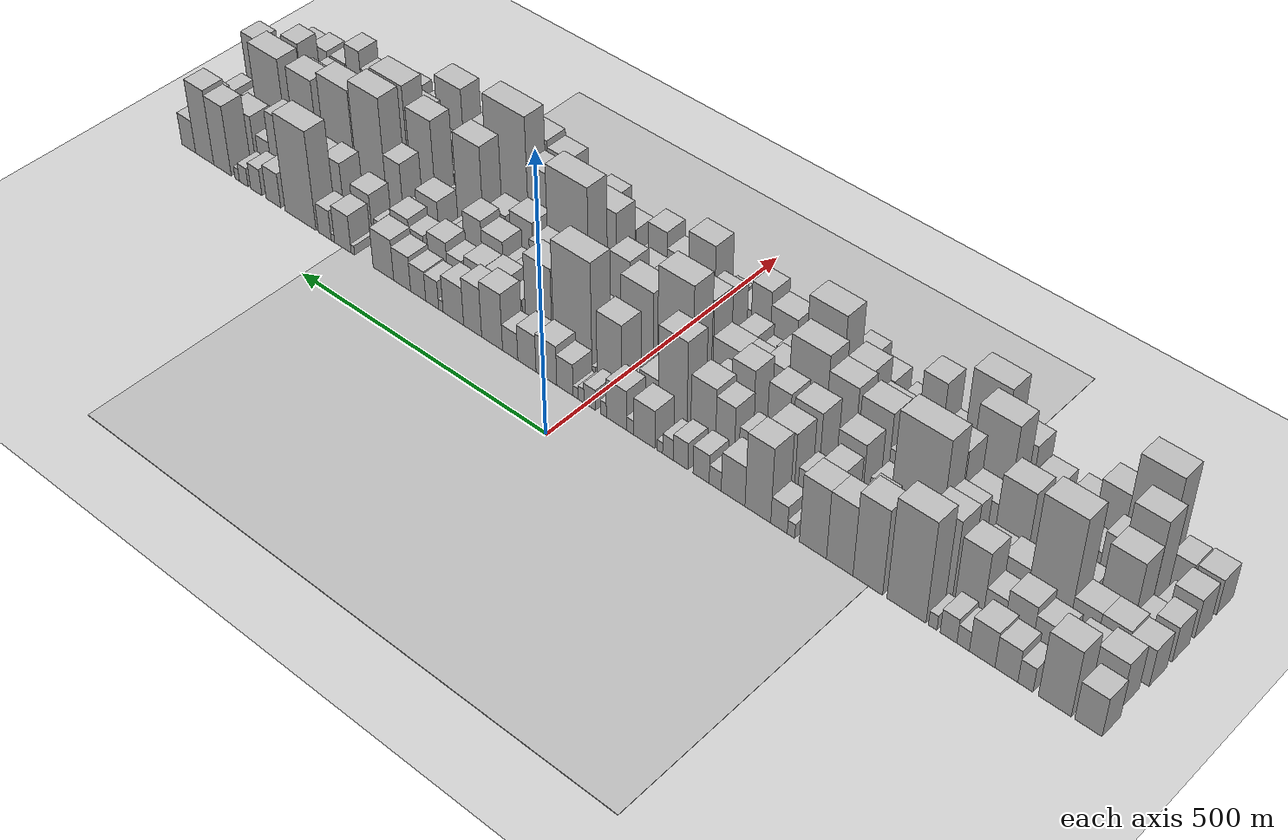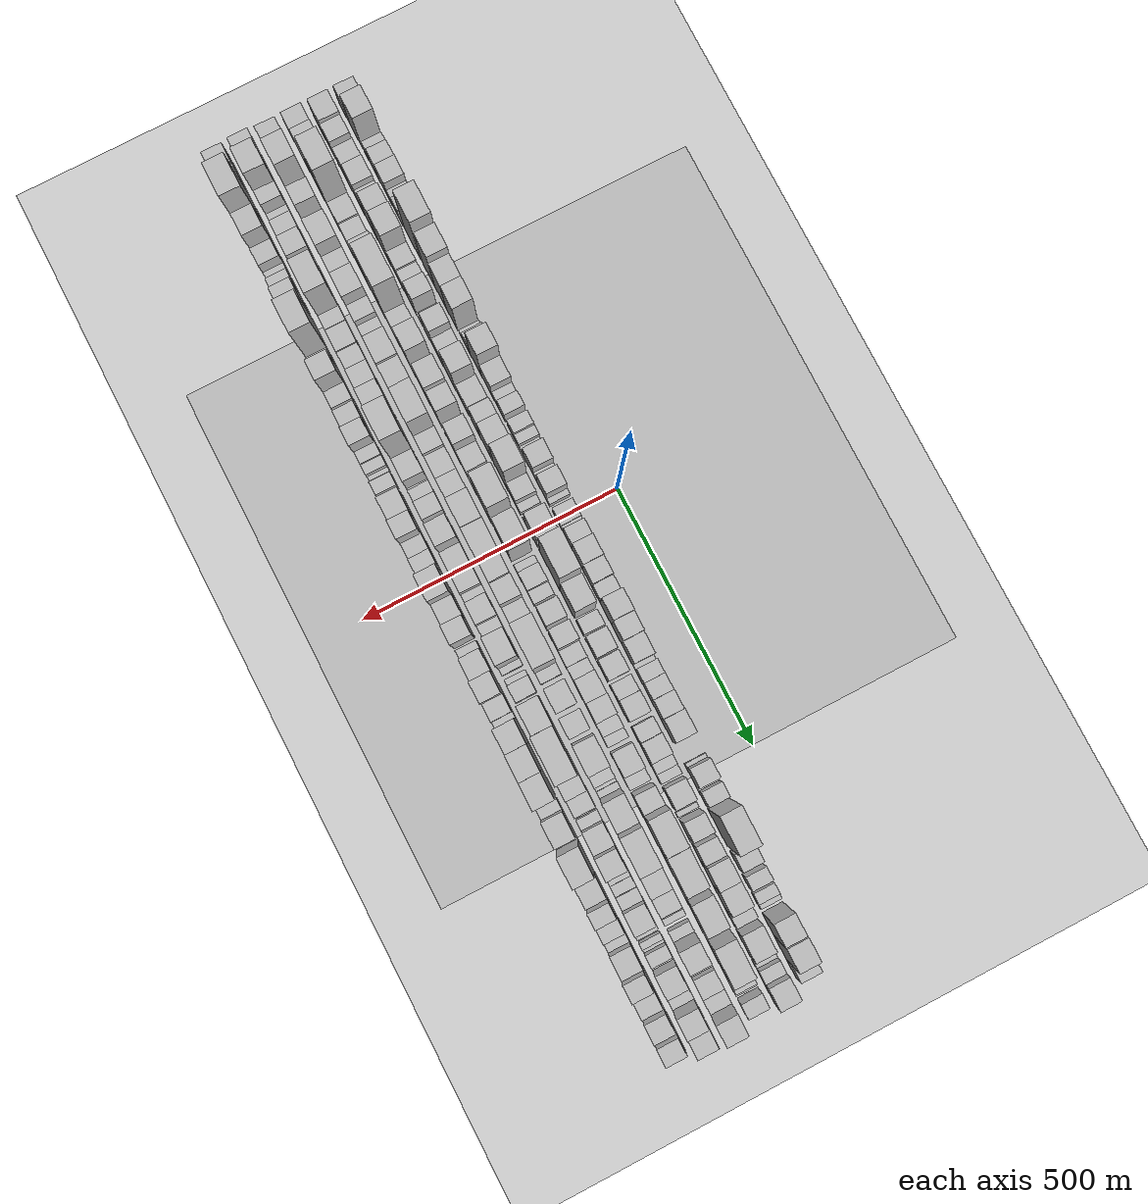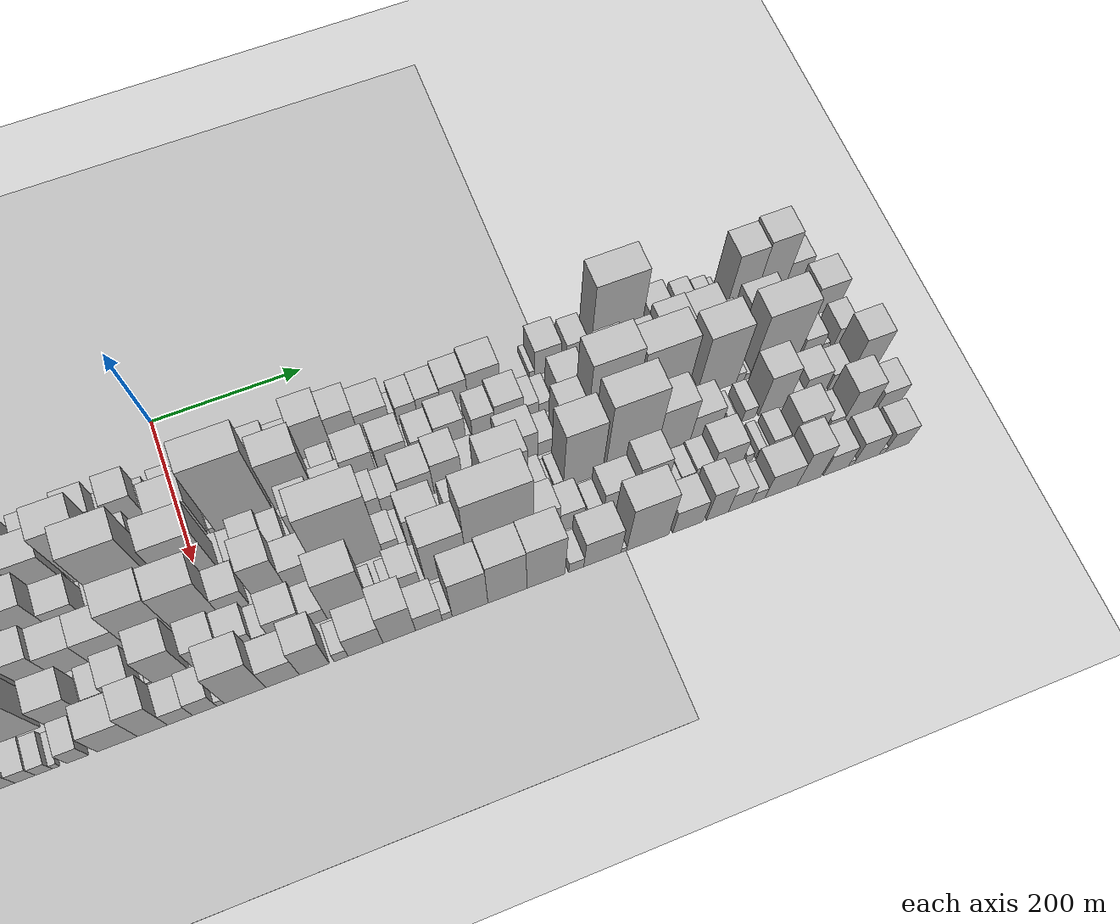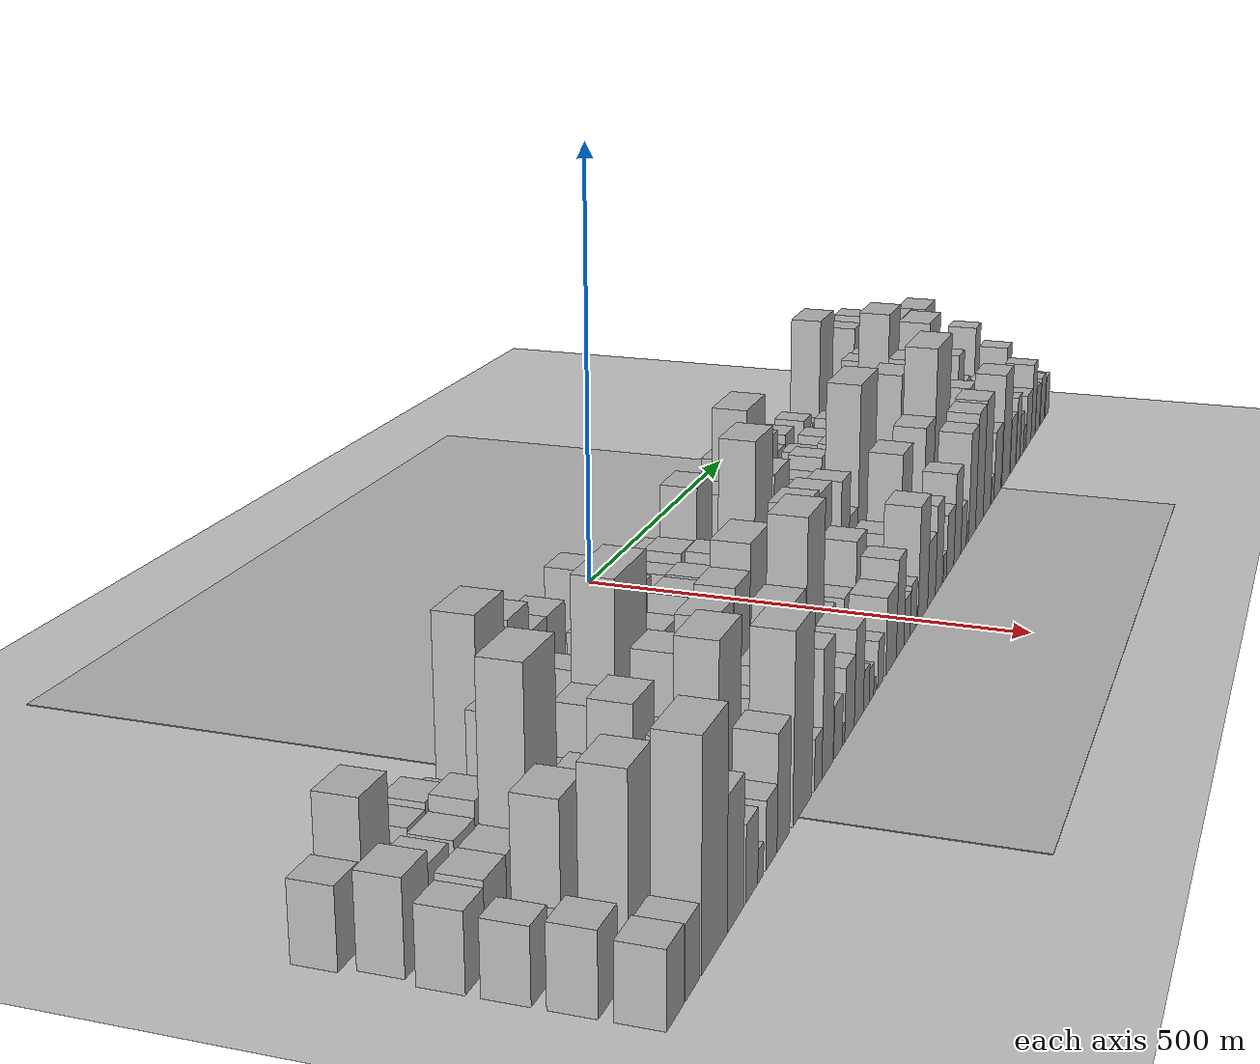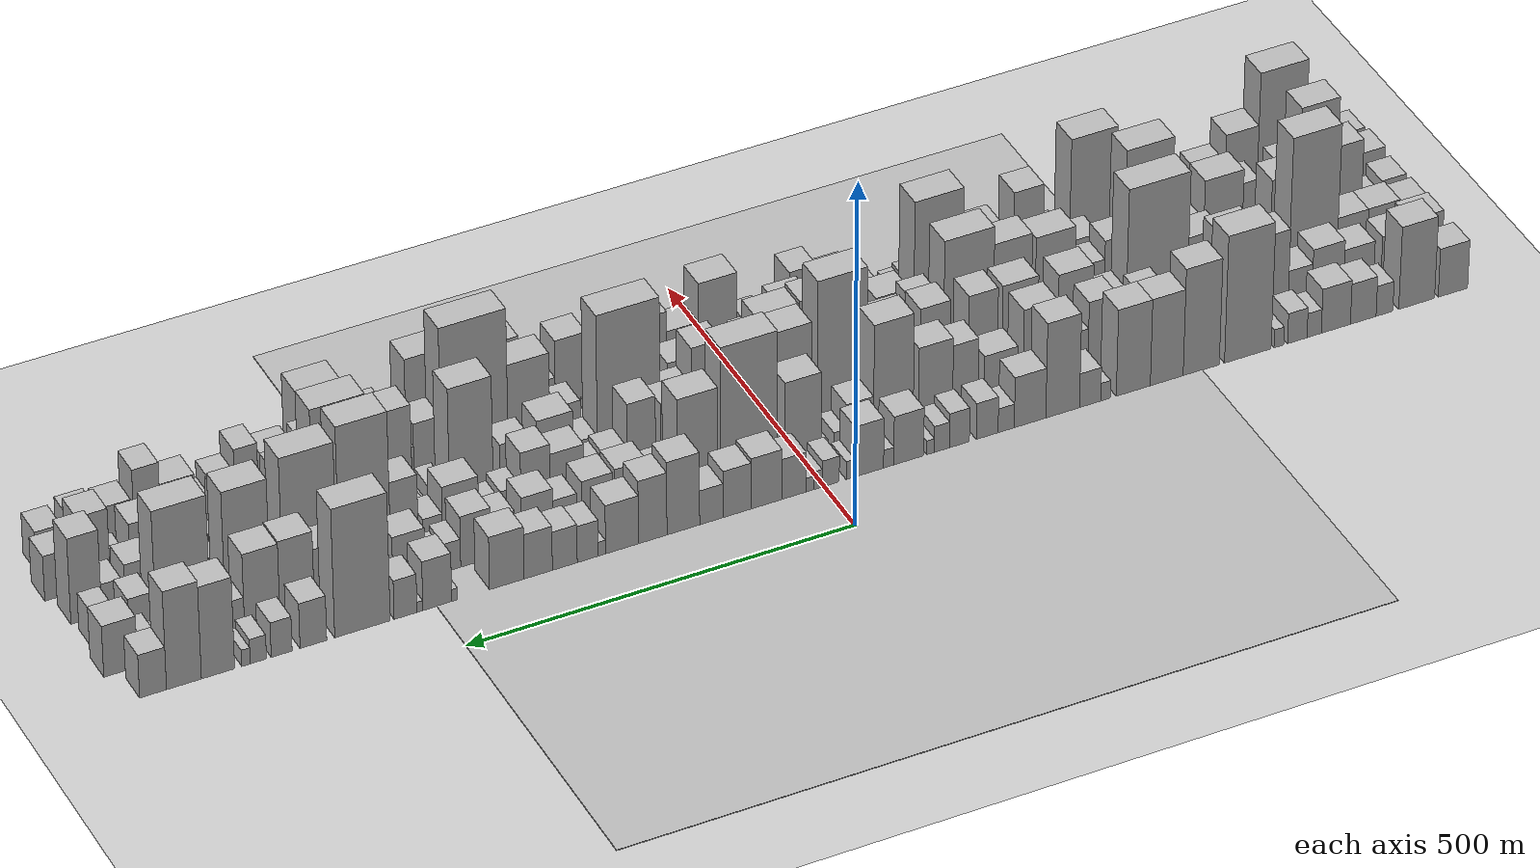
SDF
<?xml version="1.0" encoding="utf-8"?>

<sdf version="1.6">

   <world name="default">

      <gui fullscreen="0">

         <camera name="user_camera">

            <pose>-15 0 4.57585 0 0 0</pose>

            <view_controller>orbit</view_controller>

         </camera>

      </gui>

      <scene>

         <sky>

           <clouds>

             <speed>12</speed>

           </clouds>

         </sky>

         <ambient>0.4 0.4 0.4 1</ambient>

         <background>0.7 0.7 0.7 1</background>

         <shadows>1</shadows>

      </scene>

      <gravity>0 0 -9.8066</gravity>

      <magnetic_field>6e-06 2.3e-05 -4.2e-05</magnetic_field>

      <physics default="0" name="default_physics" type="ode">

         <ode>

            <solver>

               <type>quick</type>

               <iters>10</iters>

               <sor>1.0</sor>

               <use_dynamic_moi_rescaling>0</use_dynamic_moi_rescaling>

            </solver>

            <constraints>

               <cfm>0</cfm>

               <erp>0.2</erp>

               <contact_max_correcting_vel>100</contact_max_correcting_vel>

               <contact_surface_layer>0.001</contact_surface_layer>

            </constraints>

         </ode>

         <max_step_size>0.004</max_step_size>

         <real_time_factor>1</real_time_factor>

         <real_time_update_rate>250</real_time_update_rate>

      </physics>

      <light name="sun" type="directional">

         <cast_shadows>1</cast_shadows>

         <pose>0 0 10 0 0 0</pose>

         <diffuse>0.8 0.8 0.8 1</diffuse>

         <specular>0.2 0.2 0.2 1</specular>

         <attenuation>

            <range>1000</range>

            <constant>0.9</constant>

            <linear>0.01</linear>

            <quadratic>0.001</quadratic>

         </attenuation>

         <direction>-0.5 0.1 -0.9</direction>

      </light>

      <include>

         <name>ground_plane_1</name>

         <uri>model://HANNAS_ground_plane</uri>

         <pose>0 0 0  0 0 0</pose>

      </include>

      <include>

         <name>ground_plane_2</name>

         <uri>model://HANNAS_ground_plane</uri>

         <pose>100 0 0  0 0 0</pose>

      </include>

      <model name="building_1">

         <static>1</static>

         <pose frame="">100.0000 -839.8954 0 0.000000 0.000000 0.000000</pose>

         <link name="link">

            <pose frame="">0 0 36.00 0 0 0</pose>

            <collision name="collision">

               <geometry>

                  <box>

                     <size>40.0000 40.2092 72.0000</size>

                  </box>

               </geometry>

               <max_contacts>10</max_contacts>

               <surface>

                  <contact>

                     <ode/>

                  </contact>

                  <bounce/>

                  <friction>

                     <torsional>

                        <ode/>

                     </torsional>

                     <ode/>

                  </friction>

               </surface>

            </collision>

            <visual name="visual">

               <cast_shadows>0</cast_shadows>

               <geometry>

                  <box>

                     <size>40.0000 40.2092 72.0000</size>

                  </box>

               </geometry>

               <material>

                  <script>

                     <uri>model://HANNAS_wall/materials/scripts</uri>

                     <uri>model://HANNAS_wall/materials/textures</uri>

                     <name>vrc/HANNAS_wall</name>

                  </script>

               </material>

            </visual>

            <self_collide>0</self_collide>

            <enable_wind>0</enable_wind>

            <kinematic>0</kinematic>

         </link>

      </model>

      <model name="building_2">

         <static>1</static>

         <pose frame="">100.0000 -790.3096 0 0.000000 0.000000 0.000000</pose>

         <link name="link">

            <pose frame="">0 0 61.50 0 0 0</pose>

            <collision name="collision">

               <geometry>

                  <box>

                     <size>40.0000 48.9624 123.0000</size>

                  </box>

               </geometry>

               <max_contacts>10</max_contacts>

               <surface>

                  <contact>

                     <ode/>

                  </contact>

                  <bounce/>

                  <friction>

                     <torsional>

                        <ode/>

                     </torsional>

                     <ode/>

                  </friction>

               </surface>

            </collision>

            <visual name="visual">

               <cast_shadows>0</cast_shadows>

               <geometry>

                  <box>

                     <size>40.0000 48.9624 123.0000</size>

                  </box>

               </geometry>

               <material>

                  <script>

                     <uri>model://HANNAS_wall/materials/scripts</uri>

                     <uri>model://HANNAS_wall/materials/textures</uri>

                     <name>vrc/HANNAS_wall</name>

                  </script>

               </material>

            </visual>

            <self_collide>0</self_collide>

            <enable_wind>0</enable_wind>

            <kinematic>0</kinematic>

         </link>

      </model>

      <model name="building_3">

         <static>1</static>

         <pose frame="">100.0000 -746.4071 0 0.000000 0.000000 0.000000</pose>

         <link name="link">

            <pose frame="">0 0 22.50 0 0 0</pose>

            <collision name="collision">

               <geometry>

                  <box>

                     <size>40.0000 22.8427 45.0000</size>

                  </box>

               </geometry>

               <max_contacts>10</max_contacts>

               <surface>

                  <contact>

                     <ode/>

                  </contact>

                  <bounce/>

                  <friction>

                     <torsional>

                        <ode/>

                     </torsional>

                     <ode/>

                  </friction>

               </surface>

            </collision>

            <visual name="visual">

               <cast_shadows>0</cast_shadows>

               <geometry>

                  <box>

                     <size>40.0000 22.8427 45.0000</size>

                  </box>

               </geometry>

               <material>

                  <script>

                     <uri>model://HANNAS_wall/materials/scripts</uri>

                     <uri>model://HANNAS_wall/materials/textures</uri>

                     <name>vrc/HANNAS_wall</name>

                  </script>

               </material>

            </visual>

            <self_collide>0</self_collide>

            <enable_wind>0</enable_wind>

            <kinematic>0</kinematic>

         </link>

      </model>

      <model name="building_4">

         <static>1</static>

         <pose frame="">100.0000 -717.5129 0 0.000000 0.000000 0.000000</pose>

         <link name="link">

            <pose frame="">0 0 30.00 0 0 0</pose>

            <collision name="collision">

               <geometry>

                  <box>

                     <size>40.0000 34.9457 60.0000</size>

                  </box>

               </geometry>

               <max_contacts>10</max_contacts>

               <surface>

                  <contact>

                     <ode/>

                  </contact>

                  <bounce/>

                  <friction>

                     <torsional>

                        <ode/>

                     </torsional>

                     <ode/>

                  </friction>

               </surface>

            </collision>

            <visual name="visual">

               <cast_shadows>0</cast_shadows>

               <geometry>

                  <box>

                     <size>40.0000 34.9457 60.0000</size>

                  </box>

               </geometry>

               <material>

                  <script>

                     <uri>model://HANNAS_wall/materials/scripts</uri>

                     <uri>model://HANNAS_wall/materials/textures</uri>

                     <name>vrc/HANNAS_wall</name>

                  </script>

               </material>

            </visual>

            <self_collide>0</self_collide>

            <enable_wind>0</enable_wind>

            <kinematic>0</kinematic>

         </link>

      </model>

      <model name="building_5">

         <static>1</static>

         <pose frame="">100.0000 -680.2870 0 0.000000 0.000000 0.000000</pose>

         <link name="link">

            <pose frame="">0 0 33.00 0 0 0</pose>

            <collision name="collision">

               <geometry>

                  <box>

                     <size>40.0000 39.5061 66.0000</size>

                  </box>

               </geometry>

               <max_contacts>10</max_contacts>

               <surface>

                  <contact>

                     <ode/>

                  </contact>

                  <bounce/>

                  <friction>

                     <torsional>

                        <ode/>

                     </torsional>

                     <ode/>

                  </friction>

               </surface>

            </collision>

            <visual name="visual">

               <cast_shadows>0</cast_shadows>

               <geometry>

                  <box>

                     <size>40.0000 39.5061 66.0000</size>

                  </box>

               </geometry>

               <material>

                  <script>

                     <uri>model://HANNAS_wall/materials/scripts</uri>

                     <uri>model://HANNAS_wall/materials/textures</uri>

                     <name>vrc/HANNAS_wall</name>

                  </script>

               </material>

            </visual>

            <self_collide>0</self_collide>

            <enable_wind>0</enable_wind>

            <kinematic>0</kinematic>

         </link>

      </model>

      <model name="building_6">

         <static>1</static>

         <pose frame="">100.0000 -650.8760 0 0.000000 0.000000 0.000000</pose>

         <link name="link">

            <pose frame="">0 0 18.00 0 0 0</pose>

            <collision name="collision">

               <geometry>

                  <box>

                     <size>40.0000 19.3160 36.0000</size>

                  </box>

               </geometry>

               <max_contacts>10</max_contacts>

               <surface>

                  <contact>

                     <ode/>

                  </contact>

                  <bounce/>

                  <friction>

                     <torsional>

                        <ode/>

                     </torsional>

                     <ode/>

                  </friction>

               </surface>

            </collision>

            <visual name="visual">

               <cast_shadows>0</cast_shadows>

               <geometry>

                  <box>

                     <size>40.0000 19.3160 36.0000</size>

                  </box>

               </geometry>

               <material>

                  <script>

                     <uri>model://HANNAS_wall/materials/scripts</uri>

                     <uri>model://HANNAS_wall/materials/textures</uri>

                     <name>vrc/HANNAS_wall</name>

                  </script>

               </material>

            </visual>

            <self_collide>0</self_collide>

            <enable_wind>0</enable_wind>

            <kinematic>0</kinematic>

         </link>

      </model>

      <model name="building_7">

         <static>1</static>

         <pose frame="">100.0000 -628.0339 0 0.000000 0.000000 0.000000</pose>

         <link name="link">

            <pose frame="">0 0 22.50 0 0 0</pose>

            <collision name="collision">

               <geometry>

                  <box>

                     <size>40.0000 26.3681 45.0000</size>

                  </box>

               </geometry>

               <max_contacts>10</max_contacts>

               <surface>

                  <contact>

                     <ode/>

                  </contact>

                  <bounce/>

                  <friction>

                     <torsional>

                        <ode/>

                     </torsional>

                     <ode/>

                  </friction>

               </surface>

            </collision>

            <visual name="visual">

               <cast_shadows>0</cast_shadows>

               <geometry>

                  <box>

                     <size>40.0000 26.3681 45.0000</size>

                  </box>

               </geometry>

               <material>

                  <script>

                     <uri>model://HANNAS_wall/materials/scripts</uri>

                     <uri>model://HANNAS_wall/materials/textures</uri>

                     <name>vrc/HANNAS_wall</name>

                  </script>

               </material>

            </visual>

            <self_collide>0</self_collide>

            <enable_wind>0</enable_wind>

            <kinematic>0</kinematic>

         </link>

      </model>

      <model name="building_8">

         <static>1</static>

         <pose frame="">100.0000 -603.1734 0 0.000000 0.000000 0.000000</pose>

         <link name="link">

            <pose frame="">0 0 13.50 0 0 0</pose>

            <collision name="collision">

               <geometry>

                  <box>

                     <size>40.0000 13.3529 27.0000</size>

                  </box>

               </geometry>

               <max_contacts>10</max_contacts>

               <surface>

                  <contact>

                     <ode/>

                  </contact>

                  <bounce/>

                  <friction>

                     <torsional>

                        <ode/>

                     </torsional>

                     <ode/>

                  </friction>

               </surface>

            </collision>

            <visual name="visual">

               <cast_shadows>0</cast_shadows>

               <geometry>

                  <box>

                     <size>40.0000 13.3529 27.0000</size>

                  </box>

               </geometry>

               <material>

                  <script>

                     <uri>model://HANNAS_wall/materials/scripts</uri>

                     <uri>model://HANNAS_wall/materials/textures</uri>

                     <name>vrc/HANNAS_wall</name>

                  </script>

               </material>

            </visual>

            <self_collide>0</self_collide>

            <enable_wind>0</enable_wind>

            <kinematic>0</kinematic>

         </link>

      </model>

      <model name="building_9">

         <static>1</static>

         <pose frame="">100.0000 -561.1378 0 0.000000 0.000000 0.000000</pose>

         <link name="link">

            <pose frame="">0 0 94.50 0 0 0</pose>

            <collision name="collision">

               <geometry>

                  <box>

                     <size>40.0000 62.7183 189.0000</size>

                  </box>

               </geometry>

               <max_contacts>10</max_contacts>

               <surface>

                  <contact>

                     <ode/>

                  </contact>

                  <bounce/>

                  <friction>

                     <torsional>

                        <ode/>

                     </torsional>

                     <ode/>

                  </friction>

               </surface>

            </collision>

            <visual name="visual">

               <cast_shadows>0</cast_shadows>

               <geometry>

                  <box>

                     <size>40.0000 62.7183 189.0000</size>

                  </box>

               </geometry>

               <material>

                  <script>

                     <uri>model://HANNAS_wall/materials/scripts</uri>

                     <uri>model://HANNAS_wall/materials/textures</uri>

                     <name>vrc/HANNAS_wall</name>

                  </script>

               </material>

            </visual>

            <self_collide>0</self_collide>

            <enable_wind>0</enable_wind>

            <kinematic>0</kinematic>

         </link>

      </model>

      <model name="building_10">

         <static>1</static>

         <pose frame="">100.0000 -498.4930 0 0.000000 0.000000 0.000000</pose>

         <link name="link">

            <pose frame="">0 0 79.50 0 0 0</pose>

            <collision name="collision">

               <geometry>

                  <box>

                     <size>40.0000 48.5714 159.0000</size>

                  </box>

               </geometry>

               <max_contacts>10</max_contacts>

               <surface>

                  <contact>

                     <ode/>

                  </contact>

                  <bounce/>

                  <friction>

                     <torsional>

                        <ode/>

                     </torsional>

                     <ode/>

                  </friction>

               </surface>

            </collision>

            <visual name="visual">

               <cast_shadows>0</cast_shadows>

               <geometry>

                  <box>

                     <size>40.0000 48.5714 159.0000</size>

                  </box>

               </geometry>

               <material>

                  <script>

                     <uri>model://HANNAS_wall/materials/scripts</uri>

                     <uri>model://HANNAS_wall/materials/textures</uri>

                     <name>vrc/HANNAS_wall</name>

                  </script>

               </material>

            </visual>

            <self_collide>0</self_collide>

            <enable_wind>0</enable_wind>

            <kinematic>0</kinematic>

         </link>

      </model>

      <model name="building_11">

         <static>1</static>

         <pose frame="">100.0000 -452.2051 0 0.000000 0.000000 0.000000</pose>

         <link name="link">

            <pose frame="">0 0 64.50 0 0 0</pose>

            <collision name="collision">

               <geometry>

                  <box>

                     <size>40.0000 44.0044 129.0000</size>

                  </box>

               </geometry>

               <max_contacts>10</max_contacts>

               <surface>

                  <contact>

                     <ode/>

                  </contact>

                  <bounce/>

                  <friction>

                     <torsional>

                        <ode/>

                     </torsional>

                     <ode/>

                  </friction>

               </surface>

            </collision>

            <visual name="visual">

               <cast_shadows>0</cast_shadows>

               <geometry>

                  <box>

                     <size>40.0000 44.0044 129.0000</size>

                  </box>

               </geometry>

               <material>

                  <script>

                     <uri>model://HANNAS_wall/materials/scripts</uri>

                     <uri>model://HANNAS_wall/materials/textures</uri>

                     <name>vrc/HANNAS_wall</name>

                  </script>

               </material>

            </visual>

            <self_collide>0</self_collide>

            <enable_wind>0</enable_wind>

            <kinematic>0</kinematic>

         </link>

      </model>

      <model name="building_12">

         <static>1</static>

         <pose frame="">100.0000 -407.4335 0 0.000000 0.000000 0.000000</pose>

         <link name="link">

            <pose frame="">0 0 64.50 0 0 0</pose>

            <collision name="collision">

               <geometry>

                  <box>

                     <size>40.0000 45.5388 129.0000</size>

                  </box>

               </geometry>

               <max_contacts>10</max_contacts>

               <surface>

                  <contact>

                     <ode/>

                  </contact>

                  <bounce/>

                  <friction>

                     <torsional>

                        <ode/>

                     </torsional>

                     <ode/>

                  </friction>

               </surface>

            </collision>

            <visual name="visual">

               <cast_shadows>0</cast_shadows>

               <geometry>

                  <box>

                     <size>40.0000 45.5388 129.0000</size>

                  </box>

               </geometry>

               <material>

                  <script>

                     <uri>model://HANNAS_wall/materials/scripts</uri>

                     <uri>model://HANNAS_wall/materials/textures</uri>

                     <name>vrc/HANNAS_wall</name>

                  </script>

               </material>

            </visual>

            <self_collide>0</self_collide>

            <enable_wind>0</enable_wind>

            <kinematic>0</kinematic>

         </link>

      </model>

      <model name="building_13">

         <static>1</static>

         <pose frame="">100.0000 -370.3168 0 0.000000 0.000000 0.000000</pose>

         <link name="link">

            <pose frame="">0 0 13.50 0 0 0</pose>

            <collision name="collision">

               <geometry>

                  <box>

                     <size>40.0000 12.6946 27.0000</size>

                  </box>

               </geometry>

               <max_contacts>10</max_contacts>

               <surface>

                  <contact>

                     <ode/>

                  </contact>

                  <bounce/>

                  <friction>

                     <torsional>

                        <ode/>

                     </torsional>

                     <ode/>

                  </friction>

               </surface>

            </collision>

            <visual name="visual">

               <cast_shadows>0</cast_shadows>

               <geometry>

                  <box>

                     <size>40.0000 12.6946 27.0000</size>

                  </box>

               </geometry>

               <material>

                  <script>

                     <uri>model://HANNAS_wall/materials/scripts</uri>

                     <uri>model://HANNAS_wall/materials/textures</uri>

                     <name>vrc/HANNAS_wall</name>

                  </script>

               </material>

            </visual>

            <self_collide>0</self_collide>

            <enable_wind>0</enable_wind>

            <kinematic>0</kinematic>

         </link>

      </model>

      <model name="building_14">

         <static>1</static>

         <pose frame="">100.0000 -349.7692 0 0.000000 0.000000 0.000000</pose>

         <link name="link">

            <pose frame="">0 0 25.50 0 0 0</pose>

            <collision name="collision">

               <geometry>

                  <box>

                     <size>40.0000 28.4006 51.0000</size>

                  </box>

               </geometry>

               <max_contacts>10</max_contacts>

               <surface>

                  <contact>

                     <ode/>

                  </contact>

                  <bounce/>

                  <friction>

                     <torsional>

                        <ode/>

                     </torsional>

                     <ode/>

                  </friction>

               </surface>

            </collision>

            <visual name="visual">

               <cast_shadows>0</cast_shadows>

               <geometry>

                  <box>

                     <size>40.0000 28.4006 51.0000</size>

                  </box>

               </geometry>

               <material>

                  <script>

                     <uri>model://HANNAS_wall/materials/scripts</uri>

                     <uri>model://HANNAS_wall/materials/textures</uri>

                     <name>vrc/HANNAS_wall</name>

                  </script>

               </material>

            </visual>

            <self_collide>0</self_collide>

            <enable_wind>0</enable_wind>

            <kinematic>0</kinematic>

         </link>

      </model>

      <model name="building_15">

         <static>1</static>

         <pose frame="">100.0000 -313.1992 0 0.000000 0.000000 0.000000</pose>

         <link name="link">

            <pose frame="">0 0 70.50 0 0 0</pose>

            <collision name="collision">

               <geometry>

                  <box>

                     <size>40.0000 44.7393 141.0000</size>

                  </box>

               </geometry>

               <max_contacts>10</max_contacts>

               <surface>

                  <contact>

                     <ode/>

                  </contact>

                  <bounce/>

                  <friction>

                     <torsional>

                        <ode/>

                     </torsional>

                     <ode/>

                  </friction>

               </surface>

            </collision>

            <visual name="visual">

               <cast_shadows>0</cast_shadows>

               <geometry>

                  <box>

                     <size>40.0000 44.7393 141.0000</size>

                  </box>

               </geometry>

               <material>

                  <script>

                     <uri>model://HANNAS_wall/materials/scripts</uri>

                     <uri>model://HANNAS_wall/materials/textures</uri>

                     <name>vrc/HANNAS_wall</name>

                  </script>

               </material>

            </visual>

            <self_collide>0</self_collide>

            <enable_wind>0</enable_wind>

            <kinematic>0</kinematic>

         </link>

      </model>

      <model name="building_16">

         <static>1</static>

         <pose frame="">100.0000 -269.9063 0 0.000000 0.000000 0.000000</pose>

         <link name="link">

            <pose frame="">0 0 37.50 0 0 0</pose>

            <collision name="collision">

               <geometry>

                  <box>

                     <size>40.0000 41.8466 75.0000</size>

                  </box>

               </geometry>

               <max_contacts>10</max_contacts>

               <surface>

                  <contact>

                     <ode/>

                  </contact>

                  <bounce/>

                  <friction>

                     <torsional>

                        <ode/>

                     </torsional>

                     <ode/>

                  </friction>

               </surface>

            </collision>

            <visual name="visual">

               <cast_shadows>0</cast_shadows>

               <geometry>

                  <box>

                     <size>40.0000 41.8466 75.0000</size>

                  </box>

               </geometry>

               <material>

                  <script>

                     <uri>model://HANNAS_wall/materials/scripts</uri>

                     <uri>model://HANNAS_wall/materials/textures</uri>

                     <name>vrc/HANNAS_wall</name>

                  </script>

               </material>

            </visual>

            <self_collide>0</self_collide>

            <enable_wind>0</enable_wind>

            <kinematic>0</kinematic>

         </link>

      </model>

      <model name="building_17">

         <static>1</static>

         <pose frame="">100.0000 -238.2697 0 0.000000 0.000000 0.000000</pose>

         <link name="link">

            <pose frame="">0 0 18.00 0 0 0</pose>

            <collision name="collision">

               <geometry>

                  <box>

                     <size>40.0000 21.4265 36.0000</size>

                  </box>

               </geometry>

               <max_contacts>10</max_contacts>

               <surface>

                  <contact>

                     <ode/>

                  </contact>

                  <bounce/>

                  <friction>

                     <torsional>

                        <ode/>

                     </torsional>

                     <ode/>

                  </friction>

               </surface>

            </collision>

            <visual name="visual">

               <cast_shadows>0</cast_shadows>

               <geometry>

                  <box>

                     <size>40.0000 21.4265 36.0000</size>

                  </box>

               </geometry>

               <material>

                  <script>

                     <uri>model://HANNAS_wall/materials/scripts</uri>

                     <uri>model://HANNAS_wall/materials/textures</uri>

                     <name>vrc/HANNAS_wall</name>

                  </script>

               </material>

            </visual>

            <self_collide>0</self_collide>

            <enable_wind>0</enable_wind>

            <kinematic>0</kinematic>

         </link>

      </model>

      <model name="building_18">

         <static>1</static>

         <pose frame="">100.0000 -213.0907 0 0.000000 0.000000 0.000000</pose>

         <link name="link">

            <pose frame="">0 0 27.00 0 0 0</pose>

            <collision name="collision">

               <geometry>

                  <box>

                     <size>40.0000 28.9316 54.0000</size>

                  </box>

               </geometry>

               <max_contacts>10</max_contacts>

               <surface>

                  <contact>

                     <ode/>

                  </contact>

                  <bounce/>

                  <friction>

                     <torsional>

                        <ode/>

                     </torsional>

                     <ode/>

                  </friction>

               </surface>

            </collision>

            <visual name="visual">

               <cast_shadows>0</cast_shadows>

               <geometry>

                  <box>

                     <size>40.0000 28.9316 54.0000</size>

                  </box>

               </geometry>

               <material>

                  <script>

                     <uri>model://HANNAS_wall/materials/scripts</uri>

                     <uri>model://HANNAS_wall/materials/textures</uri>

                     <name>vrc/HANNAS_wall</name>

                  </script>

               </material>

            </visual>

            <self_collide>0</self_collide>

            <enable_wind>0</enable_wind>

            <kinematic>0</kinematic>

         </link>

      </model>

      <model name="building_19">

         <static>1</static>

         <pose frame="">100.0000 -176.3862 0 0.000000 0.000000 0.000000</pose>

         <link name="link">

            <pose frame="">0 0 25.50 0 0 0</pose>

            <collision name="collision">

               <geometry>

                  <box>

                     <size>40.0000 26.4775 51.0000</size>

                  </box>

               </geometry>

               <max_contacts>10</max_contacts>

               <surface>

                  <contact>

                     <ode/>

                  </contact>

                  <bounce/>

                  <friction>

                     <torsional>

                        <ode/>

                     </torsional>

                     <ode/>

                  </friction>

               </surface>

            </collision>

            <visual name="visual">

               <cast_shadows>0</cast_shadows>

               <geometry>

                  <box>

                     <size>40.0000 26.4775 51.0000</size>

                  </box>

               </geometry>

               <material>

                  <script>

                     <uri>model://HANNAS_wall/materials/scripts</uri>

                     <uri>model://HANNAS_wall/materials/textures</uri>

                     <name>vrc/HANNAS_wall</name>

                  </script>

               </material>

            </visual>

            <self_collide>0</self_collide>

            <enable_wind>0</enable_wind>

            <kinematic>0</kinematic>

         </link>

      </model>

      <model name="building_20">

         <static>1</static>

         <pose frame="">100.0000 -153.3326 0 0.000000 0.000000 0.000000</pose>

         <link name="link">

            <pose frame="">0 0 19.50 0 0 0</pose>

            <collision name="collision">

               <geometry>

                  <box>

                     <size>40.0000 19.6296 39.0000</size>

                  </box>

               </geometry>

               <max_contacts>10</max_contacts>

               <surface>

                  <contact>

                     <ode/>

                  </contact>

                  <bounce/>

                  <friction>

                     <torsional>

                        <ode/>

                     </torsional>

                     <ode/>

                  </friction>

               </surface>

            </collision>

            <visual name="visual">

               <cast_shadows>0</cast_shadows>

               <geometry>

                  <box>

                     <size>40.0000 19.6296 39.0000</size>

                  </box>

               </geometry>

               <material>

                  <script>

                     <uri>model://HANNAS_wall/materials/scripts</uri>

                     <uri>model://HANNAS_wall/materials/textures</uri>

                     <name>vrc/HANNAS_wall</name>

                  </script>

               </material>

            </visual>

            <self_collide>0</self_collide>

            <enable_wind>0</enable_wind>

            <kinematic>0</kinematic>

         </link>

      </model>

      <model name="building_21">

         <static>1</static>

         <pose frame="">100.0000 -138.4469 0 0.000000 0.000000 0.000000</pose>

         <link name="link">

            <pose frame="">0 0 10.50 0 0 0</pose>

            <collision name="collision">

               <geometry>

                  <box>

                     <size>40.0000 10.1417 21.0000</size>

                  </box>

               </geometry>

               <max_contacts>10</max_contacts>

               <surface>

                  <contact>

                     <ode/>

                  </contact>

                  <bounce/>

                  <friction>

                     <torsional>

                        <ode/>

                     </torsional>

                     <ode/>

                  </friction>

               </surface>

            </collision>

            <visual name="visual">

               <cast_shadows>0</cast_shadows>

               <geometry>

                  <box>

                     <size>40.0000 10.1417 21.0000</size>

                  </box>

               </geometry>

               <material>

                  <script>

                     <uri>model://HANNAS_wall/materials/scripts</uri>

                     <uri>model://HANNAS_wall/materials/textures</uri>

                     <name>vrc/HANNAS_wall</name>

                  </script>

               </material>

            </visual>

            <self_collide>0</self_collide>

            <enable_wind>0</enable_wind>

            <kinematic>0</kinematic>

         </link>

      </model>

      <model name="building_22">

         <static>1</static>

         <pose frame="">100.0000 -109.7502 0 0.000000 0.000000 0.000000</pose>

         <link name="link">

            <pose frame="">0 0 36.00 0 0 0</pose>

            <collision name="collision">

               <geometry>

                  <box>

                     <size>40.0000 39.2516 72.0000</size>

                  </box>

               </geometry>

               <max_contacts>10</max_contacts>

               <surface>

                  <contact>

                     <ode/>

                  </contact>

                  <bounce/>

                  <friction>

                     <torsional>

                        <ode/>

                     </torsional>

                     <ode/>

                  </friction>

               </surface>

            </collision>

            <visual name="visual">

               <cast_shadows>0</cast_shadows>

               <geometry>

                  <box>

                     <size>40.0000 39.2516 72.0000</size>

                  </box>

               </geometry>

               <material>

                  <script>

                     <uri>model://HANNAS_wall/materials/scripts</uri>

                     <uri>model://HANNAS_wall/materials/textures</uri>

                     <name>vrc/HANNAS_wall</name>

                  </script>

               </material>

            </visual>

            <self_collide>0</self_collide>

            <enable_wind>0</enable_wind>

            <kinematic>0</kinematic>

         </link>

      </model>

      <model name="building_23">

         <static>1</static>

         <pose frame="">100.0000 -83.3877 0 0.000000 0.000000 0.000000</pose>

         <link name="link">

            <pose frame="">0 0 13.50 0 0 0</pose>

            <collision name="collision">

               <geometry>

                  <box>

                     <size>40.0000 13.4734 27.0000</size>

                  </box>

               </geometry>

               <max_contacts>10</max_contacts>

               <surface>

                  <contact>

                     <ode/>

                  </contact>

                  <bounce/>

                  <friction>

                     <torsional>

                        <ode/>

                     </torsional>

                     <ode/>

                  </friction>

               </surface>

            </collision>

            <visual name="visual">

               <cast_shadows>0</cast_shadows>

               <geometry>

                  <box>

                     <size>40.0000 13.4734 27.0000</size>

                  </box>

               </geometry>

               <material>

                  <script>

                     <uri>model://HANNAS_wall/materials/scripts</uri>

                     <uri>model://HANNAS_wall/materials/textures</uri>

                     <name>vrc/HANNAS_wall</name>

                  </script>

               </material>

            </visual>

            <self_collide>0</self_collide>

            <enable_wind>0</enable_wind>

            <kinematic>0</kinematic>

         </link>

      </model>

      <model name="building_24">

         <static>1</static>

         <pose frame="">100.0000 -57.8024 0 0.000000 0.000000 0.000000</pose>

         <link name="link">

            <pose frame="">0 0 37.50 0 0 0</pose>

            <collision name="collision">

               <geometry>

                  <box>

                     <size>40.0000 37.6972 75.0000</size>

                  </box>

               </geometry>

               <max_contacts>10</max_contacts>

               <surface>

                  <contact>

                     <ode/>

                  </contact>

                  <bounce/>

                  <friction>

                     <torsional>

                        <ode/>

                     </torsional>

                     <ode/>

                  </friction>

               </surface>

            </collision>

            <visual name="visual">

               <cast_shadows>0</cast_shadows>

               <geometry>

                  <box>

                     <size>40.0000 37.6972 75.0000</size>

                  </box>

               </geometry>

               <material>

                  <script>

                     <uri>model://HANNAS_wall/materials/scripts</uri>

                     <uri>model://HANNAS_wall/materials/textures</uri>

                     <name>vrc/HANNAS_wall</name>

                  </script>

               </material>

            </visual>

            <self_collide>0</self_collide>

            <enable_wind>0</enable_wind>

            <kinematic>0</kinematic>

         </link>

      </model>

      <model name="building_25">

         <static>1</static>

         <pose frame="">100.0000 -33.2798 0 0.000000 0.000000 0.000000</pose>

         <link name="link">

            <pose frame="">0 0 13.50 0 0 0</pose>

            <collision name="collision">

               <geometry>

                  <box>

                     <size>40.0000 11.3481 27.0000</size>

                  </box>

               </geometry>

               <max_contacts>10</max_contacts>

               <surface>

                  <contact>

                     <ode/>

                  </contact>

                  <bounce/>

                  <friction>

                     <torsional>

                        <ode/>

                     </torsional>

                     <ode/>

                  </friction>

               </surface>

            </collision>

            <visual name="visual">

               <cast_shadows>0</cast_shadows>

               <geometry>

                  <box>

                     <size>40.0000 11.3481 27.0000</size>

                  </box>

               </geometry>

               <material>

                  <script>

                     <uri>model://HANNAS_wall/materials/scripts</uri>

                     <uri>model://HANNAS_wall/materials/textures</uri>

                     <name>vrc/HANNAS_wall</name>

                  </script>

               </material>

            </visual>

            <self_collide>0</self_collide>

            <enable_wind>0</enable_wind>

            <kinematic>0</kinematic>

         </link>

      </model>

      <model name="building_26">

         <static>1</static>

         <pose frame="">100.0000 -7.4630 0 0.000000 0.000000 0.000000</pose>

         <link name="link">

            <pose frame="">0 0 19.50 0 0 0</pose>

            <collision name="collision">

               <geometry>

                  <box>

                     <size>40.0000 22.2854 39.0000</size>

                  </box>

               </geometry>

               <max_contacts>10</max_contacts>

               <surface>

                  <contact>

                     <ode/>

                  </contact>

                  <bounce/>

                  <friction>

                     <torsional>

                        <ode/>

                     </torsional>

                     <ode/>

                  </friction>

               </surface>

            </collision>

            <visual name="visual">

               <cast_shadows>0</cast_shadows>

               <geometry>

                  <box>

                     <size>40.0000 22.2854 39.0000</size>

                  </box>

               </geometry>

               <material>

                  <script>

                     <uri>model://HANNAS_wall/materials/scripts</uri>

                     <uri>model://HANNAS_wall/materials/textures</uri>

                     <name>vrc/HANNAS_wall</name>

                  </script>

               </material>

            </visual>

            <self_collide>0</self_collide>

            <enable_wind>0</enable_wind>

            <kinematic>0</kinematic>

         </link>

      </model>

      <model name="building_27">

         <static>1</static>

         <pose frame="">100.0000 9.1200 0 0.000000 0.000000 0.000000</pose>

         <link name="link">

            <pose frame="">0 0 13.50 0 0 0</pose>

            <collision name="collision">

               <geometry>

                  <box>

                     <size>40.0000 10.8806 27.0000</size>

                  </box>

               </geometry>

               <max_contacts>10</max_contacts>

               <surface>

                  <contact>

                     <ode/>

                  </contact>

                  <bounce/>

                  <friction>

                     <torsional>

                        <ode/>

                     </torsional>

                     <ode/>

                  </friction>

               </surface>

            </collision>

            <visual name="visual">

               <cast_shadows>0</cast_shadows>

               <geometry>

                  <box>

                     <size>40.0000 10.8806 27.0000</size>

                  </box>

               </geometry>

               <material>

                  <script>

                     <uri>model://HANNAS_wall/materials/scripts</uri>

                     <uri>model://HANNAS_wall/materials/textures</uri>

                     <name>vrc/HANNAS_wall</name>

                  </script>

               </material>

            </visual>

            <self_collide>0</self_collide>

            <enable_wind>0</enable_wind>

            <kinematic>0</kinematic>

         </link>

      </model>

      <model name="building_28">

         <static>1</static>

         <pose frame="">100.0000 19.4953 0 0.000000 0.000000 0.000000</pose>

         <link name="link">

            <pose frame="">0 0 10.50 0 0 0</pose>

            <collision name="collision">

               <geometry>

                  <box>

                     <size>40.0000 9.8701 21.0000</size>

                  </box>

               </geometry>

               <max_contacts>10</max_contacts>

               <surface>

                  <contact>

                     <ode/>

                  </contact>

                  <bounce/>

                  <friction>

                     <torsional>

                        <ode/>

                     </torsional>

                     <ode/>

                  </friction>

               </surface>

            </collision>

            <visual name="visual">

               <cast_shadows>0</cast_shadows>

               <geometry>

                  <box>

                     <size>40.0000 9.8701 21.0000</size>

                  </box>

               </geometry>

               <material>

                  <script>

                     <uri>model://HANNAS_wall/materials/scripts</uri>

                     <uri>model://HANNAS_wall/materials/textures</uri>

                     <name>vrc/HANNAS_wall</name>

                  </script>

               </material>

            </visual>

            <self_collide>0</self_collide>

            <enable_wind>0</enable_wind>

            <kinematic>0</kinematic>

         </link>

      </model>

      <model name="building_29">

         <static>1</static>

         <pose frame="">100.0000 40.2468 0 0.000000 0.000000 0.000000</pose>

         <link name="link">

            <pose frame="">0 0 30.00 0 0 0</pose>

            <collision name="collision">

               <geometry>

                  <box>

                     <size>40.0000 31.6329 60.0000</size>

                  </box>

               </geometry>

               <max_contacts>10</max_contacts>

               <surface>

                  <contact>

                     <ode/>

                  </contact>

                  <bounce/>

                  <friction>

                     <torsional>

                        <ode/>

                     </torsional>

                     <ode/>

                  </friction>

               </surface>

            </collision>

            <visual name="visual">

               <cast_shadows>0</cast_shadows>

               <geometry>

                  <box>

                     <size>40.0000 31.6329 60.0000</size>

                  </box>

               </geometry>

               <material>

                  <script>

                     <uri>model://HANNAS_wall/materials/scripts</uri>

                     <uri>model://HANNAS_wall/materials/textures</uri>

                     <name>vrc/HANNAS_wall</name>

                  </script>

               </material>

            </visual>

            <self_collide>0</self_collide>

            <enable_wind>0</enable_wind>

            <kinematic>0</kinematic>

         </link>

      </model>

      <model name="building_30">

         <static>1</static>

         <pose frame="">100.0000 76.3319 0 0.000000 0.000000 0.000000</pose>

         <link name="link">

            <pose frame="">0 0 37.50 0 0 0</pose>

            <collision name="collision">

               <geometry>

                  <box>

                     <size>40.0000 40.5372 75.0000</size>

                  </box>

               </geometry>

               <max_contacts>10</max_contacts>

               <surface>

                  <contact>

                     <ode/>

                  </contact>

                  <bounce/>

                  <friction>

                     <torsional>

                        <ode/>

                     </torsional>

                     <ode/>

                  </friction>

               </surface>

            </collision>

            <visual name="visual">

               <cast_shadows>0</cast_shadows>

               <geometry>

                  <box>

                     <size>40.0000 40.5372 75.0000</size>

                  </box>

               </geometry>

               <material>

                  <script>

                     <uri>model://HANNAS_wall/materials/scripts</uri>

                     <uri>model://HANNAS_wall/materials/textures</uri>

                     <name>vrc/HANNAS_wall</name>

                  </script>

               </material>

            </visual>

            <self_collide>0</self_collide>

            <enable_wind>0</enable_wind>

            <kinematic>0</kinematic>

         </link>

      </model>

      <model name="building_31">

         <static>1</static>

         <pose frame="">100.0000 114.6214 0 0.000000 0.000000 0.000000</pose>

         <link name="link">

            <pose frame="">0 0 34.50 0 0 0</pose>

            <collision name="collision">

               <geometry>

                  <box>

                     <size>40.0000 36.0418 69.0000</size>

                  </box>

               </geometry>

               <max_contacts>10</max_contacts>

               <surface>

                  <contact>

                     <ode/>

                  </contact>

                  <bounce/>

                  <friction>

                     <torsional>

                        <ode/>

                     </torsional>

                     <ode/>

                  </friction>

               </surface>

            </collision>

            <visual name="visual">

               <cast_shadows>0</cast_shadows>

               <geometry>

                  <box>

                     <size>40.0000 36.0418 69.0000</size>

                  </box>

               </geometry>

               <material>

                  <script>

                     <uri>model://HANNAS_wall/materials/scripts</uri>

                     <uri>model://HANNAS_wall/materials/textures</uri>

                     <name>vrc/HANNAS_wall</name>

                  </script>

               </material>

            </visual>

            <self_collide>0</self_collide>

            <enable_wind>0</enable_wind>

            <kinematic>0</kinematic>

         </link>

      </model>

      <model name="building_32">

         <static>1</static>

         <pose frame="">100.0000 147.8594 0 0.000000 0.000000 0.000000</pose>

         <link name="link">

            <pose frame="">0 0 25.50 0 0 0</pose>

            <collision name="collision">

               <geometry>

                  <box>

                     <size>40.0000 30.4344 51.0000</size>

                  </box>

               </geometry>

               <max_contacts>10</max_contacts>

               <surface>

                  <contact>

                     <ode/>

                  </contact>

                  <bounce/>

                  <friction>

                     <torsional>

                        <ode/>

                     </torsional>

                     <ode/>

                  </friction>

               </surface>

            </collision>

            <visual name="visual">

               <cast_shadows>0</cast_shadows>

               <geometry>

                  <box>

                     <size>40.0000 30.4344 51.0000</size>

                  </box>

               </geometry>

               <material>

                  <script>

                     <uri>model://HANNAS_wall/materials/scripts</uri>

                     <uri>model://HANNAS_wall/materials/textures</uri>

                     <name>vrc/HANNAS_wall</name>

                  </script>

               </material>

            </visual>

            <self_collide>0</self_collide>

            <enable_wind>0</enable_wind>

            <kinematic>0</kinematic>

         </link>

      </model>

      <model name="building_33">

         <static>1</static>

         <pose frame="">100.0000 184.2097 0 0.000000 0.000000 0.000000</pose>

         <link name="link">

            <pose frame="">0 0 54.00 0 0 0</pose>

            <collision name="collision">

               <geometry>

                  <box>

                     <size>40.0000 42.2661 108.0000</size>

                  </box>

               </geometry>

               <max_contacts>10</max_contacts>

               <surface>

                  <contact>

                     <ode/>

                  </contact>

                  <bounce/>

                  <friction>

                     <torsional>

                        <ode/>

                     </torsional>

                     <ode/>

                  </friction>

               </surface>

            </collision>

            <visual name="visual">

               <cast_shadows>0</cast_shadows>

               <geometry>

                  <box>

                     <size>40.0000 42.2661 108.0000</size>

                  </box>

               </geometry>

               <material>

                  <script>

                     <uri>model://HANNAS_wall/materials/scripts</uri>

                     <uri>model://HANNAS_wall/materials/textures</uri>

                     <name>vrc/HANNAS_wall</name>

                  </script>

               </material>

            </visual>

            <self_collide>0</self_collide>

            <enable_wind>0</enable_wind>

            <kinematic>0</kinematic>

         </link>

      </model>

      <model name="building_34">

         <static>1</static>

         <pose frame="">100.0000 223.7622 0 0.000000 0.000000 0.000000</pose>

         <link name="link">

            <pose frame="">0 0 46.50 0 0 0</pose>

            <collision name="collision">

               <geometry>

                  <box>

                     <size>40.0000 36.8390 93.0000</size>

                  </box>

               </geometry>

               <max_contacts>10</max_contacts>

               <surface>

                  <contact>

                     <ode/>

                  </contact>

                  <bounce/>

                  <friction>

                     <torsional>

                        <ode/>

                     </torsional>

                     <ode/>

                  </friction>

               </surface>

            </collision>

            <visual name="visual">

               <cast_shadows>0</cast_shadows>

               <geometry>

                  <box>

                     <size>40.0000 36.8390 93.0000</size>

                  </box>

               </geometry>

               <material>

                  <script>

                     <uri>model://HANNAS_wall/materials/scripts</uri>

                     <uri>model://HANNAS_wall/materials/textures</uri>

                     <name>vrc/HANNAS_wall</name>

                  </script>

               </material>

            </visual>

            <self_collide>0</self_collide>

            <enable_wind>0</enable_wind>

            <kinematic>0</kinematic>

         </link>

      </model>

      <model name="building_35">

         <static>1</static>

         <pose frame="">100.0000 263.3432 0 0.000000 0.000000 0.000000</pose>

         <link name="link">

            <pose frame="">0 0 36.00 0 0 0</pose>

            <collision name="collision">

               <geometry>

                  <box>

                     <size>40.0000 42.3230 72.0000</size>

                  </box>

               </geometry>

               <max_contacts>10</max_contacts>

               <surface>

                  <contact>

                     <ode/>

                  </contact>

                  <bounce/>

                  <friction>

                     <torsional>

                        <ode/>

                     </torsional>

                     <ode/>

                  </friction>

               </surface>

            </collision>

            <visual name="visual">

               <cast_shadows>0</cast_shadows>

               <geometry>

                  <box>

                     <size>40.0000 42.3230 72.0000</size>

                  </box>

               </geometry>

               <material>

                  <script>

                     <uri>model://HANNAS_wall/materials/scripts</uri>

                     <uri>model://HANNAS_wall/materials/textures</uri>

                     <name>vrc/HANNAS_wall</name>

                  </script>

               </material>

            </visual>

            <self_collide>0</self_collide>

            <enable_wind>0</enable_wind>

            <kinematic>0</kinematic>

         </link>

      </model>

      <model name="building_36">

         <static>1</static>

         <pose frame="">100.0000 289.1036 0 0.000000 0.000000 0.000000</pose>

         <link name="link">

            <pose frame="">0 0 10.50 0 0 0</pose>

            <collision name="collision">

               <geometry>

                  <box>

                     <size>40.0000 9.1977 21.0000</size>

                  </box>

               </geometry>

               <max_contacts>10</max_contacts>

               <surface>

                  <contact>

                     <ode/>

                  </contact>

                  <bounce/>

                  <friction>

                     <torsional>

                        <ode/>

                     </torsional>

                     <ode/>

                  </friction>

               </surface>

            </collision>

            <visual name="visual">

               <cast_shadows>0</cast_shadows>

               <geometry>

                  <box>

                     <size>40.0000 9.1977 21.0000</size>

                  </box>

               </geometry>

               <material>

                  <script>

                     <uri>model://HANNAS_wall/materials/scripts</uri>

                     <uri>model://HANNAS_wall/materials/textures</uri>

                     <name>vrc/HANNAS_wall</name>

                  </script>

               </material>

            </visual>

            <self_collide>0</self_collide>

            <enable_wind>0</enable_wind>

            <kinematic>0</kinematic>

         </link>

      </model>

      <model name="building_37">

         <static>1</static>

         <pose frame="">100.0000 307.2518 0 0.000000 0.000000 0.000000</pose>

         <link name="link">

            <pose frame="">0 0 27.00 0 0 0</pose>

            <collision name="collision">

               <geometry>

                  <box>

                     <size>40.0000 27.0988 54.0000</size>

                  </box>

               </geometry>

               <max_contacts>10</max_contacts>

               <surface>

                  <contact>

                     <ode/>

                  </contact>

                  <bounce/>

                  <friction>

                     <torsional>

                        <ode/>

                     </torsional>

                     <ode/>

                  </friction>

               </surface>

            </collision>

            <visual name="visual">

               <cast_shadows>0</cast_shadows>

               <geometry>

                  <box>

                     <size>40.0000 27.0988 54.0000</size>

                  </box>

               </geometry>

               <material>

                  <script>

                     <uri>model://HANNAS_wall/materials/scripts</uri>

                     <uri>model://HANNAS_wall/materials/textures</uri>

                     <name>vrc/HANNAS_wall</name>

                  </script>

               </material>

            </visual>

            <self_collide>0</self_collide>

            <enable_wind>0</enable_wind>

            <kinematic>0</kinematic>

         </link>

      </model>

      <model name="building_38">

         <static>1</static>

         <pose frame="">100.0000 336.7507 0 0.000000 0.000000 0.000000</pose>

         <link name="link">

            <pose frame="">0 0 28.50 0 0 0</pose>

            <collision name="collision">

               <geometry>

                  <box>

                     <size>40.0000 31.8990 57.0000</size>

                  </box>

               </geometry>

               <max_contacts>10</max_contacts>

               <surface>

                  <contact>

                     <ode/>

                  </contact>

                  <bounce/>

                  <friction>

                     <torsional>

                        <ode/>

                     </torsional>

                     <ode/>

                  </friction>

               </surface>

            </collision>

            <visual name="visual">

               <cast_shadows>0</cast_shadows>

               <geometry>

                  <box>

                     <size>40.0000 31.8990 57.0000</size>

                  </box>

               </geometry>

               <material>

                  <script>

                     <uri>model://HANNAS_wall/materials/scripts</uri>

                     <uri>model://HANNAS_wall/materials/textures</uri>

                     <name>vrc/HANNAS_wall</name>

                  </script>

               </material>

            </visual>

            <self_collide>0</self_collide>

            <enable_wind>0</enable_wind>

            <kinematic>0</kinematic>

         </link>

      </model>

      <model name="building_39">

         <static>1</static>

         <pose frame="">100.0000 370.7542 0 0.000000 0.000000 0.000000</pose>

         <link name="link">

            <pose frame="">0 0 33.00 0 0 0</pose>

            <collision name="collision">

               <geometry>

                  <box>

                     <size>40.0000 36.1079 66.0000</size>

                  </box>

               </geometry>

               <max_contacts>10</max_contacts>

               <surface>

                  <contact>

                     <ode/>

                  </contact>

                  <bounce/>

                  <friction>

                     <torsional>

                        <ode/>

                     </torsional>

                     <ode/>

                  </friction>

               </surface>

            </collision>

            <visual name="visual">

               <cast_shadows>0</cast_shadows>

               <geometry>

                  <box>

                     <size>40.0000 36.1079 66.0000</size>

                  </box>

               </geometry>

               <material>

                  <script>

                     <uri>model://HANNAS_wall/materials/scripts</uri>

                     <uri>model://HANNAS_wall/materials/textures</uri>

                     <name>vrc/HANNAS_wall</name>

                  </script>

               </material>

            </visual>

            <self_collide>0</self_collide>

            <enable_wind>0</enable_wind>

            <kinematic>0</kinematic>

         </link>

      </model>

      <model name="building_40">

         <static>1</static>

         <pose frame="">100.0000 410.9158 0 0.000000 0.000000 0.000000</pose>

         <link name="link">

            <pose frame="">0 0 39.00 0 0 0</pose>

            <collision name="collision">

               <geometry>

                  <box>

                     <size>40.0000 44.2153 78.0000</size>

                  </box>

               </geometry>

               <max_contacts>10</max_contacts>

               <surface>

                  <contact>

                     <ode/>

                  </contact>

                  <bounce/>

                  <friction>

                     <torsional>

                        <ode/>

                     </torsional>

                     <ode/>

                  </friction>

               </surface>

            </collision>

            <visual name="visual">

               <cast_shadows>0</cast_shadows>

               <geometry>

                  <box>

                     <size>40.0000 44.2153 78.0000</size>

                  </box>

               </geometry>

               <material>

                  <script>

                     <uri>model://HANNAS_wall/materials/scripts</uri>

                     <uri>model://HANNAS_wall/materials/textures</uri>

                     <name>vrc/HANNAS_wall</name>

                  </script>

               </material>

            </visual>

            <self_collide>0</self_collide>

            <enable_wind>0</enable_wind>

            <kinematic>0</kinematic>

         </link>

      </model>

      <model name="building_41">

         <static>1</static>

         <pose frame="">100.0000 477.3206 0 0.000000 0.000000 0.000000</pose>

         <link name="link">

            <pose frame="">0 0 9.00 0 0 0</pose>

            <collision name="collision">

               <geometry>

                  <box>

                     <size>40.0000 7.5315 18.0000</size>

                  </box>

               </geometry>

               <max_contacts>10</max_contacts>

               <surface>

                  <contact>

                     <ode/>

                  </contact>

                  <bounce/>

                  <friction>

                     <torsional>

                        <ode/>

                     </torsional>

                     <ode/>

                  </friction>

               </surface>

            </collision>

            <visual name="visual">

               <cast_shadows>0</cast_shadows>

               <geometry>

                  <box>

                     <size>40.0000 7.5315 18.0000</size>

                  </box>

               </geometry>

               <material>

                  <script>

                     <uri>model://HANNAS_wall/materials/scripts</uri>

                     <uri>model://HANNAS_wall/materials/textures</uri>

                     <name>vrc/HANNAS_wall</name>

                  </script>

               </material>

            </visual>

            <self_collide>0</self_collide>

            <enable_wind>0</enable_wind>

            <kinematic>0</kinematic>

         </link>

      </model>

      <model name="building_42">

         <static>1</static>

         <pose frame="">100.0000 499.4202 0 0.000000 0.000000 0.000000</pose>

         <link name="link">

            <pose frame="">0 0 36.00 0 0 0</pose>

            <collision name="collision">

               <geometry>

                  <box>

                     <size>40.0000 36.6676 72.0000</size>

                  </box>

               </geometry>

               <max_contacts>10</max_contacts>

               <surface>

                  <contact>

                     <ode/>

                  </contact>

                  <bounce/>

                  <friction>

                     <torsional>

                        <ode/>

                     </torsional>

                     <ode/>

                  </friction>

               </surface>

            </collision>

            <visual name="visual">

               <cast_shadows>0</cast_shadows>

               <geometry>

                  <box>

                     <size>40.0000 36.6676 72.0000</size>

                  </box>

               </geometry>

               <material>

                  <script>

                     <uri>model://HANNAS_wall/materials/scripts</uri>

                     <uri>model://HANNAS_wall/materials/textures</uri>

                     <name>vrc/HANNAS_wall</name>

                  </script>

               </material>

            </visual>

            <self_collide>0</self_collide>

            <enable_wind>0</enable_wind>

            <kinematic>0</kinematic>

         </link>

      </model>

      <model name="building_43">

         <static>1</static>

         <pose frame="">100.0000 521.4885 0 0.000000 0.000000 0.000000</pose>

         <link name="link">

            <pose frame="">0 0 7.50 0 0 0</pose>

            <collision name="collision">

               <geometry>

                  <box>

                     <size>40.0000 7.4690 15.0000</size>

                  </box>

               </geometry>

               <max_contacts>10</max_contacts>

               <surface>

                  <contact>

                     <ode/>

                  </contact>

                  <bounce/>

                  <friction>

                     <torsional>

                        <ode/>

                     </torsional>

                     <ode/>

                  </friction>

               </surface>

            </collision>

            <visual name="visual">

               <cast_shadows>0</cast_shadows>

               <geometry>

                  <box>

                     <size>40.0000 7.4690 15.0000</size>

                  </box>

               </geometry>

               <material>

                  <script>

                     <uri>model://HANNAS_wall/materials/scripts</uri>

                     <uri>model://HANNAS_wall/materials/textures</uri>

                     <name>vrc/HANNAS_wall</name>

                  </script>

               </material>

            </visual>

            <self_collide>0</self_collide>

            <enable_wind>0</enable_wind>

            <kinematic>0</kinematic>

         </link>

      </model>

      <model name="building_44">

         <static>1</static>

         <pose frame="">100.0000 539.7193 0 0.000000 0.000000 0.000000</pose>

         <link name="link">

            <pose frame="">0 0 28.50 0 0 0</pose>

            <collision name="collision">

               <geometry>

                  <box>

                     <size>40.0000 28.9928 57.0000</size>

                  </box>

               </geometry>

               <max_contacts>10</max_contacts>

               <surface>

                  <contact>

                     <ode/>

                  </contact>

                  <bounce/>

                  <friction>

                     <torsional>

                        <ode/>

                     </torsional>

                     <ode/>

                  </friction>

               </surface>

            </collision>

            <visual name="visual">

               <cast_shadows>0</cast_shadows>

               <geometry>

                  <box>

                     <size>40.0000 28.9928 57.0000</size>

                  </box>

               </geometry>

               <material>

                  <script>

                     <uri>model://HANNAS_wall/materials/scripts</uri>

                     <uri>model://HANNAS_wall/materials/textures</uri>

                     <name>vrc/HANNAS_wall</name>

                  </script>

               </material>

            </visual>

            <self_collide>0</self_collide>

            <enable_wind>0</enable_wind>

            <kinematic>0</kinematic>

         </link>

      </model>

      <model name="building_45">

         <static>1</static>

         <pose frame="">100.0000 594.2579 0 0.000000 0.000000 0.000000</pose>

         <link name="link">

            <pose frame="">0 0 94.50 0 0 0</pose>

            <collision name="collision">

               <geometry>

                  <box>

                     <size>40.0000 70.0843 189.0000</size>

                  </box>

               </geometry>

               <max_contacts>10</max_contacts>

               <surface>

                  <contact>

                     <ode/>

                  </contact>

                  <bounce/>

                  <friction>

                     <torsional>

                        <ode/>

                     </torsional>

                     <ode/>

                  </friction>

               </surface>

            </collision>

            <visual name="visual">

               <cast_shadows>0</cast_shadows>

               <geometry>

                  <box>

                     <size>40.0000 70.0843 189.0000</size>

                  </box>

               </geometry>

               <material>

                  <script>

                     <uri>model://HANNAS_wall/materials/scripts</uri>

                     <uri>model://HANNAS_wall/materials/textures</uri>

                     <name>vrc/HANNAS_wall</name>

                  </script>

               </material>

            </visual>

            <self_collide>0</self_collide>

            <enable_wind>0</enable_wind>

            <kinematic>0</kinematic>

         </link>

      </model>

      <model name="building_46">

         <static>1</static>

         <pose frame="">100.0000 656.0975 0 0.000000 0.000000 0.000000</pose>

         <link name="link">

            <pose frame="">0 0 33.00 0 0 0</pose>

            <collision name="collision">

               <geometry>

                  <box>

                     <size>40.0000 33.5948 66.0000</size>

                  </box>

               </geometry>

               <max_contacts>10</max_contacts>

               <surface>

                  <contact>

                     <ode/>

                  </contact>

                  <bounce/>

                  <friction>

                     <torsional>

                        <ode/>

                     </torsional>

                     <ode/>

                  </friction>

               </surface>

            </collision>

            <visual name="visual">

               <cast_shadows>0</cast_shadows>

               <geometry>

                  <box>

                     <size>40.0000 33.5948 66.0000</size>

                  </box>

               </geometry>

               <material>

                  <script>

                     <uri>model://HANNAS_wall/materials/scripts</uri>

                     <uri>model://HANNAS_wall/materials/textures</uri>

                     <name>vrc/HANNAS_wall</name>

                  </script>

               </material>

            </visual>

            <self_collide>0</self_collide>

            <enable_wind>0</enable_wind>

            <kinematic>0</kinematic>

         </link>

      </model>

      <model name="building_47">

         <static>1</static>

         <pose frame="">100.0000 696.0062 0 0.000000 0.000000 0.000000</pose>

         <link name="link">

            <pose frame="">0 0 25.50 0 0 0</pose>

            <collision name="collision">

               <geometry>

                  <box>

                     <size>40.0000 26.2226 51.0000</size>

                  </box>

               </geometry>

               <max_contacts>10</max_contacts>

               <surface>

                  <contact>

                     <ode/>

                  </contact>

                  <bounce/>

                  <friction>

                     <torsional>

                        <ode/>

                     </torsional>

                     <ode/>

                  </friction>

               </surface>

            </collision>

            <visual name="visual">

               <cast_shadows>0</cast_shadows>

               <geometry>

                  <box>

                     <size>40.0000 26.2226 51.0000</size>

                  </box>

               </geometry>

               <material>

                  <script>

                     <uri>model://HANNAS_wall/materials/scripts</uri>

                     <uri>model://HANNAS_wall/materials/textures</uri>

                     <name>vrc/HANNAS_wall</name>

                  </script>

               </material>

            </visual>

            <self_collide>0</self_collide>

            <enable_wind>0</enable_wind>

            <kinematic>0</kinematic>

         </link>

      </model>

      <model name="building_48">

         <static>1</static>

         <pose frame="">100.0000 725.3046 0 0.000000 0.000000 0.000000</pose>

         <link name="link">

            <pose frame="">0 0 18.00 0 0 0</pose>

            <collision name="collision">

               <geometry>

                  <box>

                     <size>40.0000 20.3742 36.0000</size>

                  </box>

               </geometry>

               <max_contacts>10</max_contacts>

               <surface>

                  <contact>

                     <ode/>

                  </contact>

                  <bounce/>

                  <friction>

                     <torsional>

                        <ode/>

                     </torsional>

                     <ode/>

                  </friction>

               </surface>

            </collision>

            <visual name="visual">

               <cast_shadows>0</cast_shadows>

               <geometry>

                  <box>

                     <size>40.0000 20.3742 36.0000</size>

                  </box>

               </geometry>

               <material>

                  <script>

                     <uri>model://HANNAS_wall/materials/scripts</uri>

                     <uri>model://HANNAS_wall/materials/textures</uri>

                     <name>vrc/HANNAS_wall</name>

                  </script>

               </material>

            </visual>

            <self_collide>0</self_collide>

            <enable_wind>0</enable_wind>

            <kinematic>0</kinematic>

         </link>

      </model>

      <model name="building_49">

         <static>1</static>

         <pose frame="">100.0000 740.6938 0 0.000000 0.000000 0.000000</pose>

         <link name="link">

            <pose frame="">0 0 12.00 0 0 0</pose>

            <collision name="collision">

               <geometry>

                  <box>

                     <size>40.0000 10.4042 24.0000</size>

                  </box>

               </geometry>

               <max_contacts>10</max_contacts>

               <surface>

                  <contact>

                     <ode/>

                  </contact>

                  <bounce/>

                  <friction>

                     <torsional>

                        <ode/>

                     </torsional>

                     <ode/>

                  </friction>

               </surface>

            </collision>

            <visual name="visual">

               <cast_shadows>0</cast_shadows>

               <geometry>

                  <box>

                     <size>40.0000 10.4042 24.0000</size>

                  </box>

               </geometry>

               <material>

                  <script>

                     <uri>model://HANNAS_wall/materials/scripts</uri>

                     <uri>model://HANNAS_wall/materials/textures</uri>

                     <name>vrc/HANNAS_wall</name>

                  </script>

               </material>

            </visual>

            <self_collide>0</self_collide>

            <enable_wind>0</enable_wind>

            <kinematic>0</kinematic>

         </link>

      </model>

      <model name="building_50">

         <static>1</static>

         <pose frame="">100.0000 775.6870 0 0.000000 0.000000 0.000000</pose>

         <link name="link">

            <pose frame="">0 0 67.50 0 0 0</pose>

            <collision name="collision">

               <geometry>

                  <box>

                     <size>40.0000 41.5821 135.0000</size>

                  </box>

               </geometry>

               <max_contacts>10</max_contacts>

               <surface>

                  <contact>

                     <ode/>

                  </contact>

                  <bounce/>

                  <friction>

                     <torsional>

                        <ode/>

                     </torsional>

                     <ode/>

                  </friction>

               </surface>

            </collision>

            <visual name="visual">

               <cast_shadows>0</cast_shadows>

               <geometry>

                  <box>

                     <size>40.0000 41.5821 135.0000</size>

                  </box>

               </geometry>

               <material>

                  <script>

                     <uri>model://HANNAS_wall/materials/scripts</uri>

                     <uri>model://HANNAS_wall/materials/textures</uri>

                     <name>vrc/HANNAS_wall</name>

                  </script>

               </material>

            </visual>

            <self_collide>0</self_collide>

            <enable_wind>0</enable_wind>

            <kinematic>0</kinematic>

         </link>

      </model>

      <model name="building_51">

         <static>1</static>

         <pose frame="">100.0000 818.2187 0 0.000000 0.000000 0.000000</pose>

         <link name="link">

            <pose frame="">0 0 72.00 0 0 0</pose>

            <collision name="collision">

               <geometry>

                  <box>

                     <size>40.0000 43.4814 144.0000</size>

                  </box>

               </geometry>

               <max_contacts>10</max_contacts>

               <surface>

                  <contact>

                     <ode/>

                  </contact>

                  <bounce/>

                  <friction>

                     <torsional>

                        <ode/>

                     </torsional>

                     <ode/>

                  </friction>

               </surface>

            </collision>

            <visual name="visual">

               <cast_shadows>0</cast_shadows>

               <geometry>

                  <box>

                     <size>40.0000 43.4814 144.0000</size>

                  </box>

               </geometry>

               <material>

                  <script>

                     <uri>model://HANNAS_wall/materials/scripts</uri>

                     <uri>model://HANNAS_wall/materials/textures</uri>

                     <name>vrc/HANNAS_wall</name>

                  </script>

               </material>

            </visual>

            <self_collide>0</self_collide>

            <enable_wind>0</enable_wind>

            <kinematic>0</kinematic>

         </link>

      </model>

      <model name="building_52">

         <static>1</static>

         <pose frame="">100.0000 856.7007 0 0.000000 0.000000 0.000000</pose>

         <link name="link">

            <pose frame="">0 0 31.50 0 0 0</pose>

            <collision name="collision">

               <geometry>

                  <box>

                     <size>40.0000 33.4826 63.0000</size>

                  </box>

               </geometry>

               <max_contacts>10</max_contacts>

               <surface>

                  <contact>

                     <ode/>

                  </contact>

                  <bounce/>

                  <friction>

                     <torsional>

                        <ode/>

                     </torsional>

                     <ode/>

                  </friction>

               </surface>

            </collision>

            <visual name="visual">

               <cast_shadows>0</cast_shadows>

               <geometry>

                  <box>

                     <size>40.0000 33.4826 63.0000</size>

                  </box>

               </geometry>

               <material>

                  <script>

                     <uri>model://HANNAS_wall/materials/scripts</uri>

                     <uri>model://HANNAS_wall/materials/textures</uri>

                     <name>vrc/HANNAS_wall</name>

                  </script>

               </material>

            </visual>

            <self_collide>0</self_collide>

            <enable_wind>0</enable_wind>

            <kinematic>0</kinematic>

         </link>

      </model>

      <model name="building_53">

         <static>1</static>

         <pose frame="">152.0000 -830.3394 0 0.000000 0.000000 0.000000</pose>

         <link name="link">

            <pose frame="">0 0 42.00 0 0 0</pose>

            <collision name="collision">

               <geometry>

                  <box>

                     <size>40.0000 45.3212 84.0000</size>

                  </box>

               </geometry>

               <max_contacts>10</max_contacts>

               <surface>

                  <contact>

                     <ode/>

                  </contact>

                  <bounce/>

                  <friction>

                     <torsional>

                        <ode/>

                     </torsional>

                     <ode/>

                  </friction>

               </surface>

            </collision>

            <visual name="visual">

               <cast_shadows>0</cast_shadows>

               <geometry>

                  <box>

                     <size>40.0000 45.3212 84.0000</size>

                  </box>

               </geometry>

               <material>

                  <script>

                     <uri>model://HANNAS_wall/materials/scripts</uri>

                     <uri>model://HANNAS_wall/materials/textures</uri>

                     <name>vrc/HANNAS_wall</name>

                  </script>

               </material>

            </visual>

            <self_collide>0</self_collide>

            <enable_wind>0</enable_wind>

            <kinematic>0</kinematic>

         </link>

      </model>

      <model name="building_54">

         <static>1</static>

         <pose frame="">152.0000 -788.7393 0 0.000000 0.000000 0.000000</pose>

         <link name="link">

            <pose frame="">0 0 36.00 0 0 0</pose>

            <collision name="collision">

               <geometry>

                  <box>

                     <size>40.0000 37.8789 72.0000</size>

                  </box>

               </geometry>

               <max_contacts>10</max_contacts>

               <surface>

                  <contact>

                     <ode/>

                  </contact>

                  <bounce/>

                  <friction>

                     <torsional>

                        <ode/>

                     </torsional>

                     <ode/>

                  </friction>

               </surface>

            </collision>

            <visual name="visual">

               <cast_shadows>0</cast_shadows>

               <geometry>

                  <box>

                     <size>40.0000 37.8789 72.0000</size>

                  </box>

               </geometry>

               <material>

                  <script>

                     <uri>model://HANNAS_wall/materials/scripts</uri>

                     <uri>model://HANNAS_wall/materials/textures</uri>

                     <name>vrc/HANNAS_wall</name>

                  </script>

               </material>

            </visual>

            <self_collide>0</self_collide>

            <enable_wind>0</enable_wind>

            <kinematic>0</kinematic>

         </link>

      </model>

      <model name="building_55">

         <static>1</static>

         <pose frame="">152.0000 -739.1834 0 0.000000 0.000000 0.000000</pose>

         <link name="link">

            <pose frame="">0 0 34.50 0 0 0</pose>

            <collision name="collision">

               <geometry>

                  <box>

                     <size>40.0000 41.2328 69.0000</size>

                  </box>

               </geometry>

               <max_contacts>10</max_contacts>

               <surface>

                  <contact>

                     <ode/>

                  </contact>

                  <bounce/>

                  <friction>

                     <torsional>

                        <ode/>

                     </torsional>

                     <ode/>

                  </friction>

               </surface>

            </collision>

            <visual name="visual">

               <cast_shadows>0</cast_shadows>

               <geometry>

                  <box>

                     <size>40.0000 41.2328 69.0000</size>

                  </box>

               </geometry>

               <material>

                  <script>

                     <uri>model://HANNAS_wall/materials/scripts</uri>

                     <uri>model://HANNAS_wall/materials/textures</uri>

                     <name>vrc/HANNAS_wall</name>

                  </script>

               </material>

            </visual>

            <self_collide>0</self_collide>

            <enable_wind>0</enable_wind>

            <kinematic>0</kinematic>

         </link>

      </model>

      <model name="building_56">

         <static>1</static>

         <pose frame="">152.0000 -697.1136 0 0.000000 0.000000 0.000000</pose>

         <link name="link">

            <pose frame="">0 0 42.00 0 0 0</pose>

            <collision name="collision">

               <geometry>

                  <box>

                     <size>40.0000 42.9070 84.0000</size>

                  </box>

               </geometry>

               <max_contacts>10</max_contacts>

               <surface>

                  <contact>

                     <ode/>

                  </contact>

                  <bounce/>

                  <friction>

                     <torsional>

                        <ode/>

                     </torsional>

                     <ode/>

                  </friction>

               </surface>

            </collision>

            <visual name="visual">

               <cast_shadows>0</cast_shadows>

               <geometry>

                  <box>

                     <size>40.0000 42.9070 84.0000</size>

                  </box>

               </geometry>

               <material>

                  <script>

                     <uri>model://HANNAS_wall/materials/scripts</uri>

                     <uri>model://HANNAS_wall/materials/textures</uri>

                     <name>vrc/HANNAS_wall</name>

                  </script>

               </material>

            </visual>

            <self_collide>0</self_collide>

            <enable_wind>0</enable_wind>

            <kinematic>0</kinematic>

         </link>

      </model>

      <model name="building_57">

         <static>1</static>

         <pose frame="">152.0000 -659.3815 0 0.000000 0.000000 0.000000</pose>

         <link name="link">

            <pose frame="">0 0 31.50 0 0 0</pose>

            <collision name="collision">

               <geometry>

                  <box>

                     <size>40.0000 32.5571 63.0000</size>

                  </box>

               </geometry>

               <max_contacts>10</max_contacts>

               <surface>

                  <contact>

                     <ode/>

                  </contact>

                  <bounce/>

                  <friction>

                     <torsional>

                        <ode/>

                     </torsional>

                     <ode/>

                  </friction>

               </surface>

            </collision>

            <visual name="visual">

               <cast_shadows>0</cast_shadows>

               <geometry>

                  <box>

                     <size>40.0000 32.5571 63.0000</size>

                  </box>

               </geometry>

               <material>

                  <script>

                     <uri>model://HANNAS_wall/materials/scripts</uri>

                     <uri>model://HANNAS_wall/materials/textures</uri>

                     <name>vrc/HANNAS_wall</name>

                  </script>

               </material>

            </visual>

            <self_collide>0</self_collide>

            <enable_wind>0</enable_wind>

            <kinematic>0</kinematic>

         </link>

      </model>

      <model name="building_58">

         <static>1</static>

         <pose frame="">152.0000 -621.1290 0 0.000000 0.000000 0.000000</pose>

         <link name="link">

            <pose frame="">0 0 63.00 0 0 0</pose>

            <collision name="collision">

               <geometry>

                  <box>

                     <size>40.0000 43.9479 126.0000</size>

                  </box>

               </geometry>

               <max_contacts>10</max_contacts>

               <surface>

                  <contact>

                     <ode/>

                  </contact>

                  <bounce/>

                  <friction>

                     <torsional>

                        <ode/>

                     </torsional>

                     <ode/>

                  </friction>

               </surface>

            </collision>

            <visual name="visual">

               <cast_shadows>0</cast_shadows>

               <geometry>

                  <box>

                     <size>40.0000 43.9479 126.0000</size>

                  </box>

               </geometry>

               <material>

                  <script>

                     <uri>model://HANNAS_wall/materials/scripts</uri>

                     <uri>model://HANNAS_wall/materials/textures</uri>

                     <name>vrc/HANNAS_wall</name>

                  </script>

               </material>

            </visual>

            <self_collide>0</self_collide>

            <enable_wind>0</enable_wind>

            <kinematic>0</kinematic>

         </link>

      </model>

      <model name="building_59">

         <static>1</static>

         <pose frame="">152.0000 -570.8539 0 0.000000 0.000000 0.000000</pose>

         <link name="link">

            <pose frame="">0 0 75.00 0 0 0</pose>

            <collision name="collision">

               <geometry>

                  <box>

                     <size>40.0000 48.6024 150.0000</size>

                  </box>

               </geometry>

               <max_contacts>10</max_contacts>

               <surface>

                  <contact>

                     <ode/>

                  </contact>

                  <bounce/>

                  <friction>

                     <torsional>

                        <ode/>

                     </torsional>

                     <ode/>

                  </friction>

               </surface>

            </collision>

            <visual name="visual">

               <cast_shadows>0</cast_shadows>

               <geometry>

                  <box>

                     <size>40.0000 48.6024 150.0000</size>

                  </box>

               </geometry>

               <material>

                  <script>

                     <uri>model://HANNAS_wall/materials/scripts</uri>

                     <uri>model://HANNAS_wall/materials/textures</uri>

                     <name>vrc/HANNAS_wall</name>

                  </script>

               </material>

            </visual>

            <self_collide>0</self_collide>

            <enable_wind>0</enable_wind>

            <kinematic>0</kinematic>

         </link>

      </model>

      <model name="building_60">

         <static>1</static>

         <pose frame="">152.0000 -528.0042 0 0.000000 0.000000 0.000000</pose>

         <link name="link">

            <pose frame="">0 0 36.00 0 0 0</pose>

            <collision name="collision">

               <geometry>

                  <box>

                     <size>40.0000 37.0969 72.0000</size>

                  </box>

               </geometry>

               <max_contacts>10</max_contacts>

               <surface>

                  <contact>

                     <ode/>

                  </contact>

                  <bounce/>

                  <friction>

                     <torsional>

                        <ode/>

                     </torsional>

                     <ode/>

                  </friction>

               </surface>

            </collision>

            <visual name="visual">

               <cast_shadows>0</cast_shadows>

               <geometry>

                  <box>

                     <size>40.0000 37.0969 72.0000</size>

                  </box>

               </geometry>

               <material>

                  <script>

                     <uri>model://HANNAS_wall/materials/scripts</uri>

                     <uri>model://HANNAS_wall/materials/textures</uri>

                     <name>vrc/HANNAS_wall</name>

                  </script>

               </material>

            </visual>

            <self_collide>0</self_collide>

            <enable_wind>0</enable_wind>

            <kinematic>0</kinematic>

         </link>

      </model>

      <model name="building_61">

         <static>1</static>

         <pose frame="">152.0000 -492.6027 0 0.000000 0.000000 0.000000</pose>

         <link name="link">

            <pose frame="">0 0 33.00 0 0 0</pose>

            <collision name="collision">

               <geometry>

                  <box>

                     <size>40.0000 33.7060 66.0000</size>

                  </box>

               </geometry>

               <max_contacts>10</max_contacts>

               <surface>

                  <contact>

                     <ode/>

                  </contact>

                  <bounce/>

                  <friction>

                     <torsional>

                        <ode/>

                     </torsional>

                     <ode/>

                  </friction>

               </surface>

            </collision>

            <visual name="visual">

               <cast_shadows>0</cast_shadows>

               <geometry>

                  <box>

                     <size>40.0000 33.7060 66.0000</size>

                  </box>

               </geometry>

               <material>

                  <script>

                     <uri>model://HANNAS_wall/materials/scripts</uri>

                     <uri>model://HANNAS_wall/materials/textures</uri>

                     <name>vrc/HANNAS_wall</name>

                  </script>

               </material>

            </visual>

            <self_collide>0</self_collide>

            <enable_wind>0</enable_wind>

            <kinematic>0</kinematic>

         </link>

      </model>

      <model name="building_62">

         <static>1</static>

         <pose frame="">152.0000 -458.1537 0 0.000000 0.000000 0.000000</pose>

         <link name="link">

            <pose frame="">0 0 49.50 0 0 0</pose>

            <collision name="collision">

               <geometry>

                  <box>

                     <size>40.0000 35.1920 99.0000</size>

                  </box>

               </geometry>

               <max_contacts>10</max_contacts>

               <surface>

                  <contact>

                     <ode/>

                  </contact>

                  <bounce/>

                  <friction>

                     <torsional>

                        <ode/>

                     </torsional>

                     <ode/>

                  </friction>

               </surface>

            </collision>

            <visual name="visual">

               <cast_shadows>0</cast_shadows>

               <geometry>

                  <box>

                     <size>40.0000 35.1920 99.0000</size>

                  </box>

               </geometry>

               <material>

                  <script>

                     <uri>model://HANNAS_wall/materials/scripts</uri>

                     <uri>model://HANNAS_wall/materials/textures</uri>

                     <name>vrc/HANNAS_wall</name>

                  </script>

               </material>

            </visual>

            <self_collide>0</self_collide>

            <enable_wind>0</enable_wind>

            <kinematic>0</kinematic>

         </link>

      </model>

      <model name="building_63">

         <static>1</static>

         <pose frame="">152.0000 -435.5250 0 0.000000 0.000000 0.000000</pose>

         <link name="link">

            <pose frame="">0 0 10.50 0 0 0</pose>

            <collision name="collision">

               <geometry>

                  <box>

                     <size>40.0000 10.0653 21.0000</size>

                  </box>

               </geometry>

               <max_contacts>10</max_contacts>

               <surface>

                  <contact>

                     <ode/>

                  </contact>

                  <bounce/>

                  <friction>

                     <torsional>

                        <ode/>

                     </torsional>

                     <ode/>

                  </friction>

               </surface>

            </collision>

            <visual name="visual">

               <cast_shadows>0</cast_shadows>

               <geometry>

                  <box>

                     <size>40.0000 10.0653 21.0000</size>

                  </box>

               </geometry>

               <material>

                  <script>

                     <uri>model://HANNAS_wall/materials/scripts</uri>

                     <uri>model://HANNAS_wall/materials/textures</uri>

                     <name>vrc/HANNAS_wall</name>

                  </script>

               </material>

            </visual>

            <self_collide>0</self_collide>

            <enable_wind>0</enable_wind>

            <kinematic>0</kinematic>

         </link>

      </model>

      <model name="building_64">

         <static>1</static>

         <pose frame="">152.0000 -426.1547 0 0.000000 0.000000 0.000000</pose>

         <link name="link">

            <pose frame="">0 0 10.50 0 0 0</pose>

            <collision name="collision">

               <geometry>

                  <box>

                     <size>40.0000 8.6754 21.0000</size>

                  </box>

               </geometry>

               <max_contacts>10</max_contacts>

               <surface>

                  <contact>

                     <ode/>

                  </contact>

                  <bounce/>

                  <friction>

                     <torsional>

                        <ode/>

                     </torsional>

                     <ode/>

                  </friction>

               </surface>

            </collision>

            <visual name="visual">

               <cast_shadows>0</cast_shadows>

               <geometry>

                  <box>

                     <size>40.0000 8.6754 21.0000</size>

                  </box>

               </geometry>

               <material>

                  <script>

                     <uri>model://HANNAS_wall/materials/scripts</uri>

                     <uri>model://HANNAS_wall/materials/textures</uri>

                     <name>vrc/HANNAS_wall</name>

                  </script>

               </material>

            </visual>

            <self_collide>0</self_collide>

            <enable_wind>0</enable_wind>

            <kinematic>0</kinematic>

         </link>

      </model>

      <model name="building_65">

         <static>1</static>

         <pose frame="">152.0000 -392.7315 0 0.000000 0.000000 0.000000</pose>

         <link name="link">

            <pose frame="">0 0 54.00 0 0 0</pose>

            <collision name="collision">

               <geometry>

                  <box>

                     <size>40.0000 38.1709 108.0000</size>

                  </box>

               </geometry>

               <max_contacts>10</max_contacts>

               <surface>

                  <contact>

                     <ode/>

                  </contact>

                  <bounce/>

                  <friction>

                     <torsional>

                        <ode/>

                     </torsional>

                     <ode/>

                  </friction>

               </surface>

            </collision>

            <visual name="visual">

               <cast_shadows>0</cast_shadows>

               <geometry>

                  <box>

                     <size>40.0000 38.1709 108.0000</size>

                  </box>

               </geometry>

               <material>

                  <script>

                     <uri>model://HANNAS_wall/materials/scripts</uri>

                     <uri>model://HANNAS_wall/materials/textures</uri>

                     <name>vrc/HANNAS_wall</name>

                  </script>

               </material>

            </visual>

            <self_collide>0</self_collide>

            <enable_wind>0</enable_wind>

            <kinematic>0</kinematic>

         </link>

      </model>

      <model name="building_66">

         <static>1</static>

         <pose frame="">152.0000 -355.9440 0 0.000000 0.000000 0.000000</pose>

         <link name="link">

            <pose frame="">0 0 34.50 0 0 0</pose>

            <collision name="collision">

               <geometry>

                  <box>

                     <size>40.0000 35.4041 69.0000</size>

                  </box>

               </geometry>

               <max_contacts>10</max_contacts>

               <surface>

                  <contact>

                     <ode/>

                  </contact>

                  <bounce/>

                  <friction>

                     <torsional>

                        <ode/>

                     </torsional>

                     <ode/>

                  </friction>

               </surface>

            </collision>

            <visual name="visual">

               <cast_shadows>0</cast_shadows>

               <geometry>

                  <box>

                     <size>40.0000 35.4041 69.0000</size>

                  </box>

               </geometry>

               <material>

                  <script>

                     <uri>model://HANNAS_wall/materials/scripts</uri>

                     <uri>model://HANNAS_wall/materials/textures</uri>

                     <name>vrc/HANNAS_wall</name>

                  </script>

               </material>

            </visual>

            <self_collide>0</self_collide>

            <enable_wind>0</enable_wind>

            <kinematic>0</kinematic>

         </link>

      </model>

      <model name="building_67">

         <static>1</static>

         <pose frame="">152.0000 -309.5828 0 0.000000 0.000000 0.000000</pose>

         <link name="link">

            <pose frame="">0 0 63.00 0 0 0</pose>

            <collision name="collision">

               <geometry>

                  <box>

                     <size>40.0000 45.3184 126.0000</size>

                  </box>

               </geometry>

               <max_contacts>10</max_contacts>

               <surface>

                  <contact>

                     <ode/>

                  </contact>

                  <bounce/>

                  <friction>

                     <torsional>

                        <ode/>

                     </torsional>

                     <ode/>

                  </friction>

               </surface>

            </collision>

            <visual name="visual">

               <cast_shadows>0</cast_shadows>

               <geometry>

                  <box>

                     <size>40.0000 45.3184 126.0000</size>

                  </box>

               </geometry>

               <material>

                  <script>

                     <uri>model://HANNAS_wall/materials/scripts</uri>

                     <uri>model://HANNAS_wall/materials/textures</uri>

                     <name>vrc/HANNAS_wall</name>

                  </script>

               </material>

            </visual>

            <self_collide>0</self_collide>

            <enable_wind>0</enable_wind>

            <kinematic>0</kinematic>

         </link>

      </model>

      <model name="building_68">

         <static>1</static>

         <pose frame="">152.0000 -283.4989 0 0.000000 0.000000 0.000000</pose>

         <link name="link">

            <pose frame="">0 0 7.50 0 0 0</pose>

            <collision name="collision">

               <geometry>

                  <box>

                     <size>40.0000 6.8493 15.0000</size>

                  </box>

               </geometry>

               <max_contacts>10</max_contacts>

               <surface>

                  <contact>

                     <ode/>

                  </contact>

                  <bounce/>

                  <friction>

                     <torsional>

                        <ode/>

                     </torsional>

                     <ode/>

                  </friction>

               </surface>

            </collision>

            <visual name="visual">

               <cast_shadows>0</cast_shadows>

               <geometry>

                  <box>

                     <size>40.0000 6.8493 15.0000</size>

                  </box>

               </geometry>

               <material>

                  <script>

                     <uri>model://HANNAS_wall/materials/scripts</uri>

                     <uri>model://HANNAS_wall/materials/textures</uri>

                     <name>vrc/HANNAS_wall</name>

                  </script>

               </material>

            </visual>

            <self_collide>0</self_collide>

            <enable_wind>0</enable_wind>

            <kinematic>0</kinematic>

         </link>

      </model>

      <model name="building_69">

         <static>1</static>

         <pose frame="">152.0000 -257.7718 0 0.000000 0.000000 0.000000</pose>

         <link name="link">

            <pose frame="">0 0 37.50 0 0 0</pose>

            <collision name="collision">

               <geometry>

                  <box>

                     <size>40.0000 44.6049 75.0000</size>

                  </box>

               </geometry>

               <max_contacts>10</max_contacts>

               <surface>

                  <contact>

                     <ode/>

                  </contact>

                  <bounce/>

                  <friction>

                     <torsional>

                        <ode/>

                     </torsional>

                     <ode/>

                  </friction>

               </surface>

            </collision>

            <visual name="visual">

               <cast_shadows>0</cast_shadows>

               <geometry>

                  <box>

                     <size>40.0000 44.6049 75.0000</size>

                  </box>

               </geometry>

               <material>

                  <script>

                     <uri>model://HANNAS_wall/materials/scripts</uri>

                     <uri>model://HANNAS_wall/materials/textures</uri>

                     <name>vrc/HANNAS_wall</name>

                  </script>

               </material>

            </visual>

            <self_collide>0</self_collide>

            <enable_wind>0</enable_wind>

            <kinematic>0</kinematic>

         </link>

      </model>

      <model name="building_70">

         <static>1</static>

         <pose frame="">152.0000 -210.6001 0 0.000000 0.000000 0.000000</pose>

         <link name="link">

            <pose frame="">0 0 52.50 0 0 0</pose>

            <collision name="collision">

               <geometry>

                  <box>

                     <size>40.0000 33.7383 105.0000</size>

                  </box>

               </geometry>

               <max_contacts>10</max_contacts>

               <surface>

                  <contact>

                     <ode/>

                  </contact>

                  <bounce/>

                  <friction>

                     <torsional>

                        <ode/>

                     </torsional>

                     <ode/>

                  </friction>

               </surface>

            </collision>

            <visual name="visual">

               <cast_shadows>0</cast_shadows>

               <geometry>

                  <box>

                     <size>40.0000 33.7383 105.0000</size>

                  </box>

               </geometry>

               <material>

                  <script>

                     <uri>model://HANNAS_wall/materials/scripts</uri>

                     <uri>model://HANNAS_wall/materials/textures</uri>

                     <name>vrc/HANNAS_wall</name>

                  </script>

               </material>

            </visual>

            <self_collide>0</self_collide>

            <enable_wind>0</enable_wind>

            <kinematic>0</kinematic>

         </link>

      </model>

      <model name="building_71">

         <static>1</static>

         <pose frame="">152.0000 -171.2642 0 0.000000 0.000000 0.000000</pose>

         <link name="link">

            <pose frame="">0 0 58.50 0 0 0</pose>

            <collision name="collision">

               <geometry>

                  <box>

                     <size>40.0000 44.9336 117.0000</size>

                  </box>

               </geometry>

               <max_contacts>10</max_contacts>

               <surface>

                  <contact>

                     <ode/>

                  </contact>

                  <bounce/>

                  <friction>

                     <torsional>

                        <ode/>

                     </torsional>

                     <ode/>

                  </friction>

               </surface>

            </collision>

            <visual name="visual">

               <cast_shadows>0</cast_shadows>

               <geometry>

                  <box>

                     <size>40.0000 44.9336 117.0000</size>

                  </box>

               </geometry>

               <material>

                  <script>

                     <uri>model://HANNAS_wall/materials/scripts</uri>

                     <uri>model://HANNAS_wall/materials/textures</uri>

                     <name>vrc/HANNAS_wall</name>

                  </script>

               </material>

            </visual>

            <self_collide>0</self_collide>

            <enable_wind>0</enable_wind>

            <kinematic>0</kinematic>

         </link>

      </model>

      <model name="building_72">

         <static>1</static>

         <pose frame="">152.0000 -115.6282 0 0.000000 0.000000 0.000000</pose>

         <link name="link">

            <pose frame="">0 0 85.50 0 0 0</pose>

            <collision name="collision">

               <geometry>

                  <box>

                     <size>40.0000 52.3383 171.0000</size>

                  </box>

               </geometry>

               <max_contacts>10</max_contacts>

               <surface>

                  <contact>

                     <ode/>

                  </contact>

                  <bounce/>

                  <friction>

                     <torsional>

                        <ode/>

                     </torsional>

                     <ode/>

                  </friction>

               </surface>

            </collision>

            <visual name="visual">

               <cast_shadows>0</cast_shadows>

               <geometry>

                  <box>

                     <size>40.0000 52.3383 171.0000</size>

                  </box>

               </geometry>

               <material>

                  <script>

                     <uri>model://HANNAS_wall/materials/scripts</uri>

                     <uri>model://HANNAS_wall/materials/textures</uri>

                     <name>vrc/HANNAS_wall</name>

                  </script>

               </material>

            </visual>

            <self_collide>0</self_collide>

            <enable_wind>0</enable_wind>

            <kinematic>0</kinematic>

         </link>

      </model>

      <model name="building_73">

         <static>1</static>

         <pose frame="">152.0000 -71.7036 0 0.000000 0.000000 0.000000</pose>

         <link name="link">

            <pose frame="">0 0 33.00 0 0 0</pose>

            <collision name="collision">

               <geometry>

                  <box>

                     <size>40.0000 35.5109 66.0000</size>

                  </box>

               </geometry>

               <max_contacts>10</max_contacts>

               <surface>

                  <contact>

                     <ode/>

                  </contact>

                  <bounce/>

                  <friction>

                     <torsional>

                        <ode/>

                     </torsional>

                     <ode/>

                  </friction>

               </surface>

            </collision>

            <visual name="visual">

               <cast_shadows>0</cast_shadows>

               <geometry>

                  <box>

                     <size>40.0000 35.5109 66.0000</size>

                  </box>

               </geometry>

               <material>

                  <script>

                     <uri>model://HANNAS_wall/materials/scripts</uri>

                     <uri>model://HANNAS_wall/materials/textures</uri>

                     <name>vrc/HANNAS_wall</name>

                  </script>

               </material>

            </visual>

            <self_collide>0</self_collide>

            <enable_wind>0</enable_wind>

            <kinematic>0</kinematic>

         </link>

      </model>

      <model name="building_74">

         <static>1</static>

         <pose frame="">152.0000 -45.7500 0 0.000000 0.000000 0.000000</pose>

         <link name="link">

            <pose frame="">0 0 15.00 0 0 0</pose>

            <collision name="collision">

               <geometry>

                  <box>

                     <size>40.0000 16.3961 30.0000</size>

                  </box>

               </geometry>

               <max_contacts>10</max_contacts>

               <surface>

                  <contact>

                     <ode/>

                  </contact>

                  <bounce/>

                  <friction>

                     <torsional>

                        <ode/>

                     </torsional>

                     <ode/>

                  </friction>

               </surface>

            </collision>

            <visual name="visual">

               <cast_shadows>0</cast_shadows>

               <geometry>

                  <box>

                     <size>40.0000 16.3961 30.0000</size>

                  </box>

               </geometry>

               <material>

                  <script>

                     <uri>model://HANNAS_wall/materials/scripts</uri>

                     <uri>model://HANNAS_wall/materials/textures</uri>

                     <name>vrc/HANNAS_wall</name>

                  </script>

               </material>

            </visual>

            <self_collide>0</self_collide>

            <enable_wind>0</enable_wind>

            <kinematic>0</kinematic>

         </link>

      </model>

      <model name="building_75">

         <static>1</static>

         <pose frame="">152.0000 -25.6211 0 0.000000 0.000000 0.000000</pose>

         <link name="link">

            <pose frame="">0 0 10.50 0 0 0</pose>

            <collision name="collision">

               <geometry>

                  <box>

                     <size>40.0000 9.8617 21.0000</size>

                  </box>

               </geometry>

               <max_contacts>10</max_contacts>

               <surface>

                  <contact>

                     <ode/>

                  </contact>

                  <bounce/>

                  <friction>

                     <torsional>

                        <ode/>

                     </torsional>

                     <ode/>

                  </friction>

               </surface>

            </collision>

            <visual name="visual">

               <cast_shadows>0</cast_shadows>

               <geometry>

                  <box>

                     <size>40.0000 9.8617 21.0000</size>

                  </box>

               </geometry>

               <material>

                  <script>

                     <uri>model://HANNAS_wall/materials/scripts</uri>

                     <uri>model://HANNAS_wall/materials/textures</uri>

                     <name>vrc/HANNAS_wall</name>

                  </script>

               </material>

            </visual>

            <self_collide>0</self_collide>

            <enable_wind>0</enable_wind>

            <kinematic>0</kinematic>

         </link>

      </model>

      <model name="building_76">

         <static>1</static>

         <pose frame="">152.0000 3.0299 0 0.000000 0.000000 0.000000</pose>

         <link name="link">

            <pose frame="">0 0 63.00 0 0 0</pose>

            <collision name="collision">

               <geometry>

                  <box>

                     <size>40.0000 47.4403 126.0000</size>

                  </box>

               </geometry>

               <max_contacts>10</max_contacts>

               <surface>

                  <contact>

                     <ode/>

                  </contact>

                  <bounce/>

                  <friction>

                     <torsional>

                        <ode/>

                     </torsional>

                     <ode/>

                  </friction>

               </surface>

            </collision>

            <visual name="visual">

               <cast_shadows>0</cast_shadows>

               <geometry>

                  <box>

                     <size>40.0000 47.4403 126.0000</size>

                  </box>

               </geometry>

               <material>

                  <script>

                     <uri>model://HANNAS_wall/materials/scripts</uri>

                     <uri>model://HANNAS_wall/materials/textures</uri>

                     <name>vrc/HANNAS_wall</name>

                  </script>

               </material>

            </visual>

            <self_collide>0</self_collide>

            <enable_wind>0</enable_wind>

            <kinematic>0</kinematic>

         </link>

      </model>

      <model name="building_77">

         <static>1</static>

         <pose frame="">152.0000 33.0837 0 0.000000 0.000000 0.000000</pose>

         <link name="link">

            <pose frame="">0 0 7.50 0 0 0</pose>

            <collision name="collision">

               <geometry>

                  <box>

                     <size>40.0000 6.6672 15.0000</size>

                  </box>

               </geometry>

               <max_contacts>10</max_contacts>

               <surface>

                  <contact>

                     <ode/>

                  </contact>

                  <bounce/>

                  <friction>

                     <torsional>

                        <ode/>

                     </torsional>

                     <ode/>

                  </friction>

               </surface>

            </collision>

            <visual name="visual">

               <cast_shadows>0</cast_shadows>

               <geometry>

                  <box>

                     <size>40.0000 6.6672 15.0000</size>

                  </box>

               </geometry>

               <material>

                  <script>

                     <uri>model://HANNAS_wall/materials/scripts</uri>

                     <uri>model://HANNAS_wall/materials/textures</uri>

                     <name>vrc/HANNAS_wall</name>

                  </script>

               </material>

            </visual>

            <self_collide>0</self_collide>

            <enable_wind>0</enable_wind>

            <kinematic>0</kinematic>

         </link>

      </model>

      <model name="building_78">

         <static>1</static>

         <pose frame="">152.0000 73.7031 0 0.000000 0.000000 0.000000</pose>

         <link name="link">

            <pose frame="">0 0 103.50 0 0 0</pose>

            <collision name="collision">

               <geometry>

                  <box>

                     <size>40.0000 74.5717 207.0000</size>

                  </box>

               </geometry>

               <max_contacts>10</max_contacts>

               <surface>

                  <contact>

                     <ode/>

                  </contact>

                  <bounce/>

                  <friction>

                     <torsional>

                        <ode/>

                     </torsional>

                     <ode/>

                  </friction>

               </surface>

            </collision>

            <visual name="visual">

               <cast_shadows>0</cast_shadows>

               <geometry>

                  <box>

                     <size>40.0000 74.5717 207.0000</size>

                  </box>

               </geometry>

               <material>

                  <script>

                     <uri>model://HANNAS_wall/materials/scripts</uri>

                     <uri>model://HANNAS_wall/materials/textures</uri>

                     <name>vrc/HANNAS_wall</name>

                  </script>

               </material>

            </visual>

            <self_collide>0</self_collide>

            <enable_wind>0</enable_wind>

            <kinematic>0</kinematic>

         </link>

      </model>

      <model name="building_79">

         <static>1</static>

         <pose frame="">152.0000 140.3286 0 0.000000 0.000000 0.000000</pose>

         <link name="link">

            <pose frame="">0 0 75.00 0 0 0</pose>

            <collision name="collision">

               <geometry>

                  <box>

                     <size>40.0000 52.6793 150.0000</size>

                  </box>

               </geometry>

               <max_contacts>10</max_contacts>

               <surface>

                  <contact>

                     <ode/>

                  </contact>

                  <bounce/>

                  <friction>

                     <torsional>

                        <ode/>

                     </torsional>

                     <ode/>

                  </friction>

               </surface>

            </collision>

            <visual name="visual">

               <cast_shadows>0</cast_shadows>

               <geometry>

                  <box>

                     <size>40.0000 52.6793 150.0000</size>

                  </box>

               </geometry>

               <material>

                  <script>

                     <uri>model://HANNAS_wall/materials/scripts</uri>

                     <uri>model://HANNAS_wall/materials/textures</uri>

                     <name>vrc/HANNAS_wall</name>

                  </script>

               </material>

            </visual>

            <self_collide>0</self_collide>

            <enable_wind>0</enable_wind>

            <kinematic>0</kinematic>

         </link>

      </model>

      <model name="building_80">

         <static>1</static>

         <pose frame="">152.0000 187.3229 0 0.000000 0.000000 0.000000</pose>

         <link name="link">

            <pose frame="">0 0 28.50 0 0 0</pose>

            <collision name="collision">

               <geometry>

                  <box>

                     <size>40.0000 29.3093 57.0000</size>

                  </box>

               </geometry>

               <max_contacts>10</max_contacts>

               <surface>

                  <contact>

                     <ode/>

                  </contact>

                  <bounce/>

                  <friction>

                     <torsional>

                        <ode/>

                     </torsional>

                     <ode/>

                  </friction>

               </surface>

            </collision>

            <visual name="visual">

               <cast_shadows>0</cast_shadows>

               <geometry>

                  <box>

                     <size>40.0000 29.3093 57.0000</size>

                  </box>

               </geometry>

               <material>

                  <script>

                     <uri>model://HANNAS_wall/materials/scripts</uri>

                     <uri>model://HANNAS_wall/materials/textures</uri>

                     <name>vrc/HANNAS_wall</name>

                  </script>

               </material>

            </visual>

            <self_collide>0</self_collide>

            <enable_wind>0</enable_wind>

            <kinematic>0</kinematic>

         </link>

      </model>

      <model name="building_81">

         <static>1</static>

         <pose frame="">152.0000 226.6358 0 0.000000 0.000000 0.000000</pose>

         <link name="link">

            <pose frame="">0 0 37.50 0 0 0</pose>

            <collision name="collision">

               <geometry>

                  <box>

                     <size>40.0000 41.3163 75.0000</size>

                  </box>

               </geometry>

               <max_contacts>10</max_contacts>

               <surface>

                  <contact>

                     <ode/>

                  </contact>

                  <bounce/>

                  <friction>

                     <torsional>

                        <ode/>

                     </torsional>

                     <ode/>

                  </friction>

               </surface>

            </collision>

            <visual name="visual">

               <cast_shadows>0</cast_shadows>

               <geometry>

                  <box>

                     <size>40.0000 41.3163 75.0000</size>

                  </box>

               </geometry>

               <material>

                  <script>

                     <uri>model://HANNAS_wall/materials/scripts</uri>

                     <uri>model://HANNAS_wall/materials/textures</uri>

                     <name>vrc/HANNAS_wall</name>

                  </script>

               </material>

            </visual>

            <self_collide>0</self_collide>

            <enable_wind>0</enable_wind>

            <kinematic>0</kinematic>

         </link>

      </model>

      <model name="building_82">

         <static>1</static>

         <pose frame="">152.0000 270.3311 0 0.000000 0.000000 0.000000</pose>

         <link name="link">

            <pose frame="">0 0 36.00 0 0 0</pose>

            <collision name="collision">

               <geometry>

                  <box>

                     <size>40.0000 40.0743 72.0000</size>

                  </box>

               </geometry>

               <max_contacts>10</max_contacts>

               <surface>

                  <contact>

                     <ode/>

                  </contact>

                  <bounce/>

                  <friction>

                     <torsional>

                        <ode/>

                     </torsional>

                     <ode/>

                  </friction>

               </surface>

            </collision>

            <visual name="visual">

               <cast_shadows>0</cast_shadows>

               <geometry>

                  <box>

                     <size>40.0000 40.0743 72.0000</size>

                  </box>

               </geometry>

               <material>

                  <script>

                     <uri>model://HANNAS_wall/materials/scripts</uri>

                     <uri>model://HANNAS_wall/materials/textures</uri>

                     <name>vrc/HANNAS_wall</name>

                  </script>

               </material>

            </visual>

            <self_collide>0</self_collide>

            <enable_wind>0</enable_wind>

            <kinematic>0</kinematic>

         </link>

      </model>

      <model name="building_83">

         <static>1</static>

         <pose frame="">152.0000 311.8385 0 0.000000 0.000000 0.000000</pose>

         <link name="link">

            <pose frame="">0 0 28.50 0 0 0</pose>

            <collision name="collision">

               <geometry>

                  <box>

                     <size>40.0000 30.9406 57.0000</size>

                  </box>

               </geometry>

               <max_contacts>10</max_contacts>

               <surface>

                  <contact>

                     <ode/>

                  </contact>

                  <bounce/>

                  <friction>

                     <torsional>

                        <ode/>

                     </torsional>

                     <ode/>

                  </friction>

               </surface>

            </collision>

            <visual name="visual">

               <cast_shadows>0</cast_shadows>

               <geometry>

                  <box>

                     <size>40.0000 30.9406 57.0000</size>

                  </box>

               </geometry>

               <material>

                  <script>

                     <uri>model://HANNAS_wall/materials/scripts</uri>

                     <uri>model://HANNAS_wall/materials/textures</uri>

                     <name>vrc/HANNAS_wall</name>

                  </script>

               </material>

            </visual>

            <self_collide>0</self_collide>

            <enable_wind>0</enable_wind>

            <kinematic>0</kinematic>

         </link>

      </model>

      <model name="building_84">

         <static>1</static>

         <pose frame="">152.0000 347.2280 0 0.000000 0.000000 0.000000</pose>

         <link name="link">

            <pose frame="">0 0 37.50 0 0 0</pose>

            <collision name="collision">

               <geometry>

                  <box>

                     <size>40.0000 39.8383 75.0000</size>

                  </box>

               </geometry>

               <max_contacts>10</max_contacts>

               <surface>

                  <contact>

                     <ode/>

                  </contact>

                  <bounce/>

                  <friction>

                     <torsional>

                        <ode/>

                     </torsional>

                     <ode/>

                  </friction>

               </surface>

            </collision>

            <visual name="visual">

               <cast_shadows>0</cast_shadows>

               <geometry>

                  <box>

                     <size>40.0000 39.8383 75.0000</size>

                  </box>

               </geometry>

               <material>

                  <script>

                     <uri>model://HANNAS_wall/materials/scripts</uri>

                     <uri>model://HANNAS_wall/materials/textures</uri>

                     <name>vrc/HANNAS_wall</name>

                  </script>

               </material>

            </visual>

            <self_collide>0</self_collide>

            <enable_wind>0</enable_wind>

            <kinematic>0</kinematic>

         </link>

      </model>

      <model name="building_85">

         <static>1</static>

         <pose frame="">152.0000 391.4638 0 0.000000 0.000000 0.000000</pose>

         <link name="link">

            <pose frame="">0 0 30.00 0 0 0</pose>

            <collision name="collision">

               <geometry>

                  <box>

                     <size>40.0000 30.6335 60.0000</size>

                  </box>

               </geometry>

               <max_contacts>10</max_contacts>

               <surface>

                  <contact>

                     <ode/>

                  </contact>

                  <bounce/>

                  <friction>

                     <torsional>

                        <ode/>

                     </torsional>

                     <ode/>

                  </friction>

               </surface>

            </collision>

            <visual name="visual">

               <cast_shadows>0</cast_shadows>

               <geometry>

                  <box>

                     <size>40.0000 30.6335 60.0000</size>

                  </box>

               </geometry>

               <material>

                  <script>

                     <uri>model://HANNAS_wall/materials/scripts</uri>

                     <uri>model://HANNAS_wall/materials/textures</uri>

                     <name>vrc/HANNAS_wall</name>

                  </script>

               </material>

            </visual>

            <self_collide>0</self_collide>

            <enable_wind>0</enable_wind>

            <kinematic>0</kinematic>

         </link>

      </model>

      <model name="building_86">

         <static>1</static>

         <pose frame="">152.0000 426.1451 0 0.000000 0.000000 0.000000</pose>

         <link name="link">

            <pose frame="">0 0 37.50 0 0 0</pose>

            <collision name="collision">

               <geometry>

                  <box>

                     <size>40.0000 38.7290 75.0000</size>

                  </box>

               </geometry>

               <max_contacts>10</max_contacts>

               <surface>

                  <contact>

                     <ode/>

                  </contact>

                  <bounce/>

                  <friction>

                     <torsional>

                        <ode/>

                     </torsional>

                     <ode/>

                  </friction>

               </surface>

            </collision>

            <visual name="visual">

               <cast_shadows>0</cast_shadows>

               <geometry>

                  <box>

                     <size>40.0000 38.7290 75.0000</size>

                  </box>

               </geometry>

               <material>

                  <script>

                     <uri>model://HANNAS_wall/materials/scripts</uri>

                     <uri>model://HANNAS_wall/materials/textures</uri>

                     <name>vrc/HANNAS_wall</name>

                  </script>

               </material>

            </visual>

            <self_collide>0</self_collide>

            <enable_wind>0</enable_wind>

            <kinematic>0</kinematic>

         </link>

      </model>

      <model name="building_87">

         <static>1</static>

         <pose frame="">152.0000 456.1907 0 0.000000 0.000000 0.000000</pose>

         <link name="link">

            <pose frame="">0 0 21.00 0 0 0</pose>

            <collision name="collision">

               <geometry>

                  <box>

                     <size>40.0000 21.3623 42.0000</size>

                  </box>

               </geometry>

               <max_contacts>10</max_contacts>

               <surface>

                  <contact>

                     <ode/>

                  </contact>

                  <bounce/>

                  <friction>

                     <torsional>

                        <ode/>

                     </torsional>

                     <ode/>

                  </friction>

               </surface>

            </collision>

            <visual name="visual">

               <cast_shadows>0</cast_shadows>

               <geometry>

                  <box>

                     <size>40.0000 21.3623 42.0000</size>

                  </box>

               </geometry>

               <material>

                  <script>

                     <uri>model://HANNAS_wall/materials/scripts</uri>

                     <uri>model://HANNAS_wall/materials/textures</uri>

                     <name>vrc/HANNAS_wall</name>

                  </script>

               </material>

            </visual>

            <self_collide>0</self_collide>

            <enable_wind>0</enable_wind>

            <kinematic>0</kinematic>

         </link>

      </model>

      <model name="building_88">

         <static>1</static>

         <pose frame="">152.0000 475.7826 0 0.000000 0.000000 0.000000</pose>

         <link name="link">

            <pose frame="">0 0 16.50 0 0 0</pose>

            <collision name="collision">

               <geometry>

                  <box>

                     <size>40.0000 17.8215 33.0000</size>

                  </box>

               </geometry>

               <max_contacts>10</max_contacts>

               <surface>

                  <contact>

                     <ode/>

                  </contact>

                  <bounce/>

                  <friction>

                     <torsional>

                        <ode/>

                     </torsional>

                     <ode/>

                  </friction>

               </surface>

            </collision>

            <visual name="visual">

               <cast_shadows>0</cast_shadows>

               <geometry>

                  <box>

                     <size>40.0000 17.8215 33.0000</size>

                  </box>

               </geometry>

               <material>

                  <script>

                     <uri>model://HANNAS_wall/materials/scripts</uri>

                     <uri>model://HANNAS_wall/materials/textures</uri>

                     <name>vrc/HANNAS_wall</name>

                  </script>

               </material>

            </visual>

            <self_collide>0</self_collide>

            <enable_wind>0</enable_wind>

            <kinematic>0</kinematic>

         </link>

      </model>

      <model name="building_89">

         <static>1</static>

         <pose frame="">152.0000 511.1776 0 0.000000 0.000000 0.000000</pose>

         <link name="link">

            <pose frame="">0 0 37.50 0 0 0</pose>

            <collision name="collision">

               <geometry>

                  <box>

                     <size>40.0000 40.9686 75.0000</size>

                  </box>

               </geometry>

               <max_contacts>10</max_contacts>

               <surface>

                  <contact>

                     <ode/>

                  </contact>

                  <bounce/>

                  <friction>

                     <torsional>

                        <ode/>

                     </torsional>

                     <ode/>

                  </friction>

               </surface>

            </collision>

            <visual name="visual">

               <cast_shadows>0</cast_shadows>

               <geometry>

                  <box>

                     <size>40.0000 40.9686 75.0000</size>

                  </box>

               </geometry>

               <material>

                  <script>

                     <uri>model://HANNAS_wall/materials/scripts</uri>

                     <uri>model://HANNAS_wall/materials/textures</uri>

                     <name>vrc/HANNAS_wall</name>

                  </script>

               </material>

            </visual>

            <self_collide>0</self_collide>

            <enable_wind>0</enable_wind>

            <kinematic>0</kinematic>

         </link>

      </model>

      <model name="building_90">

         <static>1</static>

         <pose frame="">152.0000 543.3135 0 0.000000 0.000000 0.000000</pose>

         <link name="link">

            <pose frame="">0 0 10.50 0 0 0</pose>

            <collision name="collision">

               <geometry>

                  <box>

                     <size>40.0000 9.3032 21.0000</size>

                  </box>

               </geometry>

               <max_contacts>10</max_contacts>

               <surface>

                  <contact>

                     <ode/>

                  </contact>

                  <bounce/>

                  <friction>

                     <torsional>

                        <ode/>

                     </torsional>

                     <ode/>

                  </friction>

               </surface>

            </collision>

            <visual name="visual">

               <cast_shadows>0</cast_shadows>

               <geometry>

                  <box>

                     <size>40.0000 9.3032 21.0000</size>

                  </box>

               </geometry>

               <material>

                  <script>

                     <uri>model://HANNAS_wall/materials/scripts</uri>

                     <uri>model://HANNAS_wall/materials/textures</uri>

                     <name>vrc/HANNAS_wall</name>

                  </script>

               </material>

            </visual>

            <self_collide>0</self_collide>

            <enable_wind>0</enable_wind>

            <kinematic>0</kinematic>

         </link>

      </model>

      <model name="building_91">

         <static>1</static>

         <pose frame="">152.0000 570.2193 0 0.000000 0.000000 0.000000</pose>

         <link name="link">

            <pose frame="">0 0 51.00 0 0 0</pose>

            <collision name="collision">

               <geometry>

                  <box>

                     <size>40.0000 36.5083 102.0000</size>

                  </box>

               </geometry>

               <max_contacts>10</max_contacts>

               <surface>

                  <contact>

                     <ode/>

                  </contact>

                  <bounce/>

                  <friction>

                     <torsional>

                        <ode/>

                     </torsional>

                     <ode/>

                  </friction>

               </surface>

            </collision>

            <visual name="visual">

               <cast_shadows>0</cast_shadows>

               <geometry>

                  <box>

                     <size>40.0000 36.5083 102.0000</size>

                  </box>

               </geometry>

               <material>

                  <script>

                     <uri>model://HANNAS_wall/materials/scripts</uri>

                     <uri>model://HANNAS_wall/materials/textures</uri>

                     <name>vrc/HANNAS_wall</name>

                  </script>

               </material>

            </visual>

            <self_collide>0</self_collide>

            <enable_wind>0</enable_wind>

            <kinematic>0</kinematic>

         </link>

      </model>

      <model name="building_92">

         <static>1</static>

         <pose frame="">152.0000 592.3210 0 0.000000 0.000000 0.000000</pose>

         <link name="link">

            <pose frame="">0 0 9.00 0 0 0</pose>

            <collision name="collision">

               <geometry>

                  <box>

                     <size>40.0000 7.6950 18.0000</size>

                  </box>

               </geometry>

               <max_contacts>10</max_contacts>

               <surface>

                  <contact>

                     <ode/>

                  </contact>

                  <bounce/>

                  <friction>

                     <torsional>

                        <ode/>

                     </torsional>

                     <ode/>

                  </friction>

               </surface>

            </collision>

            <visual name="visual">

               <cast_shadows>0</cast_shadows>

               <geometry>

                  <box>

                     <size>40.0000 7.6950 18.0000</size>

                  </box>

               </geometry>

               <material>

                  <script>

                     <uri>model://HANNAS_wall/materials/scripts</uri>

                     <uri>model://HANNAS_wall/materials/textures</uri>

                     <name>vrc/HANNAS_wall</name>

                  </script>

               </material>

            </visual>

            <self_collide>0</self_collide>

            <enable_wind>0</enable_wind>

            <kinematic>0</kinematic>

         </link>

      </model>

      <model name="building_93">

         <static>1</static>

         <pose frame="">152.0000 613.6548 0 0.000000 0.000000 0.000000</pose>

         <link name="link">

            <pose frame="">0 0 46.50 0 0 0</pose>

            <collision name="collision">

               <geometry>

                  <box>

                     <size>40.0000 34.9726 93.0000</size>

                  </box>

               </geometry>

               <max_contacts>10</max_contacts>

               <surface>

                  <contact>

                     <ode/>

                  </contact>

                  <bounce/>

                  <friction>

                     <torsional>

                        <ode/>

                     </torsional>

                     <ode/>

                  </friction>

               </surface>

            </collision>

            <visual name="visual">

               <cast_shadows>0</cast_shadows>

               <geometry>

                  <box>

                     <size>40.0000 34.9726 93.0000</size>

                  </box>

               </geometry>

               <material>

                  <script>

                     <uri>model://HANNAS_wall/materials/scripts</uri>

                     <uri>model://HANNAS_wall/materials/textures</uri>

                     <name>vrc/HANNAS_wall</name>

                  </script>

               </material>

            </visual>

            <self_collide>0</self_collide>

            <enable_wind>0</enable_wind>

            <kinematic>0</kinematic>

         </link>

      </model>

      <model name="building_94">

         <static>1</static>

         <pose frame="">152.0000 652.8277 0 0.000000 0.000000 0.000000</pose>

         <link name="link">

            <pose frame="">0 0 60.00 0 0 0</pose>

            <collision name="collision">

               <geometry>

                  <box>

                     <size>40.0000 43.3732 120.0000</size>

                  </box>

               </geometry>

               <max_contacts>10</max_contacts>

               <surface>

                  <contact>

                     <ode/>

                  </contact>

                  <bounce/>

                  <friction>

                     <torsional>

                        <ode/>

                     </torsional>

                     <ode/>

                  </friction>

               </surface>

            </collision>

            <visual name="visual">

               <cast_shadows>0</cast_shadows>

               <geometry>

                  <box>

                     <size>40.0000 43.3732 120.0000</size>

                  </box>

               </geometry>

               <material>

                  <script>

                     <uri>model://HANNAS_wall/materials/scripts</uri>

                     <uri>model://HANNAS_wall/materials/textures</uri>

                     <name>vrc/HANNAS_wall</name>

                  </script>

               </material>

            </visual>

            <self_collide>0</self_collide>

            <enable_wind>0</enable_wind>

            <kinematic>0</kinematic>

         </link>

      </model>

      <model name="building_95">

         <static>1</static>

         <pose frame="">152.0000 696.7912 0 0.000000 0.000000 0.000000</pose>

         <link name="link">

            <pose frame="">0 0 58.50 0 0 0</pose>

            <collision name="collision">

               <geometry>

                  <box>

                     <size>40.0000 44.5538 117.0000</size>

                  </box>

               </geometry>

               <max_contacts>10</max_contacts>

               <surface>

                  <contact>

                     <ode/>

                  </contact>

                  <bounce/>

                  <friction>

                     <torsional>

                        <ode/>

                     </torsional>

                     <ode/>

                  </friction>

               </surface>

            </collision>

            <visual name="visual">

               <cast_shadows>0</cast_shadows>

               <geometry>

                  <box>

                     <size>40.0000 44.5538 117.0000</size>

                  </box>

               </geometry>

               <material>

                  <script>

                     <uri>model://HANNAS_wall/materials/scripts</uri>

                     <uri>model://HANNAS_wall/materials/textures</uri>

                     <name>vrc/HANNAS_wall</name>

                  </script>

               </material>

            </visual>

            <self_collide>0</self_collide>

            <enable_wind>0</enable_wind>

            <kinematic>0</kinematic>

         </link>

      </model>

      <model name="building_96">

         <static>1</static>

         <pose frame="">152.0000 734.4717 0 0.000000 0.000000 0.000000</pose>

         <link name="link">

            <pose frame="">0 0 27.00 0 0 0</pose>

            <collision name="collision">

               <geometry>

                  <box>

                     <size>40.0000 30.8073 54.0000</size>

                  </box>

               </geometry>

               <max_contacts>10</max_contacts>

               <surface>

                  <contact>

                     <ode/>

                  </contact>

                  <bounce/>

                  <friction>

                     <torsional>

                        <ode/>

                     </torsional>

                     <ode/>

                  </friction>

               </surface>

            </collision>

            <visual name="visual">

               <cast_shadows>0</cast_shadows>

               <geometry>

                  <box>

                     <size>40.0000 30.8073 54.0000</size>

                  </box>

               </geometry>

               <material>

                  <script>

                     <uri>model://HANNAS_wall/materials/scripts</uri>

                     <uri>model://HANNAS_wall/materials/textures</uri>

                     <name>vrc/HANNAS_wall</name>

                  </script>

               </material>

            </visual>

            <self_collide>0</self_collide>

            <enable_wind>0</enable_wind>

            <kinematic>0</kinematic>

         </link>

      </model>

      <model name="building_97">

         <static>1</static>

         <pose frame="">152.0000 782.5995 0 0.000000 0.000000 0.000000</pose>

         <link name="link">

            <pose frame="">0 0 42.00 0 0 0</pose>

            <collision name="collision">

               <geometry>

                  <box>

                     <size>40.0000 49.4482 84.0000</size>

                  </box>

               </geometry>

               <max_contacts>10</max_contacts>

               <surface>

                  <contact>

                     <ode/>

                  </contact>

                  <bounce/>

                  <friction>

                     <torsional>

                        <ode/>

                     </torsional>

                     <ode/>

                  </friction>

               </surface>

            </collision>

            <visual name="visual">

               <cast_shadows>0</cast_shadows>

               <geometry>

                  <box>

                     <size>40.0000 49.4482 84.0000</size>

                  </box>

               </geometry>

               <material>

                  <script>

                     <uri>model://HANNAS_wall/materials/scripts</uri>

                     <uri>model://HANNAS_wall/materials/textures</uri>

                     <name>vrc/HANNAS_wall</name>

                  </script>

               </material>

            </visual>

            <self_collide>0</self_collide>

            <enable_wind>0</enable_wind>

            <kinematic>0</kinematic>

         </link>

      </model>

      <model name="building_98">

         <static>1</static>

         <pose frame="">152.0000 820.4520 0 0.000000 0.000000 0.000000</pose>

         <link name="link">

            <pose frame="">0 0 13.50 0 0 0</pose>

            <collision name="collision">

               <geometry>

                  <box>

                     <size>40.0000 12.2568 27.0000</size>

                  </box>

               </geometry>

               <max_contacts>10</max_contacts>

               <surface>

                  <contact>

                     <ode/>

                  </contact>

                  <bounce/>

                  <friction>

                     <torsional>

                        <ode/>

                     </torsional>

                     <ode/>

                  </friction>

               </surface>

            </collision>

            <visual name="visual">

               <cast_shadows>0</cast_shadows>

               <geometry>

                  <box>

                     <size>40.0000 12.2568 27.0000</size>

                  </box>

               </geometry>

               <material>

                  <script>

                     <uri>model://HANNAS_wall/materials/scripts</uri>

                     <uri>model://HANNAS_wall/materials/textures</uri>

                     <name>vrc/HANNAS_wall</name>

                  </script>

               </material>

            </visual>

            <self_collide>0</self_collide>

            <enable_wind>0</enable_wind>

            <kinematic>0</kinematic>

         </link>

      </model>

      <model name="building_99">

         <static>1</static>

         <pose frame="">152.0000 841.4392 0 0.000000 0.000000 0.000000</pose>

         <link name="link">

            <pose frame="">0 0 21.00 0 0 0</pose>

            <collision name="collision">

               <geometry>

                  <box>

                     <size>40.0000 23.7176 42.0000</size>

                  </box>

               </geometry>

               <max_contacts>10</max_contacts>

               <surface>

                  <contact>

                     <ode/>

                  </contact>

                  <bounce/>

                  <friction>

                     <torsional>

                        <ode/>

                     </torsional>

                     <ode/>

                  </friction>

               </surface>

            </collision>

            <visual name="visual">

               <cast_shadows>0</cast_shadows>

               <geometry>

                  <box>

                     <size>40.0000 23.7176 42.0000</size>

                  </box>

               </geometry>

               <material>

                  <script>

                     <uri>model://HANNAS_wall/materials/scripts</uri>

                     <uri>model://HANNAS_wall/materials/textures</uri>

                     <name>vrc/HANNAS_wall</name>

                  </script>

               </material>

            </visual>

            <self_collide>0</self_collide>

            <enable_wind>0</enable_wind>

            <kinematic>0</kinematic>

         </link>

      </model>

      <model name="building_100">

         <static>1</static>

         <pose frame="">152.0000 874.3667 0 0.000000 0.000000 0.000000</pose>

         <link name="link">

            <pose frame="">0 0 37.50 0 0 0</pose>

            <collision name="collision">

               <geometry>

                  <box>

                     <size>40.0000 42.1373 75.0000</size>

                  </box>

               </geometry>

               <max_contacts>10</max_contacts>

               <surface>

                  <contact>

                     <ode/>

                  </contact>

                  <bounce/>

                  <friction>

                     <torsional>

                        <ode/>

                     </torsional>

                     <ode/>

                  </friction>

               </surface>

            </collision>

            <visual name="visual">

               <cast_shadows>0</cast_shadows>

               <geometry>

                  <box>

                     <size>40.0000 42.1373 75.0000</size>

                  </box>

               </geometry>

               <material>

                  <script>

                     <uri>model://HANNAS_wall/materials/scripts</uri>

                     <uri>model://HANNAS_wall/materials/textures</uri>

                     <name>vrc/HANNAS_wall</name>

                  </script>

               </material>

            </visual>

            <self_collide>0</self_collide>

            <enable_wind>0</enable_wind>

            <kinematic>0</kinematic>

         </link>

      </model>

      <model name="building_101">

         <static>1</static>

         <pose frame="">204.0000 -841.2603 0 0.000000 0.000000 0.000000</pose>

         <link name="link">

            <pose frame="">0 0 34.50 0 0 0</pose>

            <collision name="collision">

               <geometry>

                  <box>

                     <size>40.0000 37.4795 69.0000</size>

                  </box>

               </geometry>

               <max_contacts>10</max_contacts>

               <surface>

                  <contact>

                     <ode/>

                  </contact>

                  <bounce/>

                  <friction>

                     <torsional>

                        <ode/>

                     </torsional>

                     <ode/>

                  </friction>

               </surface>

            </collision>

            <visual name="visual">

               <cast_shadows>0</cast_shadows>

               <geometry>

                  <box>

                     <size>40.0000 37.4795 69.0000</size>

                  </box>

               </geometry>

               <material>

                  <script>

                     <uri>model://HANNAS_wall/materials/scripts</uri>

                     <uri>model://HANNAS_wall/materials/textures</uri>

                     <name>vrc/HANNAS_wall</name>

                  </script>

               </material>

            </visual>

            <self_collide>0</self_collide>

            <enable_wind>0</enable_wind>

            <kinematic>0</kinematic>

         </link>

      </model>

      <model name="building_102">

         <static>1</static>

         <pose frame="">204.0000 -800.9691 0 0.000000 0.000000 0.000000</pose>

         <link name="link">

            <pose frame="">0 0 37.50 0 0 0</pose>

            <collision name="collision">

               <geometry>

                  <box>

                     <size>40.0000 43.1028 75.0000</size>

                  </box>

               </geometry>

               <max_contacts>10</max_contacts>

               <surface>

                  <contact>

                     <ode/>

                  </contact>

                  <bounce/>

                  <friction>

                     <torsional>

                        <ode/>

                     </torsional>

                     <ode/>

                  </friction>

               </surface>

            </collision>

            <visual name="visual">

               <cast_shadows>0</cast_shadows>

               <geometry>

                  <box>

                     <size>40.0000 43.1028 75.0000</size>

                  </box>

               </geometry>

               <material>

                  <script>

                     <uri>model://HANNAS_wall/materials/scripts</uri>

                     <uri>model://HANNAS_wall/materials/textures</uri>

                     <name>vrc/HANNAS_wall</name>

                  </script>

               </material>

            </visual>

            <self_collide>0</self_collide>

            <enable_wind>0</enable_wind>

            <kinematic>0</kinematic>

         </link>

      </model>

      <model name="building_103">

         <static>1</static>

         <pose frame="">204.0000 -758.6244 0 0.000000 0.000000 0.000000</pose>

         <link name="link">

            <pose frame="">0 0 37.50 0 0 0</pose>

            <collision name="collision">

               <geometry>

                  <box>

                     <size>40.0000 41.5867 75.0000</size>

                  </box>

               </geometry>

               <max_contacts>10</max_contacts>

               <surface>

                  <contact>

                     <ode/>

                  </contact>

                  <bounce/>

                  <friction>

                     <torsional>

                        <ode/>

                     </torsional>

                     <ode/>

                  </friction>

               </surface>

            </collision>

            <visual name="visual">

               <cast_shadows>0</cast_shadows>

               <geometry>

                  <box>

                     <size>40.0000 41.5867 75.0000</size>

                  </box>

               </geometry>

               <material>

                  <script>

                     <uri>model://HANNAS_wall/materials/scripts</uri>

                     <uri>model://HANNAS_wall/materials/textures</uri>

                     <name>vrc/HANNAS_wall</name>

                  </script>

               </material>

            </visual>

            <self_collide>0</self_collide>

            <enable_wind>0</enable_wind>

            <kinematic>0</kinematic>

         </link>

      </model>

      <model name="building_104">

         <static>1</static>

         <pose frame="">204.0000 -704.9629 0 0.000000 0.000000 0.000000</pose>

         <link name="link">

            <pose frame="">0 0 108.00 0 0 0</pose>

            <collision name="collision">

               <geometry>

                  <box>

                     <size>40.0000 65.7364 216.0000</size>

                  </box>

               </geometry>

               <max_contacts>10</max_contacts>

               <surface>

                  <contact>

                     <ode/>

                  </contact>

                  <bounce/>

                  <friction>

                     <torsional>

                        <ode/>

                     </torsional>

                     <ode/>

                  </friction>

               </surface>

            </collision>

            <visual name="visual">

               <cast_shadows>0</cast_shadows>

               <geometry>

                  <box>

                     <size>40.0000 65.7364 216.0000</size>

                  </box>

               </geometry>

               <material>

                  <script>

                     <uri>model://HANNAS_wall/materials/scripts</uri>

                     <uri>model://HANNAS_wall/materials/textures</uri>

                     <name>vrc/HANNAS_wall</name>

                  </script>

               </material>

            </visual>

            <self_collide>0</self_collide>

            <enable_wind>0</enable_wind>

            <kinematic>0</kinematic>

         </link>

      </model>

      <model name="building_105">

         <static>1</static>

         <pose frame="">204.0000 -650.7124 0 0.000000 0.000000 0.000000</pose>

         <link name="link">

            <pose frame="">0 0 37.50 0 0 0</pose>

            <collision name="collision">

               <geometry>

                  <box>

                     <size>40.0000 42.7646 75.0000</size>

                  </box>

               </geometry>

               <max_contacts>10</max_contacts>

               <surface>

                  <contact>

                     <ode/>

                  </contact>

                  <bounce/>

                  <friction>

                     <torsional>

                        <ode/>

                     </torsional>

                     <ode/>

                  </friction>

               </surface>

            </collision>

            <visual name="visual">

               <cast_shadows>0</cast_shadows>

               <geometry>

                  <box>

                     <size>40.0000 42.7646 75.0000</size>

                  </box>

               </geometry>

               <material>

                  <script>

                     <uri>model://HANNAS_wall/materials/scripts</uri>

                     <uri>model://HANNAS_wall/materials/textures</uri>

                     <name>vrc/HANNAS_wall</name>

                  </script>

               </material>

            </visual>

            <self_collide>0</self_collide>

            <enable_wind>0</enable_wind>

            <kinematic>0</kinematic>

         </link>

      </model>

      <model name="building_106">

         <static>1</static>

         <pose frame="">204.0000 -609.5708 0 0.000000 0.000000 0.000000</pose>

         <link name="link">

            <pose frame="">0 0 34.50 0 0 0</pose>

            <collision name="collision">

               <geometry>

                  <box>

                     <size>40.0000 39.5188 69.0000</size>

                  </box>

               </geometry>

               <max_contacts>10</max_contacts>

               <surface>

                  <contact>

                     <ode/>

                  </contact>

                  <bounce/>

                  <friction>

                     <torsional>

                        <ode/>

                     </torsional>

                     <ode/>

                  </friction>

               </surface>

            </collision>

            <visual name="visual">

               <cast_shadows>0</cast_shadows>

               <geometry>

                  <box>

                     <size>40.0000 39.5188 69.0000</size>

                  </box>

               </geometry>

               <material>

                  <script>

                     <uri>model://HANNAS_wall/materials/scripts</uri>

                     <uri>model://HANNAS_wall/materials/textures</uri>

                     <name>vrc/HANNAS_wall</name>

                  </script>

               </material>

            </visual>

            <self_collide>0</self_collide>

            <enable_wind>0</enable_wind>

            <kinematic>0</kinematic>

         </link>

      </model>

      <model name="building_107">

         <static>1</static>

         <pose frame="">204.0000 -581.7474 0 0.000000 0.000000 0.000000</pose>

         <link name="link">

            <pose frame="">0 0 7.50 0 0 0</pose>

            <collision name="collision">

               <geometry>

                  <box>

                     <size>40.0000 6.1280 15.0000</size>

                  </box>

               </geometry>

               <max_contacts>10</max_contacts>

               <surface>

                  <contact>

                     <ode/>

                  </contact>

                  <bounce/>

                  <friction>

                     <torsional>

                        <ode/>

                     </torsional>

                     <ode/>

                  </friction>

               </surface>

            </collision>

            <visual name="visual">

               <cast_shadows>0</cast_shadows>

               <geometry>

                  <box>

                     <size>40.0000 6.1280 15.0000</size>

                  </box>

               </geometry>

               <material>

                  <script>

                     <uri>model://HANNAS_wall/materials/scripts</uri>

                     <uri>model://HANNAS_wall/materials/textures</uri>

                     <name>vrc/HANNAS_wall</name>

                  </script>

               </material>

            </visual>

            <self_collide>0</self_collide>

            <enable_wind>0</enable_wind>

            <kinematic>0</kinematic>

         </link>

      </model>

      <model name="building_108">

         <static>1</static>

         <pose frame="">204.0000 -556.5027 0 0.000000 0.000000 0.000000</pose>

         <link name="link">

            <pose frame="">0 0 57.00 0 0 0</pose>

            <collision name="collision">

               <geometry>

                  <box>

                     <size>40.0000 44.3613 114.0000</size>

                  </box>

               </geometry>

               <max_contacts>10</max_contacts>

               <surface>

                  <contact>

                     <ode/>

                  </contact>

                  <bounce/>

                  <friction>

                     <torsional>

                        <ode/>

                     </torsional>

                     <ode/>

                  </friction>

               </surface>

            </collision>

            <visual name="visual">

               <cast_shadows>0</cast_shadows>

               <geometry>

                  <box>

                     <size>40.0000 44.3613 114.0000</size>

                  </box>

               </geometry>

               <material>

                  <script>

                     <uri>model://HANNAS_wall/materials/scripts</uri>

                     <uri>model://HANNAS_wall/materials/textures</uri>

                     <name>vrc/HANNAS_wall</name>

                  </script>

               </material>

            </visual>

            <self_collide>0</self_collide>

            <enable_wind>0</enable_wind>

            <kinematic>0</kinematic>

         </link>

      </model>

      <model name="building_109">

         <static>1</static>

         <pose frame="">204.0000 -493.0984 0 0.000000 0.000000 0.000000</pose>

         <link name="link">

            <pose frame="">0 0 106.50 0 0 0</pose>

            <collision name="collision">

               <geometry>

                  <box>

                     <size>40.0000 82.4473 213.0000</size>

                  </box>

               </geometry>

               <max_contacts>10</max_contacts>

               <surface>

                  <contact>

                     <ode/>

                  </contact>

                  <bounce/>

                  <friction>

                     <torsional>

                        <ode/>

                     </torsional>

                     <ode/>

                  </friction>

               </surface>

            </collision>

            <visual name="visual">

               <cast_shadows>0</cast_shadows>

               <geometry>

                  <box>

                     <size>40.0000 82.4473 213.0000</size>

                  </box>

               </geometry>

               <material>

                  <script>

                     <uri>model://HANNAS_wall/materials/scripts</uri>

                     <uri>model://HANNAS_wall/materials/textures</uri>

                     <name>vrc/HANNAS_wall</name>

                  </script>

               </material>

            </visual>

            <self_collide>0</self_collide>

            <enable_wind>0</enable_wind>

            <kinematic>0</kinematic>

         </link>

      </model>

      <model name="building_110">

         <static>1</static>

         <pose frame="">204.0000 -434.5883 0 0.000000 0.000000 0.000000</pose>

         <link name="link">

            <pose frame="">0 0 33.00 0 0 0</pose>

            <collision name="collision">

               <geometry>

                  <box>

                     <size>40.0000 34.5730 66.0000</size>

                  </box>

               </geometry>

               <max_contacts>10</max_contacts>

               <surface>

                  <contact>

                     <ode/>

                  </contact>

                  <bounce/>

                  <friction>

                     <torsional>

                        <ode/>

                     </torsional>

                     <ode/>

                  </friction>

               </surface>

            </collision>

            <visual name="visual">

               <cast_shadows>0</cast_shadows>

               <geometry>

                  <box>

                     <size>40.0000 34.5730 66.0000</size>

                  </box>

               </geometry>

               <material>

                  <script>

                     <uri>model://HANNAS_wall/materials/scripts</uri>

                     <uri>model://HANNAS_wall/materials/textures</uri>

                     <name>vrc/HANNAS_wall</name>

                  </script>

               </material>

            </visual>

            <self_collide>0</self_collide>

            <enable_wind>0</enable_wind>

            <kinematic>0</kinematic>

         </link>

      </model>

      <model name="building_111">

         <static>1</static>

         <pose frame="">204.0000 -410.5930 0 0.000000 0.000000 0.000000</pose>

         <link name="link">

            <pose frame="">0 0 7.50 0 0 0</pose>

            <collision name="collision">

               <geometry>

                  <box>

                     <size>40.0000 7.4175 15.0000</size>

                  </box>

               </geometry>

               <max_contacts>10</max_contacts>

               <surface>

                  <contact>

                     <ode/>

                  </contact>

                  <bounce/>

                  <friction>

                     <torsional>

                        <ode/>

                     </torsional>

                     <ode/>

                  </friction>

               </surface>

            </collision>

            <visual name="visual">

               <cast_shadows>0</cast_shadows>

               <geometry>

                  <box>

                     <size>40.0000 7.4175 15.0000</size>

                  </box>

               </geometry>

               <material>

                  <script>

                     <uri>model://HANNAS_wall/materials/scripts</uri>

                     <uri>model://HANNAS_wall/materials/textures</uri>

                     <name>vrc/HANNAS_wall</name>

                  </script>

               </material>

            </visual>

            <self_collide>0</self_collide>

            <enable_wind>0</enable_wind>

            <kinematic>0</kinematic>

         </link>

      </model>

      <model name="building_112">

         <static>1</static>

         <pose frame="">204.0000 -383.6074 0 0.000000 0.000000 0.000000</pose>

         <link name="link">

            <pose frame="">0 0 58.50 0 0 0</pose>

            <collision name="collision">

               <geometry>

                  <box>

                     <size>40.0000 46.5537 117.0000</size>

                  </box>

               </geometry>

               <max_contacts>10</max_contacts>

               <surface>

                  <contact>

                     <ode/>

                  </contact>

                  <bounce/>

                  <friction>

                     <torsional>

                        <ode/>

                     </torsional>

                     <ode/>

                  </friction>

               </surface>

            </collision>

            <visual name="visual">

               <cast_shadows>0</cast_shadows>

               <geometry>

                  <box>

                     <size>40.0000 46.5537 117.0000</size>

                  </box>

               </geometry>

               <material>

                  <script>

                     <uri>model://HANNAS_wall/materials/scripts</uri>

                     <uri>model://HANNAS_wall/materials/textures</uri>

                     <name>vrc/HANNAS_wall</name>

                  </script>

               </material>

            </visual>

            <self_collide>0</self_collide>

            <enable_wind>0</enable_wind>

            <kinematic>0</kinematic>

         </link>

      </model>

      <model name="building_113">

         <static>1</static>

         <pose frame="">204.0000 -351.3864 0 0.000000 0.000000 0.000000</pose>

         <link name="link">

            <pose frame="">0 0 15.00 0 0 0</pose>

            <collision name="collision">

               <geometry>

                  <box>

                     <size>40.0000 17.8884 30.0000</size>

                  </box>

               </geometry>

               <max_contacts>10</max_contacts>

               <surface>

                  <contact>

                     <ode/>

                  </contact>

                  <bounce/>

                  <friction>

                     <torsional>

                        <ode/>

                     </torsional>

                     <ode/>

                  </friction>

               </surface>

            </collision>

            <visual name="visual">

               <cast_shadows>0</cast_shadows>

               <geometry>

                  <box>

                     <size>40.0000 17.8884 30.0000</size>

                  </box>

               </geometry>

               <material>

                  <script>

                     <uri>model://HANNAS_wall/materials/scripts</uri>

                     <uri>model://HANNAS_wall/materials/textures</uri>

                     <name>vrc/HANNAS_wall</name>

                  </script>

               </material>

            </visual>

            <self_collide>0</self_collide>

            <enable_wind>0</enable_wind>

            <kinematic>0</kinematic>

         </link>

      </model>

      <model name="building_114">

         <static>1</static>

         <pose frame="">204.0000 -337.8575 0 0.000000 0.000000 0.000000</pose>

         <link name="link">

            <pose frame="">0 0 10.50 0 0 0</pose>

            <collision name="collision">

               <geometry>

                  <box>

                     <size>40.0000 9.1694 21.0000</size>

                  </box>

               </geometry>

               <max_contacts>10</max_contacts>

               <surface>

                  <contact>

                     <ode/>

                  </contact>

                  <bounce/>

                  <friction>

                     <torsional>

                        <ode/>

                     </torsional>

                     <ode/>

                  </friction>

               </surface>

            </collision>

            <visual name="visual">

               <cast_shadows>0</cast_shadows>

               <geometry>

                  <box>

                     <size>40.0000 9.1694 21.0000</size>

                  </box>

               </geometry>

               <material>

                  <script>

                     <uri>model://HANNAS_wall/materials/scripts</uri>

                     <uri>model://HANNAS_wall/materials/textures</uri>

                     <name>vrc/HANNAS_wall</name>

                  </script>

               </material>

            </visual>

            <self_collide>0</self_collide>

            <enable_wind>0</enable_wind>

            <kinematic>0</kinematic>

         </link>

      </model>

      <model name="building_115">

         <static>1</static>

         <pose frame="">204.0000 -309.4667 0 0.000000 0.000000 0.000000</pose>

         <link name="link">

            <pose frame="">0 0 63.00 0 0 0</pose>

            <collision name="collision">

               <geometry>

                  <box>

                     <size>40.0000 47.6123 126.0000</size>

                  </box>

               </geometry>

               <max_contacts>10</max_contacts>

               <surface>

                  <contact>

                     <ode/>

                  </contact>

                  <bounce/>

                  <friction>

                     <torsional>

                        <ode/>

                     </torsional>

                     <ode/>

                  </friction>

               </surface>

            </collision>

            <visual name="visual">

               <cast_shadows>0</cast_shadows>

               <geometry>

                  <box>

                     <size>40.0000 47.6123 126.0000</size>

                  </box>

               </geometry>

               <material>

                  <script>

                     <uri>model://HANNAS_wall/materials/scripts</uri>

                     <uri>model://HANNAS_wall/materials/textures</uri>

                     <name>vrc/HANNAS_wall</name>

                  </script>

               </material>

            </visual>

            <self_collide>0</self_collide>

            <enable_wind>0</enable_wind>

            <kinematic>0</kinematic>

         </link>

      </model>

      <model name="building_116">

         <static>1</static>

         <pose frame="">204.0000 -260.3054 0 0.000000 0.000000 0.000000</pose>

         <link name="link">

            <pose frame="">0 0 63.00 0 0 0</pose>

            <collision name="collision">

               <geometry>

                  <box>

                     <size>40.0000 38.7102 126.0000</size>

                  </box>

               </geometry>

               <max_contacts>10</max_contacts>

               <surface>

                  <contact>

                     <ode/>

                  </contact>

                  <bounce/>

                  <friction>

                     <torsional>

                        <ode/>

                     </torsional>

                     <ode/>

                  </friction>

               </surface>

            </collision>

            <visual name="visual">

               <cast_shadows>0</cast_shadows>

               <geometry>

                  <box>

                     <size>40.0000 38.7102 126.0000</size>

                  </box>

               </geometry>

               <material>

                  <script>

                     <uri>model://HANNAS_wall/materials/scripts</uri>

                     <uri>model://HANNAS_wall/materials/textures</uri>

                     <name>vrc/HANNAS_wall</name>

                  </script>

               </material>

            </visual>

            <self_collide>0</self_collide>

            <enable_wind>0</enable_wind>

            <kinematic>0</kinematic>

         </link>

      </model>

      <model name="building_117">

         <static>1</static>

         <pose frame="">204.0000 -227.9271 0 0.000000 0.000000 0.000000</pose>

         <link name="link">

            <pose frame="">0 0 7.50 0 0 0</pose>

            <collision name="collision">

               <geometry>

                  <box>

                     <size>40.0000 6.0463 15.0000</size>

                  </box>

               </geometry>

               <max_contacts>10</max_contacts>

               <surface>

                  <contact>

                     <ode/>

                  </contact>

                  <bounce/>

                  <friction>

                     <torsional>

                        <ode/>

                     </torsional>

                     <ode/>

                  </friction>

               </surface>

            </collision>

            <visual name="visual">

               <cast_shadows>0</cast_shadows>

               <geometry>

                  <box>

                     <size>40.0000 6.0463 15.0000</size>

                  </box>

               </geometry>

               <material>

                  <script>

                     <uri>model://HANNAS_wall/materials/scripts</uri>

                     <uri>model://HANNAS_wall/materials/textures</uri>

                     <name>vrc/HANNAS_wall</name>

                  </script>

               </material>

            </visual>

            <self_collide>0</self_collide>

            <enable_wind>0</enable_wind>

            <kinematic>0</kinematic>

         </link>

      </model>

      <model name="building_118">

         <static>1</static>

         <pose frame="">204.0000 -196.7830 0 0.000000 0.000000 0.000000</pose>

         <link name="link">

            <pose frame="">0 0 64.50 0 0 0</pose>

            <collision name="collision">

               <geometry>

                  <box>

                     <size>40.0000 40.2419 129.0000</size>

                  </box>

               </geometry>

               <max_contacts>10</max_contacts>

               <surface>

                  <contact>

                     <ode/>

                  </contact>

                  <bounce/>

                  <friction>

                     <torsional>

                        <ode/>

                     </torsional>

                     <ode/>

                  </friction>

               </surface>

            </collision>

            <visual name="visual">

               <cast_shadows>0</cast_shadows>

               <geometry>

                  <box>

                     <size>40.0000 40.2419 129.0000</size>

                  </box>

               </geometry>

               <material>

                  <script>

                     <uri>model://HANNAS_wall/materials/scripts</uri>

                     <uri>model://HANNAS_wall/materials/textures</uri>

                     <name>vrc/HANNAS_wall</name>

                  </script>

               </material>

            </visual>

            <self_collide>0</self_collide>

            <enable_wind>0</enable_wind>

            <kinematic>0</kinematic>

         </link>

      </model>

      <model name="building_119">

         <static>1</static>

         <pose frame="">204.0000 -156.4671 0 0.000000 0.000000 0.000000</pose>

         <link name="link">

            <pose frame="">0 0 37.50 0 0 0</pose>

            <collision name="collision">

               <geometry>

                  <box>

                     <size>40.0000 40.3898 75.0000</size>

                  </box>

               </geometry>

               <max_contacts>10</max_contacts>

               <surface>

                  <contact>

                     <ode/>

                  </contact>

                  <bounce/>

                  <friction>

                     <torsional>

                        <ode/>

                     </torsional>

                     <ode/>

                  </friction>

               </surface>

            </collision>

            <visual name="visual">

               <cast_shadows>0</cast_shadows>

               <geometry>

                  <box>

                     <size>40.0000 40.3898 75.0000</size>

                  </box>

               </geometry>

               <material>

                  <script>

                     <uri>model://HANNAS_wall/materials/scripts</uri>

                     <uri>model://HANNAS_wall/materials/textures</uri>

                     <name>vrc/HANNAS_wall</name>

                  </script>

               </material>

            </visual>

            <self_collide>0</self_collide>

            <enable_wind>0</enable_wind>

            <kinematic>0</kinematic>

         </link>

      </model>

      <model name="building_120">

         <static>1</static>

         <pose frame="">204.0000 -127.3492 0 0.000000 0.000000 0.000000</pose>

         <link name="link">

            <pose frame="">0 0 12.00 0 0 0</pose>

            <collision name="collision">

               <geometry>

                  <box>

                     <size>40.0000 9.8461 24.0000</size>

                  </box>

               </geometry>

               <max_contacts>10</max_contacts>

               <surface>

                  <contact>

                     <ode/>

                  </contact>

                  <bounce/>

                  <friction>

                     <torsional>

                        <ode/>

                     </torsional>

                     <ode/>

                  </friction>

               </surface>

            </collision>

            <visual name="visual">

               <cast_shadows>0</cast_shadows>

               <geometry>

                  <box>

                     <size>40.0000 9.8461 24.0000</size>

                  </box>

               </geometry>

               <material>

                  <script>

                     <uri>model://HANNAS_wall/materials/scripts</uri>

                     <uri>model://HANNAS_wall/materials/textures</uri>

                     <name>vrc/HANNAS_wall</name>

                  </script>

               </material>

            </visual>

            <self_collide>0</self_collide>

            <enable_wind>0</enable_wind>

            <kinematic>0</kinematic>

         </link>

      </model>

      <model name="building_121">

         <static>1</static>

         <pose frame="">204.0000 -114.4963 0 0.000000 0.000000 0.000000</pose>

         <link name="link">

            <pose frame="">0 0 15.00 0 0 0</pose>

            <collision name="collision">

               <geometry>

                  <box>

                     <size>40.0000 15.8597 30.0000</size>

                  </box>

               </geometry>

               <max_contacts>10</max_contacts>

               <surface>

                  <contact>

                     <ode/>

                  </contact>

                  <bounce/>

                  <friction>

                     <torsional>

                        <ode/>

                     </torsional>

                     <ode/>

                  </friction>

               </surface>

            </collision>

            <visual name="visual">

               <cast_shadows>0</cast_shadows>

               <geometry>

                  <box>

                     <size>40.0000 15.8597 30.0000</size>

                  </box>

               </geometry>

               <material>

                  <script>

                     <uri>model://HANNAS_wall/materials/scripts</uri>

                     <uri>model://HANNAS_wall/materials/textures</uri>

                     <name>vrc/HANNAS_wall</name>

                  </script>

               </material>

            </visual>

            <self_collide>0</self_collide>

            <enable_wind>0</enable_wind>

            <kinematic>0</kinematic>

         </link>

      </model>

      <model name="building_122">

         <static>1</static>

         <pose frame="">204.0000 -74.1068 0 0.000000 0.000000 0.000000</pose>

         <link name="link">

            <pose frame="">0 0 108.00 0 0 0</pose>

            <collision name="collision">

               <geometry>

                  <box>

                     <size>40.0000 64.9193 216.0000</size>

                  </box>

               </geometry>

               <max_contacts>10</max_contacts>

               <surface>

                  <contact>

                     <ode/>

                  </contact>

                  <bounce/>

                  <friction>

                     <torsional>

                        <ode/>

                     </torsional>

                     <ode/>

                  </friction>

               </surface>

            </collision>

            <visual name="visual">

               <cast_shadows>0</cast_shadows>

               <geometry>

                  <box>

                     <size>40.0000 64.9193 216.0000</size>

                  </box>

               </geometry>

               <material>

                  <script>

                     <uri>model://HANNAS_wall/materials/scripts</uri>

                     <uri>model://HANNAS_wall/materials/textures</uri>

                     <name>vrc/HANNAS_wall</name>

                  </script>

               </material>

            </visual>

            <self_collide>0</self_collide>

            <enable_wind>0</enable_wind>

            <kinematic>0</kinematic>

         </link>

      </model>

      <model name="building_123">

         <static>1</static>

         <pose frame="">204.0000 -2.8531 0 0.000000 0.000000 0.000000</pose>

         <link name="link">

            <pose frame="">0 0 79.50 0 0 0</pose>

            <collision name="collision">

               <geometry>

                  <box>

                     <size>40.0000 61.5880 159.0000</size>

                  </box>

               </geometry>

               <max_contacts>10</max_contacts>

               <surface>

                  <contact>

                     <ode/>

                  </contact>

                  <bounce/>

                  <friction>

                     <torsional>

                        <ode/>

                     </torsional>

                     <ode/>

                  </friction>

               </surface>

            </collision>

            <visual name="visual">

               <cast_shadows>0</cast_shadows>

               <geometry>

                  <box>

                     <size>40.0000 61.5880 159.0000</size>

                  </box>

               </geometry>

               <material>

                  <script>

                     <uri>model://HANNAS_wall/materials/scripts</uri>

                     <uri>model://HANNAS_wall/materials/textures</uri>

                     <name>vrc/HANNAS_wall</name>

                  </script>

               </material>

            </visual>

            <self_collide>0</self_collide>

            <enable_wind>0</enable_wind>

            <kinematic>0</kinematic>

         </link>

      </model>

      <model name="building_124">

         <static>1</static>

         <pose frame="">204.0000 46.8341 0 0.000000 0.000000 0.000000</pose>

         <link name="link">

            <pose frame="">0 0 15.00 0 0 0</pose>

            <collision name="collision">

               <geometry>

                  <box>

                     <size>40.0000 17.7865 30.0000</size>

                  </box>

               </geometry>

               <max_contacts>10</max_contacts>

               <surface>

                  <contact>

                     <ode/>

                  </contact>

                  <bounce/>

                  <friction>

                     <torsional>

                        <ode/>

                     </torsional>

                     <ode/>

                  </friction>

               </surface>

            </collision>

            <visual name="visual">

               <cast_shadows>0</cast_shadows>

               <geometry>

                  <box>

                     <size>40.0000 17.7865 30.0000</size>

                  </box>

               </geometry>

               <material>

                  <script>

                     <uri>model://HANNAS_wall/materials/scripts</uri>

                     <uri>model://HANNAS_wall/materials/textures</uri>

                     <name>vrc/HANNAS_wall</name>

                  </script>

               </material>

            </visual>

            <self_collide>0</self_collide>

            <enable_wind>0</enable_wind>

            <kinematic>0</kinematic>

         </link>

      </model>

      <model name="building_125">

         <static>1</static>

         <pose frame="">204.0000 73.4161 0 0.000000 0.000000 0.000000</pose>

         <link name="link">

            <pose frame="">0 0 30.00 0 0 0</pose>

            <collision name="collision">

               <geometry>

                  <box>

                     <size>40.0000 35.3775 60.0000</size>

                  </box>

               </geometry>

               <max_contacts>10</max_contacts>

               <surface>

                  <contact>

                     <ode/>

                  </contact>

                  <bounce/>

                  <friction>

                     <torsional>

                        <ode/>

                     </torsional>

                     <ode/>

                  </friction>

               </surface>

            </collision>

            <visual name="visual">

               <cast_shadows>0</cast_shadows>

               <geometry>

                  <box>

                     <size>40.0000 35.3775 60.0000</size>

                  </box>

               </geometry>

               <material>

                  <script>

                     <uri>model://HANNAS_wall/materials/scripts</uri>

                     <uri>model://HANNAS_wall/materials/textures</uri>

                     <name>vrc/HANNAS_wall</name>

                  </script>

               </material>

            </visual>

            <self_collide>0</self_collide>

            <enable_wind>0</enable_wind>

            <kinematic>0</kinematic>

         </link>

      </model>

      <model name="building_126">

         <static>1</static>

         <pose frame="">204.0000 103.3970 0 0.000000 0.000000 0.000000</pose>

         <link name="link">

            <pose frame="">0 0 21.00 0 0 0</pose>

            <collision name="collision">

               <geometry>

                  <box>

                     <size>40.0000 24.5842 42.0000</size>

                  </box>

               </geometry>

               <max_contacts>10</max_contacts>

               <surface>

                  <contact>

                     <ode/>

                  </contact>

                  <bounce/>

                  <friction>

                     <torsional>

                        <ode/>

                     </torsional>

                     <ode/>

                  </friction>

               </surface>

            </collision>

            <visual name="visual">

               <cast_shadows>0</cast_shadows>

               <geometry>

                  <box>

                     <size>40.0000 24.5842 42.0000</size>

                  </box>

               </geometry>

               <material>

                  <script>

                     <uri>model://HANNAS_wall/materials/scripts</uri>

                     <uri>model://HANNAS_wall/materials/textures</uri>

                     <name>vrc/HANNAS_wall</name>

                  </script>

               </material>

            </visual>

            <self_collide>0</self_collide>

            <enable_wind>0</enable_wind>

            <kinematic>0</kinematic>

         </link>

      </model>

      <model name="building_127">

         <static>1</static>

         <pose frame="">204.0000 143.6898 0 0.000000 0.000000 0.000000</pose>

         <link name="link">

            <pose frame="">0 0 52.50 0 0 0</pose>

            <collision name="collision">

               <geometry>

                  <box>

                     <size>40.0000 38.0013 105.0000</size>

                  </box>

               </geometry>

               <max_contacts>10</max_contacts>

               <surface>

                  <contact>

                     <ode/>

                  </contact>

                  <bounce/>

                  <friction>

                     <torsional>

                        <ode/>

                     </torsional>

                     <ode/>

                  </friction>

               </surface>

            </collision>

            <visual name="visual">

               <cast_shadows>0</cast_shadows>

               <geometry>

                  <box>

                     <size>40.0000 38.0013 105.0000</size>

                  </box>

               </geometry>

               <material>

                  <script>

                     <uri>model://HANNAS_wall/materials/scripts</uri>

                     <uri>model://HANNAS_wall/materials/textures</uri>

                     <name>vrc/HANNAS_wall</name>

                  </script>

               </material>

            </visual>

            <self_collide>0</self_collide>

            <enable_wind>0</enable_wind>

            <kinematic>0</kinematic>

         </link>

      </model>

      <model name="building_128">

         <static>1</static>

         <pose frame="">204.0000 187.9292 0 0.000000 0.000000 0.000000</pose>

         <link name="link">

            <pose frame="">0 0 60.00 0 0 0</pose>

            <collision name="collision">

               <geometry>

                  <box>

                     <size>40.0000 36.4775 120.0000</size>

                  </box>

               </geometry>

               <max_contacts>10</max_contacts>

               <surface>

                  <contact>

                     <ode/>

                  </contact>

                  <bounce/>

                  <friction>

                     <torsional>

                        <ode/>

                     </torsional>

                     <ode/>

                  </friction>

               </surface>

            </collision>

            <visual name="visual">

               <cast_shadows>0</cast_shadows>

               <geometry>

                  <box>

                     <size>40.0000 36.4775 120.0000</size>

                  </box>

               </geometry>

               <material>

                  <script>

                     <uri>model://HANNAS_wall/materials/scripts</uri>

                     <uri>model://HANNAS_wall/materials/textures</uri>

                     <name>vrc/HANNAS_wall</name>

                  </script>

               </material>

            </visual>

            <self_collide>0</self_collide>

            <enable_wind>0</enable_wind>

            <kinematic>0</kinematic>

         </link>

      </model>

      <model name="building_129">

         <static>1</static>

         <pose frame="">204.0000 221.6632 0 0.000000 0.000000 0.000000</pose>

         <link name="link">

            <pose frame="">0 0 28.50 0 0 0</pose>

            <collision name="collision">

               <geometry>

                  <box>

                     <size>40.0000 30.9905 57.0000</size>

                  </box>

               </geometry>

               <max_contacts>10</max_contacts>

               <surface>

                  <contact>

                     <ode/>

                  </contact>

                  <bounce/>

                  <friction>

                     <torsional>

                        <ode/>

                     </torsional>

                     <ode/>

                  </friction>

               </surface>

            </collision>

            <visual name="visual">

               <cast_shadows>0</cast_shadows>

               <geometry>

                  <box>

                     <size>40.0000 30.9905 57.0000</size>

                  </box>

               </geometry>

               <material>

                  <script>

                     <uri>model://HANNAS_wall/materials/scripts</uri>

                     <uri>model://HANNAS_wall/materials/textures</uri>

                     <name>vrc/HANNAS_wall</name>

                  </script>

               </material>

            </visual>

            <self_collide>0</self_collide>

            <enable_wind>0</enable_wind>

            <kinematic>0</kinematic>

         </link>

      </model>

      <model name="building_130">

         <static>1</static>

         <pose frame="">204.0000 249.5951 0 0.000000 0.000000 0.000000</pose>

         <link name="link">

            <pose frame="">0 0 24.00 0 0 0</pose>

            <collision name="collision">

               <geometry>

                  <box>

                     <size>40.0000 24.8734 48.0000</size>

                  </box>

               </geometry>

               <max_contacts>10</max_contacts>

               <surface>

                  <contact>

                     <ode/>

                  </contact>

                  <bounce/>

                  <friction>

                     <torsional>

                        <ode/>

                     </torsional>

                     <ode/>

                  </friction>

               </surface>

            </collision>

            <visual name="visual">

               <cast_shadows>0</cast_shadows>

               <geometry>

                  <box>

                     <size>40.0000 24.8734 48.0000</size>

                  </box>

               </geometry>

               <material>

                  <script>

                     <uri>model://HANNAS_wall/materials/scripts</uri>

                     <uri>model://HANNAS_wall/materials/textures</uri>

                     <name>vrc/HANNAS_wall</name>

                  </script>

               </material>

            </visual>

            <self_collide>0</self_collide>

            <enable_wind>0</enable_wind>

            <kinematic>0</kinematic>

         </link>

      </model>

      <model name="building_131">

         <static>1</static>

         <pose frame="">204.0000 283.9819 0 0.000000 0.000000 0.000000</pose>

         <link name="link">

            <pose frame="">0 0 40.50 0 0 0</pose>

            <collision name="collision">

               <geometry>

                  <box>

                     <size>40.0000 43.9001 81.0000</size>

                  </box>

               </geometry>

               <max_contacts>10</max_contacts>

               <surface>

                  <contact>

                     <ode/>

                  </contact>

                  <bounce/>

                  <friction>

                     <torsional>

                        <ode/>

                     </torsional>

                     <ode/>

                  </friction>

               </surface>

            </collision>

            <visual name="visual">

               <cast_shadows>0</cast_shadows>

               <geometry>

                  <box>

                     <size>40.0000 43.9001 81.0000</size>

                  </box>

               </geometry>

               <material>

                  <script>

                     <uri>model://HANNAS_wall/materials/scripts</uri>

                     <uri>model://HANNAS_wall/materials/textures</uri>

                     <name>vrc/HANNAS_wall</name>

                  </script>

               </material>

            </visual>

            <self_collide>0</self_collide>

            <enable_wind>0</enable_wind>

            <kinematic>0</kinematic>

         </link>

      </model>

      <model name="building_132">

         <static>1</static>

         <pose frame="">204.0000 324.8077 0 0.000000 0.000000 0.000000</pose>

         <link name="link">

            <pose frame="">0 0 48.00 0 0 0</pose>

            <collision name="collision">

               <geometry>

                  <box>

                     <size>40.0000 37.7515 96.0000</size>

                  </box>

               </geometry>

               <max_contacts>10</max_contacts>

               <surface>

                  <contact>

                     <ode/>

                  </contact>

                  <bounce/>

                  <friction>

                     <torsional>

                        <ode/>

                     </torsional>

                     <ode/>

                  </friction>

               </surface>

            </collision>

            <visual name="visual">

               <cast_shadows>0</cast_shadows>

               <geometry>

                  <box>

                     <size>40.0000 37.7515 96.0000</size>

                  </box>

               </geometry>

               <material>

                  <script>

                     <uri>model://HANNAS_wall/materials/scripts</uri>

                     <uri>model://HANNAS_wall/materials/textures</uri>

                     <name>vrc/HANNAS_wall</name>

                  </script>

               </material>

            </visual>

            <self_collide>0</self_collide>

            <enable_wind>0</enable_wind>

            <kinematic>0</kinematic>

         </link>

      </model>

      <model name="building_133">

         <static>1</static>

         <pose frame="">204.0000 356.7998 0 0.000000 0.000000 0.000000</pose>

         <link name="link">

            <pose frame="">0 0 24.00 0 0 0</pose>

            <collision name="collision">

               <geometry>

                  <box>

                     <size>40.0000 26.2327 48.0000</size>

                  </box>

               </geometry>

               <max_contacts>10</max_contacts>

               <surface>

                  <contact>

                     <ode/>

                  </contact>

                  <bounce/>

                  <friction>

                     <torsional>

                        <ode/>

                     </torsional>

                     <ode/>

                  </friction>

               </surface>

            </collision>

            <visual name="visual">

               <cast_shadows>0</cast_shadows>

               <geometry>

                  <box>

                     <size>40.0000 26.2327 48.0000</size>

                  </box>

               </geometry>

               <material>

                  <script>

                     <uri>model://HANNAS_wall/materials/scripts</uri>

                     <uri>model://HANNAS_wall/materials/textures</uri>

                     <name>vrc/HANNAS_wall</name>

                  </script>

               </material>

            </visual>

            <self_collide>0</self_collide>

            <enable_wind>0</enable_wind>

            <kinematic>0</kinematic>

         </link>

      </model>

      <model name="building_134">

         <static>1</static>

         <pose frame="">204.0000 379.4706 0 0.000000 0.000000 0.000000</pose>

         <link name="link">

            <pose frame="">0 0 18.00 0 0 0</pose>

            <collision name="collision">

               <geometry>

                  <box>

                     <size>40.0000 19.1090 36.0000</size>

                  </box>

               </geometry>

               <max_contacts>10</max_contacts>

               <surface>

                  <contact>

                     <ode/>

                  </contact>

                  <bounce/>

                  <friction>

                     <torsional>

                        <ode/>

                     </torsional>

                     <ode/>

                  </friction>

               </surface>

            </collision>

            <visual name="visual">

               <cast_shadows>0</cast_shadows>

               <geometry>

                  <box>

                     <size>40.0000 19.1090 36.0000</size>

                  </box>

               </geometry>

               <material>

                  <script>

                     <uri>model://HANNAS_wall/materials/scripts</uri>

                     <uri>model://HANNAS_wall/materials/textures</uri>

                     <name>vrc/HANNAS_wall</name>

                  </script>

               </material>

            </visual>

            <self_collide>0</self_collide>

            <enable_wind>0</enable_wind>

            <kinematic>0</kinematic>

         </link>

      </model>

      <model name="building_135">

         <static>1</static>

         <pose frame="">204.0000 421.2798 0 0.000000 0.000000 0.000000</pose>

         <link name="link">

            <pose frame="">0 0 40.50 0 0 0</pose>

            <collision name="collision">

               <geometry>

                  <box>

                     <size>40.0000 46.5094 81.0000</size>

                  </box>

               </geometry>

               <max_contacts>10</max_contacts>

               <surface>

                  <contact>

                     <ode/>

                  </contact>

                  <bounce/>

                  <friction>

                     <torsional>

                        <ode/>

                     </torsional>

                     <ode/>

                  </friction>

               </surface>

            </collision>

            <visual name="visual">

               <cast_shadows>0</cast_shadows>

               <geometry>

                  <box>

                     <size>40.0000 46.5094 81.0000</size>

                  </box>

               </geometry>

               <material>

                  <script>

                     <uri>model://HANNAS_wall/materials/scripts</uri>

                     <uri>model://HANNAS_wall/materials/textures</uri>

                     <name>vrc/HANNAS_wall</name>

                  </script>

               </material>

            </visual>

            <self_collide>0</self_collide>

            <enable_wind>0</enable_wind>

            <kinematic>0</kinematic>

         </link>

      </model>

      <model name="building_136">

         <static>1</static>

         <pose frame="">204.0000 456.9595 0 0.000000 0.000000 0.000000</pose>

         <link name="link">

            <pose frame="">0 0 21.00 0 0 0</pose>

            <collision name="collision">

               <geometry>

                  <box>

                     <size>40.0000 24.8499 42.0000</size>

                  </box>

               </geometry>

               <max_contacts>10</max_contacts>

               <surface>

                  <contact>

                     <ode/>

                  </contact>

                  <bounce/>

                  <friction>

                     <torsional>

                        <ode/>

                     </torsional>

                     <ode/>

                  </friction>

               </surface>

            </collision>

            <visual name="visual">

               <cast_shadows>0</cast_shadows>

               <geometry>

                  <box>

                     <size>40.0000 24.8499 42.0000</size>

                  </box>

               </geometry>

               <material>

                  <script>

                     <uri>model://HANNAS_wall/materials/scripts</uri>

                     <uri>model://HANNAS_wall/materials/textures</uri>

                     <name>vrc/HANNAS_wall</name>

                  </script>

               </material>

            </visual>

            <self_collide>0</self_collide>

            <enable_wind>0</enable_wind>

            <kinematic>0</kinematic>

         </link>

      </model>

      <model name="building_137">

         <static>1</static>

         <pose frame="">204.0000 493.1135 0 0.000000 0.000000 0.000000</pose>

         <link name="link">

            <pose frame="">0 0 55.50 0 0 0</pose>

            <collision name="collision">

               <geometry>

                  <box>

                     <size>40.0000 35.4581 111.0000</size>

                  </box>

               </geometry>

               <max_contacts>10</max_contacts>

               <surface>

                  <contact>

                     <ode/>

                  </contact>

                  <bounce/>

                  <friction>

                     <torsional>

                        <ode/>

                     </torsional>

                     <ode/>

                  </friction>

               </surface>

            </collision>

            <visual name="visual">

               <cast_shadows>0</cast_shadows>

               <geometry>

                  <box>

                     <size>40.0000 35.4581 111.0000</size>

                  </box>

               </geometry>

               <material>

                  <script>

                     <uri>model://HANNAS_wall/materials/scripts</uri>

                     <uri>model://HANNAS_wall/materials/textures</uri>

                     <name>vrc/HANNAS_wall</name>

                  </script>

               </material>

            </visual>

            <self_collide>0</self_collide>

            <enable_wind>0</enable_wind>

            <kinematic>0</kinematic>

         </link>

      </model>

      <model name="building_138">

         <static>1</static>

         <pose frame="">204.0000 543.4850 0 0.000000 0.000000 0.000000</pose>

         <link name="link">

            <pose frame="">0 0 108.00 0 0 0</pose>

            <collision name="collision">

               <geometry>

                  <box>

                     <size>40.0000 65.2850 216.0000</size>

                  </box>

               </geometry>

               <max_contacts>10</max_contacts>

               <surface>

                  <contact>

                     <ode/>

                  </contact>

                  <bounce/>

                  <friction>

                     <torsional>

                        <ode/>

                     </torsional>

                     <ode/>

                  </friction>

               </surface>

            </collision>

            <visual name="visual">

               <cast_shadows>0</cast_shadows>

               <geometry>

                  <box>

                     <size>40.0000 65.2850 216.0000</size>

                  </box>

               </geometry>

               <material>

                  <script>

                     <uri>model://HANNAS_wall/materials/scripts</uri>

                     <uri>model://HANNAS_wall/materials/textures</uri>

                     <name>vrc/HANNAS_wall</name>

                  </script>

               </material>

            </visual>

            <self_collide>0</self_collide>

            <enable_wind>0</enable_wind>

            <kinematic>0</kinematic>

         </link>

      </model>

      <model name="building_139">

         <static>1</static>

         <pose frame="">204.0000 613.4325 0 0.000000 0.000000 0.000000</pose>

         <link name="link">

            <pose frame="">0 0 97.50 0 0 0</pose>

            <collision name="collision">

               <geometry>

                  <box>

                     <size>40.0000 68.6100 195.0000</size>

                  </box>

               </geometry>

               <max_contacts>10</max_contacts>

               <surface>

                  <contact>

                     <ode/>

                  </contact>

                  <bounce/>

                  <friction>

                     <torsional>

                        <ode/>

                     </torsional>

                     <ode/>

                  </friction>

               </surface>

            </collision>

            <visual name="visual">

               <cast_shadows>0</cast_shadows>

               <geometry>

                  <box>

                     <size>40.0000 68.6100 195.0000</size>

                  </box>

               </geometry>

               <material>

                  <script>

                     <uri>model://HANNAS_wall/materials/scripts</uri>

                     <uri>model://HANNAS_wall/materials/textures</uri>

                     <name>vrc/HANNAS_wall</name>

                  </script>

               </material>

            </visual>

            <self_collide>0</self_collide>

            <enable_wind>0</enable_wind>

            <kinematic>0</kinematic>

         </link>

      </model>

      <model name="building_140">

         <static>1</static>

         <pose frame="">204.0000 658.2122 0 0.000000 0.000000 0.000000</pose>

         <link name="link">

            <pose frame="">0 0 13.50 0 0 0</pose>

            <collision name="collision">

               <geometry>

                  <box>

                     <size>40.0000 10.9492 27.0000</size>

                  </box>

               </geometry>

               <max_contacts>10</max_contacts>

               <surface>

                  <contact>

                     <ode/>

                  </contact>

                  <bounce/>

                  <friction>

                     <torsional>

                        <ode/>

                     </torsional>

                     <ode/>

                  </friction>

               </surface>

            </collision>

            <visual name="visual">

               <cast_shadows>0</cast_shadows>

               <geometry>

                  <box>

                     <size>40.0000 10.9492 27.0000</size>

                  </box>

               </geometry>

               <material>

                  <script>

                     <uri>model://HANNAS_wall/materials/scripts</uri>

                     <uri>model://HANNAS_wall/materials/textures</uri>

                     <name>vrc/HANNAS_wall</name>

                  </script>

               </material>

            </visual>

            <self_collide>0</self_collide>

            <enable_wind>0</enable_wind>

            <kinematic>0</kinematic>

         </link>

      </model>

      <model name="building_141">

         <static>1</static>

         <pose frame="">204.0000 692.1241 0 0.000000 0.000000 0.000000</pose>

         <link name="link">

            <pose frame="">0 0 85.50 0 0 0</pose>

            <collision name="collision">

               <geometry>

                  <box>

                     <size>40.0000 56.8747 171.0000</size>

                  </box>

               </geometry>

               <max_contacts>10</max_contacts>

               <surface>

                  <contact>

                     <ode/>

                  </contact>

                  <bounce/>

                  <friction>

                     <torsional>

                        <ode/>

                     </torsional>

                     <ode/>

                  </friction>

               </surface>

            </collision>

            <visual name="visual">

               <cast_shadows>0</cast_shadows>

               <geometry>

                  <box>

                     <size>40.0000 56.8747 171.0000</size>

                  </box>

               </geometry>

               <material>

                  <script>

                     <uri>model://HANNAS_wall/materials/scripts</uri>

                     <uri>model://HANNAS_wall/materials/textures</uri>

                     <name>vrc/HANNAS_wall</name>

                  </script>

               </material>

            </visual>

            <self_collide>0</self_collide>

            <enable_wind>0</enable_wind>

            <kinematic>0</kinematic>

         </link>

      </model>

      <model name="building_142">

         <static>1</static>

         <pose frame="">204.0000 726.3136 0 0.000000 0.000000 0.000000</pose>

         <link name="link">

            <pose frame="">0 0 13.50 0 0 0</pose>

            <collision name="collision">

               <geometry>

                  <box>

                     <size>40.0000 11.5042 27.0000</size>

                  </box>

               </geometry>

               <max_contacts>10</max_contacts>

               <surface>

                  <contact>

                     <ode/>

                  </contact>

                  <bounce/>

                  <friction>

                     <torsional>

                        <ode/>

                     </torsional>

                     <ode/>

                  </friction>

               </surface>

            </collision>

            <visual name="visual">

               <cast_shadows>0</cast_shadows>

               <geometry>

                  <box>

                     <size>40.0000 11.5042 27.0000</size>

                  </box>

               </geometry>

               <material>

                  <script>

                     <uri>model://HANNAS_wall/materials/scripts</uri>

                     <uri>model://HANNAS_wall/materials/textures</uri>

                     <name>vrc/HANNAS_wall</name>

                  </script>

               </material>

            </visual>

            <self_collide>0</self_collide>

            <enable_wind>0</enable_wind>

            <kinematic>0</kinematic>

         </link>

      </model>

      <model name="building_143">

         <static>1</static>

         <pose frame="">204.0000 735.7033 0 0.000000 0.000000 0.000000</pose>

         <link name="link">

            <pose frame="">0 0 9.00 0 0 0</pose>

            <collision name="collision">

               <geometry>

                  <box>

                     <size>40.0000 7.2753 18.0000</size>

                  </box>

               </geometry>

               <max_contacts>10</max_contacts>

               <surface>

                  <contact>

                     <ode/>

                  </contact>

                  <bounce/>

                  <friction>

                     <torsional>

                        <ode/>

                     </torsional>

                     <ode/>

                  </friction>

               </surface>

            </collision>

            <visual name="visual">

               <cast_shadows>0</cast_shadows>

               <geometry>

                  <box>

                     <size>40.0000 7.2753 18.0000</size>

                  </box>

               </geometry>

               <material>

                  <script>

                     <uri>model://HANNAS_wall/materials/scripts</uri>

                     <uri>model://HANNAS_wall/materials/textures</uri>

                     <name>vrc/HANNAS_wall</name>

                  </script>

               </material>

            </visual>

            <self_collide>0</self_collide>

            <enable_wind>0</enable_wind>

            <kinematic>0</kinematic>

         </link>

      </model>

      <model name="building_144">

         <static>1</static>

         <pose frame="">204.0000 773.3310 0 0.000000 0.000000 0.000000</pose>

         <link name="link">

            <pose frame="">0 0 87.00 0 0 0</pose>

            <collision name="collision">

               <geometry>

                  <box>

                     <size>40.0000 67.9800 174.0000</size>

                  </box>

               </geometry>

               <max_contacts>10</max_contacts>

               <surface>

                  <contact>

                     <ode/>

                  </contact>

                  <bounce/>

                  <friction>

                     <torsional>

                        <ode/>

                     </torsional>

                     <ode/>

                  </friction>

               </surface>

            </collision>

            <visual name="visual">

               <cast_shadows>0</cast_shadows>

               <geometry>

                  <box>

                     <size>40.0000 67.9800 174.0000</size>

                  </box>

               </geometry>

               <material>

                  <script>

                     <uri>model://HANNAS_wall/materials/scripts</uri>

                     <uri>model://HANNAS_wall/materials/textures</uri>

                     <name>vrc/HANNAS_wall</name>

                  </script>

               </material>

            </visual>

            <self_collide>0</self_collide>

            <enable_wind>0</enable_wind>

            <kinematic>0</kinematic>

         </link>

      </model>

      <model name="building_145">

         <static>1</static>

         <pose frame="">204.0000 826.4030 0 0.000000 0.000000 0.000000</pose>

         <link name="link">

            <pose frame="">0 0 28.50 0 0 0</pose>

            <collision name="collision">

               <geometry>

                  <box>

                     <size>40.0000 30.1640 57.0000</size>

                  </box>

               </geometry>

               <max_contacts>10</max_contacts>

               <surface>

                  <contact>

                     <ode/>

                  </contact>

                  <bounce/>

                  <friction>

                     <torsional>

                        <ode/>

                     </torsional>

                     <ode/>

                  </friction>

               </surface>

            </collision>

            <visual name="visual">

               <cast_shadows>0</cast_shadows>

               <geometry>

                  <box>

                     <size>40.0000 30.1640 57.0000</size>

                  </box>

               </geometry>

               <material>

                  <script>

                     <uri>model://HANNAS_wall/materials/scripts</uri>

                     <uri>model://HANNAS_wall/materials/textures</uri>

                     <name>vrc/HANNAS_wall</name>

                  </script>

               </material>

            </visual>

            <self_collide>0</self_collide>

            <enable_wind>0</enable_wind>

            <kinematic>0</kinematic>

         </link>

      </model>

      <model name="building_146">

         <static>1</static>

         <pose frame="">204.0000 846.4804 0 0.000000 0.000000 0.000000</pose>

         <link name="link">

            <pose frame="">0 0 12.00 0 0 0</pose>

            <collision name="collision">

               <geometry>

                  <box>

                     <size>40.0000 9.9908 24.0000</size>

                  </box>

               </geometry>

               <max_contacts>10</max_contacts>

               <surface>

                  <contact>

                     <ode/>

                  </contact>

                  <bounce/>

                  <friction>

                     <torsional>

                        <ode/>

                     </torsional>

                     <ode/>

                  </friction>

               </surface>

            </collision>

            <visual name="visual">

               <cast_shadows>0</cast_shadows>

               <geometry>

                  <box>

                     <size>40.0000 9.9908 24.0000</size>

                  </box>

               </geometry>

               <material>

                  <script>

                     <uri>model://HANNAS_wall/materials/scripts</uri>

                     <uri>model://HANNAS_wall/materials/textures</uri>

                     <name>vrc/HANNAS_wall</name>

                  </script>

               </material>

            </visual>

            <self_collide>0</self_collide>

            <enable_wind>0</enable_wind>

            <kinematic>0</kinematic>

         </link>

      </model>

      <model name="building_147">

         <static>1</static>

         <pose frame="">204.0000 873.1886 0 0.000000 0.000000 0.000000</pose>

         <link name="link">

            <pose frame="">0 0 27.00 0 0 0</pose>

            <collision name="collision">

               <geometry>

                  <box>

                     <size>40.0000 27.4256 54.0000</size>

                  </box>

               </geometry>

               <max_contacts>10</max_contacts>

               <surface>

                  <contact>

                     <ode/>

                  </contact>

                  <bounce/>

                  <friction>

                     <torsional>

                        <ode/>

                     </torsional>

                     <ode/>

                  </friction>

               </surface>

            </collision>

            <visual name="visual">

               <cast_shadows>0</cast_shadows>

               <geometry>

                  <box>

                     <size>40.0000 27.4256 54.0000</size>

                  </box>

               </geometry>

               <material>

                  <script>

                     <uri>model://HANNAS_wall/materials/scripts</uri>

                     <uri>model://HANNAS_wall/materials/textures</uri>

                     <name>vrc/HANNAS_wall</name>

                  </script>

               </material>

            </visual>

            <self_collide>0</self_collide>

            <enable_wind>0</enable_wind>

            <kinematic>0</kinematic>

         </link>

      </model>

      <model name="building_148">

         <static>1</static>

         <pose frame="">256.0000 -843.2354 0 0.000000 0.000000 0.000000</pose>

         <link name="link">

            <pose frame="">0 0 33.00 0 0 0</pose>

            <collision name="collision">

               <geometry>

                  <box>

                     <size>40.0000 33.5292 66.0000</size>

                  </box>

               </geometry>

               <max_contacts>10</max_contacts>

               <surface>

                  <contact>

                     <ode/>

                  </contact>

                  <bounce/>

                  <friction>

                     <torsional>

                        <ode/>

                     </torsional>

                     <ode/>

                  </friction>

               </surface>

            </collision>

            <visual name="visual">

               <cast_shadows>0</cast_shadows>

               <geometry>

                  <box>

                     <size>40.0000 33.5292 66.0000</size>

                  </box>

               </geometry>

               <material>

                  <script>

                     <uri>model://HANNAS_wall/materials/scripts</uri>

                     <uri>model://HANNAS_wall/materials/textures</uri>

                     <name>vrc/HANNAS_wall</name>

                  </script>

               </material>

            </visual>

            <self_collide>0</self_collide>

            <enable_wind>0</enable_wind>

            <kinematic>0</kinematic>

         </link>

      </model>

      <model name="building_149">

         <static>1</static>

         <pose frame="">256.0000 -812.7556 0 0.000000 0.000000 0.000000</pose>

         <link name="link">

            <pose frame="">0 0 24.00 0 0 0</pose>

            <collision name="collision">

               <geometry>

                  <box>

                     <size>40.0000 27.4304 48.0000</size>

                  </box>

               </geometry>

               <max_contacts>10</max_contacts>

               <surface>

                  <contact>

                     <ode/>

                  </contact>

                  <bounce/>

                  <friction>

                     <torsional>

                        <ode/>

                     </torsional>

                     <ode/>

                  </friction>

               </surface>

            </collision>

            <visual name="visual">

               <cast_shadows>0</cast_shadows>

               <geometry>

                  <box>

                     <size>40.0000 27.4304 48.0000</size>

                  </box>

               </geometry>

               <material>

                  <script>

                     <uri>model://HANNAS_wall/materials/scripts</uri>

                     <uri>model://HANNAS_wall/materials/textures</uri>

                     <name>vrc/HANNAS_wall</name>

                  </script>

               </material>

            </visual>

            <self_collide>0</self_collide>

            <enable_wind>0</enable_wind>

            <kinematic>0</kinematic>

         </link>

      </model>

      <model name="building_150">

         <static>1</static>

         <pose frame="">256.0000 -772.6445 0 0.000000 0.000000 0.000000</pose>

         <link name="link">

            <pose frame="">0 0 69.00 0 0 0</pose>

            <collision name="collision">

               <geometry>

                  <box>

                     <size>40.0000 52.7917 138.0000</size>

                  </box>

               </geometry>

               <max_contacts>10</max_contacts>

               <surface>

                  <contact>

                     <ode/>

                  </contact>

                  <bounce/>

                  <friction>

                     <torsional>

                        <ode/>

                     </torsional>

                     <ode/>

                  </friction>

               </surface>

            </collision>

            <visual name="visual">

               <cast_shadows>0</cast_shadows>

               <geometry>

                  <box>

                     <size>40.0000 52.7917 138.0000</size>

                  </box>

               </geometry>

               <material>

                  <script>

                     <uri>model://HANNAS_wall/materials/scripts</uri>

                     <uri>model://HANNAS_wall/materials/textures</uri>

                     <name>vrc/HANNAS_wall</name>

                  </script>

               </material>

            </visual>

            <self_collide>0</self_collide>

            <enable_wind>0</enable_wind>

            <kinematic>0</kinematic>

         </link>

      </model>

      <model name="building_151">

         <static>1</static>

         <pose frame="">256.0000 -743.2156 0 0.000000 0.000000 0.000000</pose>

         <link name="link">

            <pose frame="">0 0 7.50 0 0 0</pose>

            <collision name="collision">

               <geometry>

                  <box>

                     <size>40.0000 6.0661 15.0000</size>

                  </box>

               </geometry>

               <max_contacts>10</max_contacts>

               <surface>

                  <contact>

                     <ode/>

                  </contact>

                  <bounce/>

                  <friction>

                     <torsional>

                        <ode/>

                     </torsional>

                     <ode/>

                  </friction>

               </surface>

            </collision>

            <visual name="visual">

               <cast_shadows>0</cast_shadows>

               <geometry>

                  <box>

                     <size>40.0000 6.0661 15.0000</size>

                  </box>

               </geometry>

               <material>

                  <script>

                     <uri>model://HANNAS_wall/materials/scripts</uri>

                     <uri>model://HANNAS_wall/materials/textures</uri>

                     <name>vrc/HANNAS_wall</name>

                  </script>

               </material>

            </visual>

            <self_collide>0</self_collide>

            <enable_wind>0</enable_wind>

            <kinematic>0</kinematic>

         </link>

      </model>

      <model name="building_152">

         <static>1</static>

         <pose frame="">256.0000 -723.8103 0 0.000000 0.000000 0.000000</pose>

         <link name="link">

            <pose frame="">0 0 22.50 0 0 0</pose>

            <collision name="collision">

               <geometry>

                  <box>

                     <size>40.0000 22.7446 45.0000</size>

                  </box>

               </geometry>

               <max_contacts>10</max_contacts>

               <surface>

                  <contact>

                     <ode/>

                  </contact>

                  <bounce/>

                  <friction>

                     <torsional>

                        <ode/>

                     </torsional>

                     <ode/>

                  </friction>

               </surface>

            </collision>

            <visual name="visual">

               <cast_shadows>0</cast_shadows>

               <geometry>

                  <box>

                     <size>40.0000 22.7446 45.0000</size>

                  </box>

               </geometry>

               <material>

                  <script>

                     <uri>model://HANNAS_wall/materials/scripts</uri>

                     <uri>model://HANNAS_wall/materials/textures</uri>

                     <name>vrc/HANNAS_wall</name>

                  </script>

               </material>

            </visual>

            <self_collide>0</self_collide>

            <enable_wind>0</enable_wind>

            <kinematic>0</kinematic>

         </link>

      </model>

      <model name="building_153">

         <static>1</static>

         <pose frame="">256.0000 -693.6555 0 0.000000 0.000000 0.000000</pose>

         <link name="link">

            <pose frame="">0 0 58.50 0 0 0</pose>

            <collision name="collision">

               <geometry>

                  <box>

                     <size>40.0000 37.5650 117.0000</size>

                  </box>

               </geometry>

               <max_contacts>10</max_contacts>

               <surface>

                  <contact>

                     <ode/>

                  </contact>

                  <bounce/>

                  <friction>

                     <torsional>

                        <ode/>

                     </torsional>

                     <ode/>

                  </friction>

               </surface>

            </collision>

            <visual name="visual">

               <cast_shadows>0</cast_shadows>

               <geometry>

                  <box>

                     <size>40.0000 37.5650 117.0000</size>

                  </box>

               </geometry>

               <material>

                  <script>

                     <uri>model://HANNAS_wall/materials/scripts</uri>

                     <uri>model://HANNAS_wall/materials/textures</uri>

                     <name>vrc/HANNAS_wall</name>

                  </script>

               </material>

            </visual>

            <self_collide>0</self_collide>

            <enable_wind>0</enable_wind>

            <kinematic>0</kinematic>

         </link>

      </model>

      <model name="building_154">

         <static>1</static>

         <pose frame="">256.0000 -670.4118 0 0.000000 0.000000 0.000000</pose>

         <link name="link">

            <pose frame="">0 0 9.00 0 0 0</pose>

            <collision name="collision">

               <geometry>

                  <box>

                     <size>40.0000 8.9224 18.0000</size>

                  </box>

               </geometry>

               <max_contacts>10</max_contacts>

               <surface>

                  <contact>

                     <ode/>

                  </contact>

                  <bounce/>

                  <friction>

                     <torsional>

                        <ode/>

                     </torsional>

                     <ode/>

                  </friction>

               </surface>

            </collision>

            <visual name="visual">

               <cast_shadows>0</cast_shadows>

               <geometry>

                  <box>

                     <size>40.0000 8.9224 18.0000</size>

                  </box>

               </geometry>

               <material>

                  <script>

                     <uri>model://HANNAS_wall/materials/scripts</uri>

                     <uri>model://HANNAS_wall/materials/textures</uri>

                     <name>vrc/HANNAS_wall</name>

                  </script>

               </material>

            </visual>

            <self_collide>0</self_collide>

            <enable_wind>0</enable_wind>

            <kinematic>0</kinematic>

         </link>

      </model>

      <model name="building_155">

         <static>1</static>

         <pose frame="">256.0000 -657.4738 0 0.000000 0.000000 0.000000</pose>

         <link name="link">

            <pose frame="">0 0 15.00 0 0 0</pose>

            <collision name="collision">

               <geometry>

                  <box>

                     <size>40.0000 16.9537 30.0000</size>

                  </box>

               </geometry>

               <max_contacts>10</max_contacts>

               <surface>

                  <contact>

                     <ode/>

                  </contact>

                  <bounce/>

                  <friction>

                     <torsional>

                        <ode/>

                     </torsional>

                     <ode/>

                  </friction>

               </surface>

            </collision>

            <visual name="visual">

               <cast_shadows>0</cast_shadows>

               <geometry>

                  <box>

                     <size>40.0000 16.9537 30.0000</size>

                  </box>

               </geometry>

               <material>

                  <script>

                     <uri>model://HANNAS_wall/materials/scripts</uri>

                     <uri>model://HANNAS_wall/materials/textures</uri>

                     <name>vrc/HANNAS_wall</name>

                  </script>

               </material>

            </visual>

            <self_collide>0</self_collide>

            <enable_wind>0</enable_wind>

            <kinematic>0</kinematic>

         </link>

      </model>

      <model name="building_156">

         <static>1</static>

         <pose frame="">256.0000 -638.8430 0 0.000000 0.000000 0.000000</pose>

         <link name="link">

            <pose frame="">0 0 7.50 0 0 0</pose>

            <collision name="collision">

               <geometry>

                  <box>

                     <size>40.0000 6.3080 15.0000</size>

                  </box>

               </geometry>

               <max_contacts>10</max_contacts>

               <surface>

                  <contact>

                     <ode/>

                  </contact>

                  <bounce/>

                  <friction>

                     <torsional>

                        <ode/>

                     </torsional>

                     <ode/>

                  </friction>

               </surface>

            </collision>

            <visual name="visual">

               <cast_shadows>0</cast_shadows>

               <geometry>

                  <box>

                     <size>40.0000 6.3080 15.0000</size>

                  </box>

               </geometry>

               <material>

                  <script>

                     <uri>model://HANNAS_wall/materials/scripts</uri>

                     <uri>model://HANNAS_wall/materials/textures</uri>

                     <name>vrc/HANNAS_wall</name>

                  </script>

               </material>

            </visual>

            <self_collide>0</self_collide>

            <enable_wind>0</enable_wind>

            <kinematic>0</kinematic>

         </link>

      </model>

      <model name="building_157">

         <static>1</static>

         <pose frame="">256.0000 -609.3770 0 0.000000 0.000000 0.000000</pose>

         <link name="link">

            <pose frame="">0 0 73.50 0 0 0</pose>

            <collision name="collision">

               <geometry>

                  <box>

                     <size>40.0000 52.6239 147.0000</size>

                  </box>

               </geometry>

               <max_contacts>10</max_contacts>

               <surface>

                  <contact>

                     <ode/>

                  </contact>

                  <bounce/>

                  <friction>

                     <torsional>

                        <ode/>

                     </torsional>

                     <ode/>

                  </friction>

               </surface>

            </collision>

            <visual name="visual">

               <cast_shadows>0</cast_shadows>

               <geometry>

                  <box>

                     <size>40.0000 52.6239 147.0000</size>

                  </box>

               </geometry>

               <material>

                  <script>

                     <uri>model://HANNAS_wall/materials/scripts</uri>

                     <uri>model://HANNAS_wall/materials/textures</uri>

                     <name>vrc/HANNAS_wall</name>

                  </script>

               </material>

            </visual>

            <self_collide>0</self_collide>

            <enable_wind>0</enable_wind>

            <kinematic>0</kinematic>

         </link>

      </model>

      <model name="building_158">

         <static>1</static>

         <pose frame="">256.0000 -556.1098 0 0.000000 0.000000 0.000000</pose>

         <link name="link">

            <pose frame="">0 0 45.00 0 0 0</pose>

            <collision name="collision">

               <geometry>

                  <box>

                     <size>40.0000 53.9105 90.0000</size>

                  </box>

               </geometry>

               <max_contacts>10</max_contacts>

               <surface>

                  <contact>

                     <ode/>

                  </contact>

                  <bounce/>

                  <friction>

                     <torsional>

                        <ode/>

                     </torsional>

                     <ode/>

                  </friction>

               </surface>

            </collision>

            <visual name="visual">

               <cast_shadows>0</cast_shadows>

               <geometry>

                  <box>

                     <size>40.0000 53.9105 90.0000</size>

                  </box>

               </geometry>

               <material>

                  <script>

                     <uri>model://HANNAS_wall/materials/scripts</uri>

                     <uri>model://HANNAS_wall/materials/textures</uri>

                     <name>vrc/HANNAS_wall</name>

                  </script>

               </material>

            </visual>

            <self_collide>0</self_collide>

            <enable_wind>0</enable_wind>

            <kinematic>0</kinematic>

         </link>

      </model>

      <model name="building_159">

         <static>1</static>

         <pose frame="">256.0000 -505.4149 0 0.000000 0.000000 0.000000</pose>

         <link name="link">

            <pose frame="">0 0 75.00 0 0 0</pose>

            <collision name="collision">

               <geometry>

                  <box>

                     <size>40.0000 47.4795 150.0000</size>

                  </box>

               </geometry>

               <max_contacts>10</max_contacts>

               <surface>

                  <contact>

                     <ode/>

                  </contact>

                  <bounce/>

                  <friction>

                     <torsional>

                        <ode/>

                     </torsional>

                     <ode/>

                  </friction>

               </surface>

            </collision>

            <visual name="visual">

               <cast_shadows>0</cast_shadows>

               <geometry>

                  <box>

                     <size>40.0000 47.4795 150.0000</size>

                  </box>

               </geometry>

               <material>

                  <script>

                     <uri>model://HANNAS_wall/materials/scripts</uri>

                     <uri>model://HANNAS_wall/materials/textures</uri>

                     <name>vrc/HANNAS_wall</name>

                  </script>

               </material>

            </visual>

            <self_collide>0</self_collide>

            <enable_wind>0</enable_wind>

            <kinematic>0</kinematic>

         </link>

      </model>

      <model name="building_160">

         <static>1</static>

         <pose frame="">256.0000 -465.6985 0 0.000000 0.000000 0.000000</pose>

         <link name="link">

            <pose frame="">0 0 51.00 0 0 0</pose>

            <collision name="collision">

               <geometry>

                  <box>

                     <size>40.0000 31.9532 102.0000</size>

                  </box>

               </geometry>

               <max_contacts>10</max_contacts>

               <surface>

                  <contact>

                     <ode/>

                  </contact>

                  <bounce/>

                  <friction>

                     <torsional>

                        <ode/>

                     </torsional>

                     <ode/>

                  </friction>

               </surface>

            </collision>

            <visual name="visual">

               <cast_shadows>0</cast_shadows>

               <geometry>

                  <box>

                     <size>40.0000 31.9532 102.0000</size>

                  </box>

               </geometry>

               <material>

                  <script>

                     <uri>model://HANNAS_wall/materials/scripts</uri>

                     <uri>model://HANNAS_wall/materials/textures</uri>

                     <name>vrc/HANNAS_wall</name>

                  </script>

               </material>

            </visual>

            <self_collide>0</self_collide>

            <enable_wind>0</enable_wind>

            <kinematic>0</kinematic>

         </link>

      </model>

      <model name="building_161">

         <static>1</static>

         <pose frame="">256.0000 -429.6553 0 0.000000 0.000000 0.000000</pose>

         <link name="link">

            <pose frame="">0 0 37.50 0 0 0</pose>

            <collision name="collision">

               <geometry>

                  <box>

                     <size>40.0000 40.1332 75.0000</size>

                  </box>

               </geometry>

               <max_contacts>10</max_contacts>

               <surface>

                  <contact>

                     <ode/>

                  </contact>

                  <bounce/>

                  <friction>

                     <torsional>

                        <ode/>

                     </torsional>

                     <ode/>

                  </friction>

               </surface>

            </collision>

            <visual name="visual">

               <cast_shadows>0</cast_shadows>

               <geometry>

                  <box>

                     <size>40.0000 40.1332 75.0000</size>

                  </box>

               </geometry>

               <material>

                  <script>

                     <uri>model://HANNAS_wall/materials/scripts</uri>

                     <uri>model://HANNAS_wall/materials/textures</uri>

                     <name>vrc/HANNAS_wall</name>

                  </script>

               </material>

            </visual>

            <self_collide>0</self_collide>

            <enable_wind>0</enable_wind>

            <kinematic>0</kinematic>

         </link>

      </model>

      <model name="building_162">

         <static>1</static>

         <pose frame="">256.0000 -383.0794 0 0.000000 0.000000 0.000000</pose>

         <link name="link">

            <pose frame="">0 0 69.00 0 0 0</pose>

            <collision name="collision">

               <geometry>

                  <box>

                     <size>40.0000 53.0187 138.0000</size>

                  </box>

               </geometry>

               <max_contacts>10</max_contacts>

               <surface>

                  <contact>

                     <ode/>

                  </contact>

                  <bounce/>

                  <friction>

                     <torsional>

                        <ode/>

                     </torsional>

                     <ode/>

                  </friction>

               </surface>

            </collision>

            <visual name="visual">

               <cast_shadows>0</cast_shadows>

               <geometry>

                  <box>

                     <size>40.0000 53.0187 138.0000</size>

                  </box>

               </geometry>

               <material>

                  <script>

                     <uri>model://HANNAS_wall/materials/scripts</uri>

                     <uri>model://HANNAS_wall/materials/textures</uri>

                     <name>vrc/HANNAS_wall</name>

                  </script>

               </material>

            </visual>

            <self_collide>0</self_collide>

            <enable_wind>0</enable_wind>

            <kinematic>0</kinematic>

         </link>

      </model>

      <model name="building_163">

         <static>1</static>

         <pose frame="">256.0000 -326.2078 0 0.000000 0.000000 0.000000</pose>

         <link name="link">

            <pose frame="">0 0 73.50 0 0 0</pose>

            <collision name="collision">

               <geometry>

                  <box>

                     <size>40.0000 50.7244 147.0000</size>

                  </box>

               </geometry>

               <max_contacts>10</max_contacts>

               <surface>

                  <contact>

                     <ode/>

                  </contact>

                  <bounce/>

                  <friction>

                     <torsional>

                        <ode/>

                     </torsional>

                     <ode/>

                  </friction>

               </surface>

            </collision>

            <visual name="visual">

               <cast_shadows>0</cast_shadows>

               <geometry>

                  <box>

                     <size>40.0000 50.7244 147.0000</size>

                  </box>

               </geometry>

               <material>

                  <script>

                     <uri>model://HANNAS_wall/materials/scripts</uri>

                     <uri>model://HANNAS_wall/materials/textures</uri>

                     <name>vrc/HANNAS_wall</name>

                  </script>

               </material>

            </visual>

            <self_collide>0</self_collide>

            <enable_wind>0</enable_wind>

            <kinematic>0</kinematic>

         </link>

      </model>

      <model name="building_164">

         <static>1</static>

         <pose frame="">256.0000 -267.7426 0 0.000000 0.000000 0.000000</pose>

         <link name="link">

            <pose frame="">0 0 87.00 0 0 0</pose>

            <collision name="collision">

               <geometry>

                  <box>

                     <size>40.0000 66.2061 174.0000</size>

                  </box>

               </geometry>

               <max_contacts>10</max_contacts>

               <surface>

                  <contact>

                     <ode/>

                  </contact>

                  <bounce/>

                  <friction>

                     <torsional>

                        <ode/>

                     </torsional>

                     <ode/>

                  </friction>

               </surface>

            </collision>

            <visual name="visual">

               <cast_shadows>0</cast_shadows>

               <geometry>

                  <box>

                     <size>40.0000 66.2061 174.0000</size>

                  </box>

               </geometry>

               <material>

                  <script>

                     <uri>model://HANNAS_wall/materials/scripts</uri>

                     <uri>model://HANNAS_wall/materials/textures</uri>

                     <name>vrc/HANNAS_wall</name>

                  </script>

               </material>

            </visual>

            <self_collide>0</self_collide>

            <enable_wind>0</enable_wind>

            <kinematic>0</kinematic>

         </link>

      </model>

      <model name="building_165">

         <static>1</static>

         <pose frame="">256.0000 -208.8466 0 0.000000 0.000000 0.000000</pose>

         <link name="link">

            <pose frame="">0 0 51.00 0 0 0</pose>

            <collision name="collision">

               <geometry>

                  <box>

                     <size>40.0000 35.5858 102.0000</size>

                  </box>

               </geometry>

               <max_contacts>10</max_contacts>

               <surface>

                  <contact>

                     <ode/>

                  </contact>

                  <bounce/>

                  <friction>

                     <torsional>

                        <ode/>

                     </torsional>

                     <ode/>

                  </friction>

               </surface>

            </collision>

            <visual name="visual">

               <cast_shadows>0</cast_shadows>

               <geometry>

                  <box>

                     <size>40.0000 35.5858 102.0000</size>

                  </box>

               </geometry>

               <material>

                  <script>

                     <uri>model://HANNAS_wall/materials/scripts</uri>

                     <uri>model://HANNAS_wall/materials/textures</uri>

                     <name>vrc/HANNAS_wall</name>

                  </script>

               </material>

            </visual>

            <self_collide>0</self_collide>

            <enable_wind>0</enable_wind>

            <kinematic>0</kinematic>

         </link>

      </model>

      <model name="building_166">

         <static>1</static>

         <pose frame="">256.0000 -169.5941 0 0.000000 0.000000 0.000000</pose>

         <link name="link">

            <pose frame="">0 0 42.00 0 0 0</pose>

            <collision name="collision">

               <geometry>

                  <box>

                     <size>40.0000 42.9193 84.0000</size>

                  </box>

               </geometry>

               <max_contacts>10</max_contacts>

               <surface>

                  <contact>

                     <ode/>

                  </contact>

                  <bounce/>

                  <friction>

                     <torsional>

                        <ode/>

                     </torsional>

                     <ode/>

                  </friction>

               </surface>

            </collision>

            <visual name="visual">

               <cast_shadows>0</cast_shadows>

               <geometry>

                  <box>

                     <size>40.0000 42.9193 84.0000</size>

                  </box>

               </geometry>

               <material>

                  <script>

                     <uri>model://HANNAS_wall/materials/scripts</uri>

                     <uri>model://HANNAS_wall/materials/textures</uri>

                     <name>vrc/HANNAS_wall</name>

                  </script>

               </material>

            </visual>

            <self_collide>0</self_collide>

            <enable_wind>0</enable_wind>

            <kinematic>0</kinematic>

         </link>

      </model>

      <model name="building_167">

         <static>1</static>

         <pose frame="">256.0000 -123.6535 0 0.000000 0.000000 0.000000</pose>

         <link name="link">

            <pose frame="">0 0 42.00 0 0 0</pose>

            <collision name="collision">

               <geometry>

                  <box>

                     <size>40.0000 48.9619 84.0000</size>

                  </box>

               </geometry>

               <max_contacts>10</max_contacts>

               <surface>

                  <contact>

                     <ode/>

                  </contact>

                  <bounce/>

                  <friction>

                     <torsional>

                        <ode/>

                     </torsional>

                     <ode/>

                  </friction>

               </surface>

            </collision>

            <visual name="visual">

               <cast_shadows>0</cast_shadows>

               <geometry>

                  <box>

                     <size>40.0000 48.9619 84.0000</size>

                  </box>

               </geometry>

               <material>

                  <script>

                     <uri>model://HANNAS_wall/materials/scripts</uri>

                     <uri>model://HANNAS_wall/materials/textures</uri>

                     <name>vrc/HANNAS_wall</name>

                  </script>

               </material>

            </visual>

            <self_collide>0</self_collide>

            <enable_wind>0</enable_wind>

            <kinematic>0</kinematic>

         </link>

      </model>

      <model name="building_168">

         <static>1</static>

         <pose frame="">256.0000 -71.5274 0 0.000000 0.000000 0.000000</pose>

         <link name="link">

            <pose frame="">0 0 75.00 0 0 0</pose>

            <collision name="collision">

               <geometry>

                  <box>

                     <size>40.0000 55.2903 150.0000</size>

                  </box>

               </geometry>

               <max_contacts>10</max_contacts>

               <surface>

                  <contact>

                     <ode/>

                  </contact>

                  <bounce/>

                  <friction>

                     <torsional>

                        <ode/>

                     </torsional>

                     <ode/>

                  </friction>

               </surface>

            </collision>

            <visual name="visual">

               <cast_shadows>0</cast_shadows>

               <geometry>

                  <box>

                     <size>40.0000 55.2903 150.0000</size>

                  </box>

               </geometry>

               <material>

                  <script>

                     <uri>model://HANNAS_wall/materials/scripts</uri>

                     <uri>model://HANNAS_wall/materials/textures</uri>

                     <name>vrc/HANNAS_wall</name>

                  </script>

               </material>

            </visual>

            <self_collide>0</self_collide>

            <enable_wind>0</enable_wind>

            <kinematic>0</kinematic>

         </link>

      </model>

      <model name="building_169">

         <static>1</static>

         <pose frame="">256.0000 -15.7731 0 0.000000 0.000000 0.000000</pose>

         <link name="link">

            <pose frame="">0 0 72.00 0 0 0</pose>

            <collision name="collision">

               <geometry>

                  <box>

                     <size>40.0000 56.2184 144.0000</size>

                  </box>

               </geometry>

               <max_contacts>10</max_contacts>

               <surface>

                  <contact>

                     <ode/>

                  </contact>

                  <bounce/>

                  <friction>

                     <torsional>

                        <ode/>

                     </torsional>

                     <ode/>

                  </friction>

               </surface>

            </collision>

            <visual name="visual">

               <cast_shadows>0</cast_shadows>

               <geometry>

                  <box>

                     <size>40.0000 56.2184 144.0000</size>

                  </box>

               </geometry>

               <material>

                  <script>

                     <uri>model://HANNAS_wall/materials/scripts</uri>

                     <uri>model://HANNAS_wall/materials/textures</uri>

                     <name>vrc/HANNAS_wall</name>

                  </script>

               </material>

            </visual>

            <self_collide>0</self_collide>

            <enable_wind>0</enable_wind>

            <kinematic>0</kinematic>

         </link>

      </model>

      <model name="building_170">

         <static>1</static>

         <pose frame="">256.0000 30.5510 0 0.000000 0.000000 0.000000</pose>

         <link name="link">

            <pose frame="">0 0 31.50 0 0 0</pose>

            <collision name="collision">

               <geometry>

                  <box>

                     <size>40.0000 36.4296 63.0000</size>

                  </box>

               </geometry>

               <max_contacts>10</max_contacts>

               <surface>

                  <contact>

                     <ode/>

                  </contact>

                  <bounce/>

                  <friction>

                     <torsional>

                        <ode/>

                     </torsional>

                     <ode/>

                  </friction>

               </surface>

            </collision>

            <visual name="visual">

               <cast_shadows>0</cast_shadows>

               <geometry>

                  <box>

                     <size>40.0000 36.4296 63.0000</size>

                  </box>

               </geometry>

               <material>

                  <script>

                     <uri>model://HANNAS_wall/materials/scripts</uri>

                     <uri>model://HANNAS_wall/materials/textures</uri>

                     <name>vrc/HANNAS_wall</name>

                  </script>

               </material>

            </visual>

            <self_collide>0</self_collide>

            <enable_wind>0</enable_wind>

            <kinematic>0</kinematic>

         </link>

      </model>

      <model name="building_171">

         <static>1</static>

         <pose frame="">256.0000 77.8246 0 0.000000 0.000000 0.000000</pose>

         <link name="link">

            <pose frame="">0 0 64.50 0 0 0</pose>

            <collision name="collision">

               <geometry>

                  <box>

                     <size>40.0000 40.1176 129.0000</size>

                  </box>

               </geometry>

               <max_contacts>10</max_contacts>

               <surface>

                  <contact>

                     <ode/>

                  </contact>

                  <bounce/>

                  <friction>

                     <torsional>

                        <ode/>

                     </torsional>

                     <ode/>

                  </friction>

               </surface>

            </collision>

            <visual name="visual">

               <cast_shadows>0</cast_shadows>

               <geometry>

                  <box>

                     <size>40.0000 40.1176 129.0000</size>

                  </box>

               </geometry>

               <material>

                  <script>

                     <uri>model://HANNAS_wall/materials/scripts</uri>

                     <uri>model://HANNAS_wall/materials/textures</uri>

                     <name>vrc/HANNAS_wall</name>

                  </script>

               </material>

            </visual>

            <self_collide>0</self_collide>

            <enable_wind>0</enable_wind>

            <kinematic>0</kinematic>

         </link>

      </model>

      <model name="building_172">

         <static>1</static>

         <pose frame="">256.0000 118.3505 0 0.000000 0.000000 0.000000</pose>

         <link name="link">

            <pose frame="">0 0 37.50 0 0 0</pose>

            <collision name="collision">

               <geometry>

                  <box>

                     <size>40.0000 40.9343 75.0000</size>

                  </box>

               </geometry>

               <max_contacts>10</max_contacts>

               <surface>

                  <contact>

                     <ode/>

                  </contact>

                  <bounce/>

                  <friction>

                     <torsional>

                        <ode/>

                     </torsional>

                     <ode/>

                  </friction>

               </surface>

            </collision>

            <visual name="visual">

               <cast_shadows>0</cast_shadows>

               <geometry>

                  <box>

                     <size>40.0000 40.9343 75.0000</size>

                  </box>

               </geometry>

               <material>

                  <script>

                     <uri>model://HANNAS_wall/materials/scripts</uri>

                     <uri>model://HANNAS_wall/materials/textures</uri>

                     <name>vrc/HANNAS_wall</name>

                  </script>

               </material>

            </visual>

            <self_collide>0</self_collide>

            <enable_wind>0</enable_wind>

            <kinematic>0</kinematic>

         </link>

      </model>

      <model name="building_173">

         <static>1</static>

         <pose frame="">256.0000 179.6236 0 0.000000 0.000000 0.000000</pose>

         <link name="link">

            <pose frame="">0 0 109.50 0 0 0</pose>

            <collision name="collision">

               <geometry>

                  <box>

                     <size>40.0000 81.6119 219.0000</size>

                  </box>

               </geometry>

               <max_contacts>10</max_contacts>

               <surface>

                  <contact>

                     <ode/>

                  </contact>

                  <bounce/>

                  <friction>

                     <torsional>

                        <ode/>

                     </torsional>

                     <ode/>

                  </friction>

               </surface>

            </collision>

            <visual name="visual">

               <cast_shadows>0</cast_shadows>

               <geometry>

                  <box>

                     <size>40.0000 81.6119 219.0000</size>

                  </box>

               </geometry>

               <material>

                  <script>

                     <uri>model://HANNAS_wall/materials/scripts</uri>

                     <uri>model://HANNAS_wall/materials/textures</uri>

                     <name>vrc/HANNAS_wall</name>

                  </script>

               </material>

            </visual>

            <self_collide>0</self_collide>

            <enable_wind>0</enable_wind>

            <kinematic>0</kinematic>

         </link>

      </model>

      <model name="building_174">

         <static>1</static>

         <pose frame="">256.0000 231.1849 0 0.000000 0.000000 0.000000</pose>

         <link name="link">

            <pose frame="">0 0 21.00 0 0 0</pose>

            <collision name="collision">

               <geometry>

                  <box>

                     <size>40.0000 21.5108 42.0000</size>

                  </box>

               </geometry>

               <max_contacts>10</max_contacts>

               <surface>

                  <contact>

                     <ode/>

                  </contact>

                  <bounce/>

                  <friction>

                     <torsional>

                        <ode/>

                     </torsional>

                     <ode/>

                  </friction>

               </surface>

            </collision>

            <visual name="visual">

               <cast_shadows>0</cast_shadows>

               <geometry>

                  <box>

                     <size>40.0000 21.5108 42.0000</size>

                  </box>

               </geometry>

               <material>

                  <script>

                     <uri>model://HANNAS_wall/materials/scripts</uri>

                     <uri>model://HANNAS_wall/materials/textures</uri>

                     <name>vrc/HANNAS_wall</name>

                  </script>

               </material>

            </visual>

            <self_collide>0</self_collide>

            <enable_wind>0</enable_wind>

            <kinematic>0</kinematic>

         </link>

      </model>

      <model name="building_175">

         <static>1</static>

         <pose frame="">256.0000 275.0761 0 0.000000 0.000000 0.000000</pose>

         <link name="link">

            <pose frame="">0 0 45.00 0 0 0</pose>

            <collision name="collision">

               <geometry>

                  <box>

                     <size>40.0000 46.2716 90.0000</size>

                  </box>

               </geometry>

               <max_contacts>10</max_contacts>

               <surface>

                  <contact>

                     <ode/>

                  </contact>

                  <bounce/>

                  <friction>

                     <torsional>

                        <ode/>

                     </torsional>

                     <ode/>

                  </friction>

               </surface>

            </collision>

            <visual name="visual">

               <cast_shadows>0</cast_shadows>

               <geometry>

                  <box>

                     <size>40.0000 46.2716 90.0000</size>

                  </box>

               </geometry>

               <material>

                  <script>

                     <uri>model://HANNAS_wall/materials/scripts</uri>

                     <uri>model://HANNAS_wall/materials/textures</uri>

                     <name>vrc/HANNAS_wall</name>

                  </script>

               </material>

            </visual>

            <self_collide>0</self_collide>

            <enable_wind>0</enable_wind>

            <kinematic>0</kinematic>

         </link>

      </model>

      <model name="building_176">

         <static>1</static>

         <pose frame="">256.0000 326.7029 0 0.000000 0.000000 0.000000</pose>

         <link name="link">

            <pose frame="">0 0 36.00 0 0 0</pose>

            <collision name="collision">

               <geometry>

                  <box>

                     <size>40.0000 38.9820 72.0000</size>

                  </box>

               </geometry>

               <max_contacts>10</max_contacts>

               <surface>

                  <contact>

                     <ode/>

                  </contact>

                  <bounce/>

                  <friction>

                     <torsional>

                        <ode/>

                     </torsional>

                     <ode/>

                  </friction>

               </surface>

            </collision>

            <visual name="visual">

               <cast_shadows>0</cast_shadows>

               <geometry>

                  <box>

                     <size>40.0000 38.9820 72.0000</size>

                  </box>

               </geometry>

               <material>

                  <script>

                     <uri>model://HANNAS_wall/materials/scripts</uri>

                     <uri>model://HANNAS_wall/materials/textures</uri>

                     <name>vrc/HANNAS_wall</name>

                  </script>

               </material>

            </visual>

            <self_collide>0</self_collide>

            <enable_wind>0</enable_wind>

            <kinematic>0</kinematic>

         </link>

      </model>

      <model name="building_177">

         <static>1</static>

         <pose frame="">256.0000 383.2286 0 0.000000 0.000000 0.000000</pose>

         <link name="link">

            <pose frame="">0 0 88.50 0 0 0</pose>

            <collision name="collision">

               <geometry>

                  <box>

                     <size>40.0000 56.0694 177.0000</size>

                  </box>

               </geometry>

               <max_contacts>10</max_contacts>

               <surface>

                  <contact>

                     <ode/>

                  </contact>

                  <bounce/>

                  <friction>

                     <torsional>

                        <ode/>

                     </torsional>

                     <ode/>

                  </friction>

               </surface>

            </collision>

            <visual name="visual">

               <cast_shadows>0</cast_shadows>

               <geometry>

                  <box>

                     <size>40.0000 56.0694 177.0000</size>

                  </box>

               </geometry>

               <material>

                  <script>

                     <uri>model://HANNAS_wall/materials/scripts</uri>

                     <uri>model://HANNAS_wall/materials/textures</uri>

                     <name>vrc/HANNAS_wall</name>

                  </script>

               </material>

            </visual>

            <self_collide>0</self_collide>

            <enable_wind>0</enable_wind>

            <kinematic>0</kinematic>

         </link>

      </model>

      <model name="building_178">

         <static>1</static>

         <pose frame="">256.0000 427.2331 0 0.000000 0.000000 0.000000</pose>

         <link name="link">

            <pose frame="">0 0 21.00 0 0 0</pose>

            <collision name="collision">

               <geometry>

                  <box>

                     <size>40.0000 21.9396 42.0000</size>

                  </box>

               </geometry>

               <max_contacts>10</max_contacts>

               <surface>

                  <contact>

                     <ode/>

                  </contact>

                  <bounce/>

                  <friction>

                     <torsional>

                        <ode/>

                     </torsional>

                     <ode/>

                  </friction>

               </surface>

            </collision>

            <visual name="visual">

               <cast_shadows>0</cast_shadows>

               <geometry>

                  <box>

                     <size>40.0000 21.9396 42.0000</size>

                  </box>

               </geometry>

               <material>

                  <script>

                     <uri>model://HANNAS_wall/materials/scripts</uri>

                     <uri>model://HANNAS_wall/materials/textures</uri>

                     <name>vrc/HANNAS_wall</name>

                  </script>

               </material>

            </visual>

            <self_collide>0</self_collide>

            <enable_wind>0</enable_wind>

            <kinematic>0</kinematic>

         </link>

      </model>

      <model name="building_179">

         <static>1</static>

         <pose frame="">256.0000 441.8886 0 0.000000 0.000000 0.000000</pose>

         <link name="link">

            <pose frame="">0 0 9.00 0 0 0</pose>

            <collision name="collision">

               <geometry>

                  <box>

                     <size>40.0000 7.3712 18.0000</size>

                  </box>

               </geometry>

               <max_contacts>10</max_contacts>

               <surface>

                  <contact>

                     <ode/>

                  </contact>

                  <bounce/>

                  <friction>

                     <torsional>

                        <ode/>

                     </torsional>

                     <ode/>

                  </friction>

               </surface>

            </collision>

            <visual name="visual">

               <cast_shadows>0</cast_shadows>

               <geometry>

                  <box>

                     <size>40.0000 7.3712 18.0000</size>

                  </box>

               </geometry>

               <material>

                  <script>

                     <uri>model://HANNAS_wall/materials/scripts</uri>

                     <uri>model://HANNAS_wall/materials/textures</uri>

                     <name>vrc/HANNAS_wall</name>

                  </script>

               </material>

            </visual>

            <self_collide>0</self_collide>

            <enable_wind>0</enable_wind>

            <kinematic>0</kinematic>

         </link>

      </model>

      <model name="building_180">

         <static>1</static>

         <pose frame="">256.0000 452.0042 0 0.000000 0.000000 0.000000</pose>

         <link name="link">

            <pose frame="">0 0 13.50 0 0 0</pose>

            <collision name="collision">

               <geometry>

                  <box>

                     <size>40.0000 12.8602 27.0000</size>

                  </box>

               </geometry>

               <max_contacts>10</max_contacts>

               <surface>

                  <contact>

                     <ode/>

                  </contact>

                  <bounce/>

                  <friction>

                     <torsional>

                        <ode/>

                     </torsional>

                     <ode/>

                  </friction>

               </surface>

            </collision>

            <visual name="visual">

               <cast_shadows>0</cast_shadows>

               <geometry>

                  <box>

                     <size>40.0000 12.8602 27.0000</size>

                  </box>

               </geometry>

               <material>

                  <script>

                     <uri>model://HANNAS_wall/materials/scripts</uri>

                     <uri>model://HANNAS_wall/materials/textures</uri>

                     <name>vrc/HANNAS_wall</name>

                  </script>

               </material>

            </visual>

            <self_collide>0</self_collide>

            <enable_wind>0</enable_wind>

            <kinematic>0</kinematic>

         </link>

      </model>

      <model name="building_181">

         <static>1</static>

         <pose frame="">256.0000 484.9245 0 0.000000 0.000000 0.000000</pose>

         <link name="link">

            <pose frame="">0 0 85.50 0 0 0</pose>

            <collision name="collision">

               <geometry>

                  <box>

                     <size>40.0000 52.9803 171.0000</size>

                  </box>

               </geometry>

               <max_contacts>10</max_contacts>

               <surface>

                  <contact>

                     <ode/>

                  </contact>

                  <bounce/>

                  <friction>

                     <torsional>

                        <ode/>

                     </torsional>

                     <ode/>

                  </friction>

               </surface>

            </collision>

            <visual name="visual">

               <cast_shadows>0</cast_shadows>

               <geometry>

                  <box>

                     <size>40.0000 52.9803 171.0000</size>

                  </box>

               </geometry>

               <material>

                  <script>

                     <uri>model://HANNAS_wall/materials/scripts</uri>

                     <uri>model://HANNAS_wall/materials/textures</uri>

                     <name>vrc/HANNAS_wall</name>

                  </script>

               </material>

            </visual>

            <self_collide>0</self_collide>

            <enable_wind>0</enable_wind>

            <kinematic>0</kinematic>

         </link>

      </model>

      <model name="building_182">

         <static>1</static>

         <pose frame="">256.0000 550.2965 0 0.000000 0.000000 0.000000</pose>

         <link name="link">

            <pose frame="">0 0 103.50 0 0 0</pose>

            <collision name="collision">

               <geometry>

                  <box>

                     <size>40.0000 69.7638 207.0000</size>

                  </box>

               </geometry>

               <max_contacts>10</max_contacts>

               <surface>

                  <contact>

                     <ode/>

                  </contact>

                  <bounce/>

                  <friction>

                     <torsional>

                        <ode/>

                     </torsional>

                     <ode/>

                  </friction>

               </surface>

            </collision>

            <visual name="visual">

               <cast_shadows>0</cast_shadows>

               <geometry>

                  <box>

                     <size>40.0000 69.7638 207.0000</size>

                  </box>

               </geometry>

               <material>

                  <script>

                     <uri>model://HANNAS_wall/materials/scripts</uri>

                     <uri>model://HANNAS_wall/materials/textures</uri>

                     <name>vrc/HANNAS_wall</name>

                  </script>

               </material>

            </visual>

            <self_collide>0</self_collide>

            <enable_wind>0</enable_wind>

            <kinematic>0</kinematic>

         </link>

      </model>

      <model name="building_183">

         <static>1</static>

         <pose frame="">256.0000 608.6991 0 0.000000 0.000000 0.000000</pose>

         <link name="link">

            <pose frame="">0 0 66.00 0 0 0</pose>

            <collision name="collision">

               <geometry>

                  <box>

                     <size>40.0000 47.0414 132.0000</size>

                  </box>

               </geometry>

               <max_contacts>10</max_contacts>

               <surface>

                  <contact>

                     <ode/>

                  </contact>

                  <bounce/>

                  <friction>

                     <torsional>

                        <ode/>

                     </torsional>

                     <ode/>

                  </friction>

               </surface>

            </collision>

            <visual name="visual">

               <cast_shadows>0</cast_shadows>

               <geometry>

                  <box>

                     <size>40.0000 47.0414 132.0000</size>

                  </box>

               </geometry>

               <material>

                  <script>

                     <uri>model://HANNAS_wall/materials/scripts</uri>

                     <uri>model://HANNAS_wall/materials/textures</uri>

                     <name>vrc/HANNAS_wall</name>

                  </script>

               </material>

            </visual>

            <self_collide>0</self_collide>

            <enable_wind>0</enable_wind>

            <kinematic>0</kinematic>

         </link>

      </model>

      <model name="building_184">

         <static>1</static>

         <pose frame="">256.0000 653.2335 0 0.000000 0.000000 0.000000</pose>

         <link name="link">

            <pose frame="">0 0 37.50 0 0 0</pose>

            <collision name="collision">

               <geometry>

                  <box>

                     <size>40.0000 42.0274 75.0000</size>

                  </box>

               </geometry>

               <max_contacts>10</max_contacts>

               <surface>

                  <contact>

                     <ode/>

                  </contact>

                  <bounce/>

                  <friction>

                     <torsional>

                        <ode/>

                     </torsional>

                     <ode/>

                  </friction>

               </surface>

            </collision>

            <visual name="visual">

               <cast_shadows>0</cast_shadows>

               <geometry>

                  <box>

                     <size>40.0000 42.0274 75.0000</size>

                  </box>

               </geometry>

               <material>

                  <script>

                     <uri>model://HANNAS_wall/materials/scripts</uri>

                     <uri>model://HANNAS_wall/materials/textures</uri>

                     <name>vrc/HANNAS_wall</name>

                  </script>

               </material>

            </visual>

            <self_collide>0</self_collide>

            <enable_wind>0</enable_wind>

            <kinematic>0</kinematic>

         </link>

      </model>

      <model name="building_185">

         <static>1</static>

         <pose frame="">256.0000 689.9164 0 0.000000 0.000000 0.000000</pose>

         <link name="link">

            <pose frame="">0 0 12.00 0 0 0</pose>

            <collision name="collision">

               <geometry>

                  <box>

                     <size>40.0000 11.3383 24.0000</size>

                  </box>

               </geometry>

               <max_contacts>10</max_contacts>

               <surface>

                  <contact>

                     <ode/>

                  </contact>

                  <bounce/>

                  <friction>

                     <torsional>

                        <ode/>

                     </torsional>

                     <ode/>

                  </friction>

               </surface>

            </collision>

            <visual name="visual">

               <cast_shadows>0</cast_shadows>

               <geometry>

                  <box>

                     <size>40.0000 11.3383 24.0000</size>

                  </box>

               </geometry>

               <material>

                  <script>

                     <uri>model://HANNAS_wall/materials/scripts</uri>

                     <uri>model://HANNAS_wall/materials/textures</uri>

                     <name>vrc/HANNAS_wall</name>

                  </script>

               </material>

            </visual>

            <self_collide>0</self_collide>

            <enable_wind>0</enable_wind>

            <kinematic>0</kinematic>

         </link>

      </model>

      <model name="building_186">

         <static>1</static>

         <pose frame="">256.0000 713.9934 0 0.000000 0.000000 0.000000</pose>

         <link name="link">

            <pose frame="">0 0 18.00 0 0 0</pose>

            <collision name="collision">

               <geometry>

                  <box>

                     <size>40.0000 18.8157 36.0000</size>

                  </box>

               </geometry>

               <max_contacts>10</max_contacts>

               <surface>

                  <contact>

                     <ode/>

                  </contact>

                  <bounce/>

                  <friction>

                     <torsional>

                        <ode/>

                     </torsional>

                     <ode/>

                  </friction>

               </surface>

            </collision>

            <visual name="visual">

               <cast_shadows>0</cast_shadows>

               <geometry>

                  <box>

                     <size>40.0000 18.8157 36.0000</size>

                  </box>

               </geometry>

               <material>

                  <script>

                     <uri>model://HANNAS_wall/materials/scripts</uri>

                     <uri>model://HANNAS_wall/materials/textures</uri>

                     <name>vrc/HANNAS_wall</name>

                  </script>

               </material>

            </visual>

            <self_collide>0</self_collide>

            <enable_wind>0</enable_wind>

            <kinematic>0</kinematic>

         </link>

      </model>

      <model name="building_187">

         <static>1</static>

         <pose frame="">256.0000 748.6763 0 0.000000 0.000000 0.000000</pose>

         <link name="link">

            <pose frame="">0 0 57.00 0 0 0</pose>

            <collision name="collision">

               <geometry>

                  <box>

                     <size>40.0000 40.5502 114.0000</size>

                  </box>

               </geometry>

               <max_contacts>10</max_contacts>

               <surface>

                  <contact>

                     <ode/>

                  </contact>

                  <bounce/>

                  <friction>

                     <torsional>

                        <ode/>

                     </torsional>

                     <ode/>

                  </friction>

               </surface>

            </collision>

            <visual name="visual">

               <cast_shadows>0</cast_shadows>

               <geometry>

                  <box>

                     <size>40.0000 40.5502 114.0000</size>

                  </box>

               </geometry>

               <material>

                  <script>

                     <uri>model://HANNAS_wall/materials/scripts</uri>

                     <uri>model://HANNAS_wall/materials/textures</uri>

                     <name>vrc/HANNAS_wall</name>

                  </script>

               </material>

            </visual>

            <self_collide>0</self_collide>

            <enable_wind>0</enable_wind>

            <kinematic>0</kinematic>

         </link>

      </model>

      <model name="building_188">

         <static>1</static>

         <pose frame="">256.0000 778.2575 0 0.000000 0.000000 0.000000</pose>

         <link name="link">

            <pose frame="">0 0 16.50 0 0 0</pose>

            <collision name="collision">

               <geometry>

                  <box>

                     <size>40.0000 18.6121 33.0000</size>

                  </box>

               </geometry>

               <max_contacts>10</max_contacts>

               <surface>

                  <contact>

                     <ode/>

                  </contact>

                  <bounce/>

                  <friction>

                     <torsional>

                        <ode/>

                     </torsional>

                     <ode/>

                  </friction>

               </surface>

            </collision>

            <visual name="visual">

               <cast_shadows>0</cast_shadows>

               <geometry>

                  <box>

                     <size>40.0000 18.6121 33.0000</size>

                  </box>

               </geometry>

               <material>

                  <script>

                     <uri>model://HANNAS_wall/materials/scripts</uri>

                     <uri>model://HANNAS_wall/materials/textures</uri>

                     <name>vrc/HANNAS_wall</name>

                  </script>

               </material>

            </visual>

            <self_collide>0</self_collide>

            <enable_wind>0</enable_wind>

            <kinematic>0</kinematic>

         </link>

      </model>

      <model name="building_189">

         <static>1</static>

         <pose frame="">256.0000 805.3084 0 0.000000 0.000000 0.000000</pose>

         <link name="link">

            <pose frame="">0 0 31.50 0 0 0</pose>

            <collision name="collision">

               <geometry>

                  <box>

                     <size>40.0000 35.4898 63.0000</size>

                  </box>

               </geometry>

               <max_contacts>10</max_contacts>

               <surface>

                  <contact>

                     <ode/>

                  </contact>

                  <bounce/>

                  <friction>

                     <torsional>

                        <ode/>

                     </torsional>

                     <ode/>

                  </friction>

               </surface>

            </collision>

            <visual name="visual">

               <cast_shadows>0</cast_shadows>

               <geometry>

                  <box>

                     <size>40.0000 35.4898 63.0000</size>

                  </box>

               </geometry>

               <material>

                  <script>

                     <uri>model://HANNAS_wall/materials/scripts</uri>

                     <uri>model://HANNAS_wall/materials/textures</uri>

                     <name>vrc/HANNAS_wall</name>

                  </script>

               </material>

            </visual>

            <self_collide>0</self_collide>

            <enable_wind>0</enable_wind>

            <kinematic>0</kinematic>

         </link>

      </model>

      <model name="building_190">

         <static>1</static>

         <pose frame="">256.0000 840.0051 0 0.000000 0.000000 0.000000</pose>

         <link name="link">

            <pose frame="">0 0 22.50 0 0 0</pose>

            <collision name="collision">

               <geometry>

                  <box>

                     <size>40.0000 25.9035 45.0000</size>

                  </box>

               </geometry>

               <max_contacts>10</max_contacts>

               <surface>

                  <contact>

                     <ode/>

                  </contact>

                  <bounce/>

                  <friction>

                     <torsional>

                        <ode/>

                     </torsional>

                     <ode/>

                  </friction>

               </surface>

            </collision>

            <visual name="visual">

               <cast_shadows>0</cast_shadows>

               <geometry>

                  <box>

                     <size>40.0000 25.9035 45.0000</size>

                  </box>

               </geometry>

               <material>

                  <script>

                     <uri>model://HANNAS_wall/materials/scripts</uri>

                     <uri>model://HANNAS_wall/materials/textures</uri>

                     <name>vrc/HANNAS_wall</name>

                  </script>

               </material>

            </visual>

            <self_collide>0</self_collide>

            <enable_wind>0</enable_wind>

            <kinematic>0</kinematic>

         </link>

      </model>

      <model name="building_191">

         <static>1</static>

         <pose frame="">256.0000 872.2779 0 0.000000 0.000000 0.000000</pose>

         <link name="link">

            <pose frame="">0 0 63.00 0 0 0</pose>

            <collision name="collision">

               <geometry>

                  <box>

                     <size>40.0000 38.6420 126.0000</size>

                  </box>

               </geometry>

               <max_contacts>10</max_contacts>

               <surface>

                  <contact>

                     <ode/>

                  </contact>

                  <bounce/>

                  <friction>

                     <torsional>

                        <ode/>

                     </torsional>

                     <ode/>

                  </friction>

               </surface>

            </collision>

            <visual name="visual">

               <cast_shadows>0</cast_shadows>

               <geometry>

                  <box>

                     <size>40.0000 38.6420 126.0000</size>

                  </box>

               </geometry>

               <material>

                  <script>

                     <uri>model://HANNAS_wall/materials/scripts</uri>

                     <uri>model://HANNAS_wall/materials/textures</uri>

                     <name>vrc/HANNAS_wall</name>

                  </script>

               </material>

            </visual>

            <self_collide>0</self_collide>

            <enable_wind>0</enable_wind>

            <kinematic>0</kinematic>

         </link>

      </model>

      <model name="building_192">

         <static>1</static>

         <pose frame="">308.0000 -839.3848 0 0.000000 0.000000 0.000000</pose>

         <link name="link">

            <pose frame="">0 0 36.00 0 0 0</pose>

            <collision name="collision">

               <geometry>

                  <box>

                     <size>40.0000 41.2304 72.0000</size>

                  </box>

               </geometry>

               <max_contacts>10</max_contacts>

               <surface>

                  <contact>

                     <ode/>

                  </contact>

                  <bounce/>

                  <friction>

                     <torsional>

                        <ode/>

                     </torsional>

                     <ode/>

                  </friction>

               </surface>

            </collision>

            <visual name="visual">

               <cast_shadows>0</cast_shadows>

               <geometry>

                  <box>

                     <size>40.0000 41.2304 72.0000</size>

                  </box>

               </geometry>

               <material>

                  <script>

                     <uri>model://HANNAS_wall/materials/scripts</uri>

                     <uri>model://HANNAS_wall/materials/textures</uri>

                     <name>vrc/HANNAS_wall</name>

                  </script>

               </material>

            </visual>

            <self_collide>0</self_collide>

            <enable_wind>0</enable_wind>

            <kinematic>0</kinematic>

         </link>

      </model>

      <model name="building_193">

         <static>1</static>

         <pose frame="">308.0000 -809.5592 0 0.000000 0.000000 0.000000</pose>

         <link name="link">

            <pose frame="">0 0 16.50 0 0 0</pose>

            <collision name="collision">

               <geometry>

                  <box>

                     <size>40.0000 18.4207 33.0000</size>

                  </box>

               </geometry>

               <max_contacts>10</max_contacts>

               <surface>

                  <contact>

                     <ode/>

                  </contact>

                  <bounce/>

                  <friction>

                     <torsional>

                        <ode/>

                     </torsional>

                     <ode/>

                  </friction>

               </surface>

            </collision>

            <visual name="visual">

               <cast_shadows>0</cast_shadows>

               <geometry>

                  <box>

                     <size>40.0000 18.4207 33.0000</size>

                  </box>

               </geometry>

               <material>

                  <script>

                     <uri>model://HANNAS_wall/materials/scripts</uri>

                     <uri>model://HANNAS_wall/materials/textures</uri>

                     <name>vrc/HANNAS_wall</name>

                  </script>

               </material>

            </visual>

            <self_collide>0</self_collide>

            <enable_wind>0</enable_wind>

            <kinematic>0</kinematic>

         </link>

      </model>

      <model name="building_194">

         <static>1</static>

         <pose frame="">308.0000 -797.2122 0 0.000000 0.000000 0.000000</pose>

         <link name="link">

            <pose frame="">0 0 7.50 0 0 0</pose>

            <collision name="collision">

               <geometry>

                  <box>

                     <size>40.0000 6.2733 15.0000</size>

                  </box>

               </geometry>

               <max_contacts>10</max_contacts>

               <surface>

                  <contact>

                     <ode/>

                  </contact>

                  <bounce/>

                  <friction>

                     <torsional>

                        <ode/>

                     </torsional>

                     <ode/>

                  </friction>

               </surface>

            </collision>

            <visual name="visual">

               <cast_shadows>0</cast_shadows>

               <geometry>

                  <box>

                     <size>40.0000 6.2733 15.0000</size>

                  </box>

               </geometry>

               <material>

                  <script>

                     <uri>model://HANNAS_wall/materials/scripts</uri>

                     <uri>model://HANNAS_wall/materials/textures</uri>

                     <name>vrc/HANNAS_wall</name>

                  </script>

               </material>

            </visual>

            <self_collide>0</self_collide>

            <enable_wind>0</enable_wind>

            <kinematic>0</kinematic>

         </link>

      </model>

      <model name="building_195">

         <static>1</static>

         <pose frame="">308.0000 -767.9832 0 0.000000 0.000000 0.000000</pose>

         <link name="link">

            <pose frame="">0 0 84.00 0 0 0</pose>

            <collision name="collision">

               <geometry>

                  <box>

                     <size>40.0000 52.1848 168.0000</size>

                  </box>

               </geometry>

               <max_contacts>10</max_contacts>

               <surface>

                  <contact>

                     <ode/>

                  </contact>

                  <bounce/>

                  <friction>

                     <torsional>

                        <ode/>

                     </torsional>

                     <ode/>

                  </friction>

               </surface>

            </collision>

            <visual name="visual">

               <cast_shadows>0</cast_shadows>

               <geometry>

                  <box>

                     <size>40.0000 52.1848 168.0000</size>

                  </box>

               </geometry>

               <material>

                  <script>

                     <uri>model://HANNAS_wall/materials/scripts</uri>

                     <uri>model://HANNAS_wall/materials/textures</uri>

                     <name>vrc/HANNAS_wall</name>

                  </script>

               </material>

            </visual>

            <self_collide>0</self_collide>

            <enable_wind>0</enable_wind>

            <kinematic>0</kinematic>

         </link>

      </model>

      <model name="building_196">

         <static>1</static>

         <pose frame="">308.0000 -727.3388 0 0.000000 0.000000 0.000000</pose>

         <link name="link">

            <pose frame="">0 0 46.50 0 0 0</pose>

            <collision name="collision">

               <geometry>

                  <box>

                     <size>40.0000 29.1040 93.0000</size>

                  </box>

               </geometry>

               <max_contacts>10</max_contacts>

               <surface>

                  <contact>

                     <ode/>

                  </contact>

                  <bounce/>

                  <friction>

                     <torsional>

                        <ode/>

                     </torsional>

                     <ode/>

                  </friction>

               </surface>

            </collision>

            <visual name="visual">

               <cast_shadows>0</cast_shadows>

               <geometry>

                  <box>

                     <size>40.0000 29.1040 93.0000</size>

                  </box>

               </geometry>

               <material>

                  <script>

                     <uri>model://HANNAS_wall/materials/scripts</uri>

                     <uri>model://HANNAS_wall/materials/textures</uri>

                     <name>vrc/HANNAS_wall</name>

                  </script>

               </material>

            </visual>

            <self_collide>0</self_collide>

            <enable_wind>0</enable_wind>

            <kinematic>0</kinematic>

         </link>

      </model>

      <model name="building_197">

         <static>1</static>

         <pose frame="">308.0000 -699.7958 0 0.000000 0.000000 0.000000</pose>

         <link name="link">

            <pose frame="">0 0 25.50 0 0 0</pose>

            <collision name="collision">

               <geometry>

                  <box>

                     <size>40.0000 25.9822 51.0000</size>

                  </box>

               </geometry>

               <max_contacts>10</max_contacts>

               <surface>

                  <contact>

                     <ode/>

                  </contact>

                  <bounce/>

                  <friction>

                     <torsional>

                        <ode/>

                     </torsional>

                     <ode/>

                  </friction>

               </surface>

            </collision>

            <visual name="visual">

               <cast_shadows>0</cast_shadows>

               <geometry>

                  <box>

                     <size>40.0000 25.9822 51.0000</size>

                  </box>

               </geometry>

               <material>

                  <script>

                     <uri>model://HANNAS_wall/materials/scripts</uri>

                     <uri>model://HANNAS_wall/materials/textures</uri>

                     <name>vrc/HANNAS_wall</name>

                  </script>

               </material>

            </visual>

            <self_collide>0</self_collide>

            <enable_wind>0</enable_wind>

            <kinematic>0</kinematic>

         </link>

      </model>

      <model name="building_198">

         <static>1</static>

         <pose frame="">308.0000 -662.6240 0 0.000000 0.000000 0.000000</pose>

         <link name="link">

            <pose frame="">0 0 40.50 0 0 0</pose>

            <collision name="collision">

               <geometry>

                  <box>

                     <size>40.0000 48.3613 81.0000</size>

                  </box>

               </geometry>

               <max_contacts>10</max_contacts>

               <surface>

                  <contact>

                     <ode/>

                  </contact>

                  <bounce/>

                  <friction>

                     <torsional>

                        <ode/>

                     </torsional>

                     <ode/>

                  </friction>

               </surface>

            </collision>

            <visual name="visual">

               <cast_shadows>0</cast_shadows>

               <geometry>

                  <box>

                     <size>40.0000 48.3613 81.0000</size>

                  </box>

               </geometry>

               <material>

                  <script>

                     <uri>model://HANNAS_wall/materials/scripts</uri>

                     <uri>model://HANNAS_wall/materials/textures</uri>

                     <name>vrc/HANNAS_wall</name>

                  </script>

               </material>

            </visual>

            <self_collide>0</self_collide>

            <enable_wind>0</enable_wind>

            <kinematic>0</kinematic>

         </link>

      </model>

      <model name="building_199">

         <static>1</static>

         <pose frame="">308.0000 -618.5532 0 0.000000 0.000000 0.000000</pose>

         <link name="link">

            <pose frame="">0 0 61.50 0 0 0</pose>

            <collision name="collision">

               <geometry>

                  <box>

                     <size>40.0000 39.7803 123.0000</size>

                  </box>

               </geometry>

               <max_contacts>10</max_contacts>

               <surface>

                  <contact>

                     <ode/>

                  </contact>

                  <bounce/>

                  <friction>

                     <torsional>

                        <ode/>

                     </torsional>

                     <ode/>

                  </friction>

               </surface>

            </collision>

            <visual name="visual">

               <cast_shadows>0</cast_shadows>

               <geometry>

                  <box>

                     <size>40.0000 39.7803 123.0000</size>

                  </box>

               </geometry>

               <material>

                  <script>

                     <uri>model://HANNAS_wall/materials/scripts</uri>

                     <uri>model://HANNAS_wall/materials/textures</uri>

                     <name>vrc/HANNAS_wall</name>

                  </script>

               </material>

            </visual>

            <self_collide>0</self_collide>

            <enable_wind>0</enable_wind>

            <kinematic>0</kinematic>

         </link>

      </model>

      <model name="building_200">

         <static>1</static>

         <pose frame="">308.0000 -585.6550 0 0.000000 0.000000 0.000000</pose>

         <link name="link">

            <pose frame="">0 0 25.50 0 0 0</pose>

            <collision name="collision">

               <geometry>

                  <box>

                     <size>40.0000 26.0162 51.0000</size>

                  </box>

               </geometry>

               <max_contacts>10</max_contacts>

               <surface>

                  <contact>

                     <ode/>

                  </contact>

                  <bounce/>

                  <friction>

                     <torsional>

                        <ode/>

                     </torsional>

                     <ode/>

                  </friction>

               </surface>

            </collision>

            <visual name="visual">

               <cast_shadows>0</cast_shadows>

               <geometry>

                  <box>

                     <size>40.0000 26.0162 51.0000</size>

                  </box>

               </geometry>

               <material>

                  <script>

                     <uri>model://HANNAS_wall/materials/scripts</uri>

                     <uri>model://HANNAS_wall/materials/textures</uri>

                     <name>vrc/HANNAS_wall</name>

                  </script>

               </material>

            </visual>

            <self_collide>0</self_collide>

            <enable_wind>0</enable_wind>

            <kinematic>0</kinematic>

         </link>

      </model>

      <model name="building_201">

         <static>1</static>

         <pose frame="">308.0000 -536.5322 0 0.000000 0.000000 0.000000</pose>

         <link name="link">

            <pose frame="">0 0 91.50 0 0 0</pose>

            <collision name="collision">

               <geometry>

                  <box>

                     <size>40.0000 64.2293 183.0000</size>

                  </box>

               </geometry>

               <max_contacts>10</max_contacts>

               <surface>

                  <contact>

                     <ode/>

                  </contact>

                  <bounce/>

                  <friction>

                     <torsional>

                        <ode/>

                     </torsional>

                     <ode/>

                  </friction>

               </surface>

            </collision>

            <visual name="visual">

               <cast_shadows>0</cast_shadows>

               <geometry>

                  <box>

                     <size>40.0000 64.2293 183.0000</size>

                  </box>

               </geometry>

               <material>

                  <script>

                     <uri>model://HANNAS_wall/materials/scripts</uri>

                     <uri>model://HANNAS_wall/materials/textures</uri>

                     <name>vrc/HANNAS_wall</name>

                  </script>

               </material>

            </visual>

            <self_collide>0</self_collide>

            <enable_wind>0</enable_wind>

            <kinematic>0</kinematic>

         </link>

      </model>

      <model name="building_202">

         <static>1</static>

         <pose frame="">308.0000 -490.3413 0 0.000000 0.000000 0.000000</pose>

         <link name="link">

            <pose frame="">0 0 27.00 0 0 0</pose>

            <collision name="collision">

               <geometry>

                  <box>

                     <size>40.0000 28.1525 54.0000</size>

                  </box>

               </geometry>

               <max_contacts>10</max_contacts>

               <surface>

                  <contact>

                     <ode/>

                  </contact>

                  <bounce/>

                  <friction>

                     <torsional>

                        <ode/>

                     </torsional>

                     <ode/>

                  </friction>

               </surface>

            </collision>

            <visual name="visual">

               <cast_shadows>0</cast_shadows>

               <geometry>

                  <box>

                     <size>40.0000 28.1525 54.0000</size>

                  </box>

               </geometry>

               <material>

                  <script>

                     <uri>model://HANNAS_wall/materials/scripts</uri>

                     <uri>model://HANNAS_wall/materials/textures</uri>

                     <name>vrc/HANNAS_wall</name>

                  </script>

               </material>

            </visual>

            <self_collide>0</self_collide>

            <enable_wind>0</enable_wind>

            <kinematic>0</kinematic>

         </link>

      </model>

      <model name="building_203">

         <static>1</static>

         <pose frame="">308.0000 -447.9117 0 0.000000 0.000000 0.000000</pose>

         <link name="link">

            <pose frame="">0 0 36.00 0 0 0</pose>

            <collision name="collision">

               <geometry>

                  <box>

                     <size>40.0000 42.7068 72.0000</size>

                  </box>

               </geometry>

               <max_contacts>10</max_contacts>

               <surface>

                  <contact>

                     <ode/>

                  </contact>

                  <bounce/>

                  <friction>

                     <torsional>

                        <ode/>

                     </torsional>

                     <ode/>

                  </friction>

               </surface>

            </collision>

            <visual name="visual">

               <cast_shadows>0</cast_shadows>

               <geometry>

                  <box>

                     <size>40.0000 42.7068 72.0000</size>

                  </box>

               </geometry>

               <material>

                  <script>

                     <uri>model://HANNAS_wall/materials/scripts</uri>

                     <uri>model://HANNAS_wall/materials/textures</uri>

                     <name>vrc/HANNAS_wall</name>

                  </script>

               </material>

            </visual>

            <self_collide>0</self_collide>

            <enable_wind>0</enable_wind>

            <kinematic>0</kinematic>

         </link>

      </model>

      <model name="building_204">

         <static>1</static>

         <pose frame="">308.0000 -408.4111 0 0.000000 0.000000 0.000000</pose>

         <link name="link">

            <pose frame="">0 0 34.50 0 0 0</pose>

            <collision name="collision">

               <geometry>

                  <box>

                     <size>40.0000 36.2943 69.0000</size>

                  </box>

               </geometry>

               <max_contacts>10</max_contacts>

               <surface>

                  <contact>

                     <ode/>

                  </contact>

                  <bounce/>

                  <friction>

                     <torsional>

                        <ode/>

                     </torsional>

                     <ode/>

                  </friction>

               </surface>

            </collision>

            <visual name="visual">

               <cast_shadows>0</cast_shadows>

               <geometry>

                  <box>

                     <size>40.0000 36.2943 69.0000</size>

                  </box>

               </geometry>

               <material>

                  <script>

                     <uri>model://HANNAS_wall/materials/scripts</uri>

                     <uri>model://HANNAS_wall/materials/textures</uri>

                     <name>vrc/HANNAS_wall</name>

                  </script>

               </material>

            </visual>

            <self_collide>0</self_collide>

            <enable_wind>0</enable_wind>

            <kinematic>0</kinematic>

         </link>

      </model>

      <model name="building_205">

         <static>1</static>

         <pose frame="">308.0000 -362.5122 0 0.000000 0.000000 0.000000</pose>

         <link name="link">

            <pose frame="">0 0 43.50 0 0 0</pose>

            <collision name="collision">

               <geometry>

                  <box>

                     <size>40.0000 49.5034 87.0000</size>

                  </box>

               </geometry>

               <max_contacts>10</max_contacts>

               <surface>

                  <contact>

                     <ode/>

                  </contact>

                  <bounce/>

                  <friction>

                     <torsional>

                        <ode/>

                     </torsional>

                     <ode/>

                  </friction>

               </surface>

            </collision>

            <visual name="visual">

               <cast_shadows>0</cast_shadows>

               <geometry>

                  <box>

                     <size>40.0000 49.5034 87.0000</size>

                  </box>

               </geometry>

               <material>

                  <script>

                     <uri>model://HANNAS_wall/materials/scripts</uri>

                     <uri>model://HANNAS_wall/materials/textures</uri>

                     <name>vrc/HANNAS_wall</name>

                  </script>

               </material>

            </visual>

            <self_collide>0</self_collide>

            <enable_wind>0</enable_wind>

            <kinematic>0</kinematic>

         </link>

      </model>

      <model name="building_206">

         <static>1</static>

         <pose frame="">308.0000 -314.7017 0 0.000000 0.000000 0.000000</pose>

         <link name="link">

            <pose frame="">0 0 66.00 0 0 0</pose>

            <collision name="collision">

               <geometry>

                  <box>

                     <size>40.0000 46.1176 132.0000</size>

                  </box>

               </geometry>

               <max_contacts>10</max_contacts>

               <surface>

                  <contact>

                     <ode/>

                  </contact>

                  <bounce/>

                  <friction>

                     <torsional>

                        <ode/>

                     </torsional>

                     <ode/>

                  </friction>

               </surface>

            </collision>

            <visual name="visual">

               <cast_shadows>0</cast_shadows>

               <geometry>

                  <box>

                     <size>40.0000 46.1176 132.0000</size>

                  </box>

               </geometry>

               <material>

                  <script>

                     <uri>model://HANNAS_wall/materials/scripts</uri>

                     <uri>model://HANNAS_wall/materials/textures</uri>

                     <name>vrc/HANNAS_wall</name>

                  </script>

               </material>

            </visual>

            <self_collide>0</self_collide>

            <enable_wind>0</enable_wind>

            <kinematic>0</kinematic>

         </link>

      </model>

      <model name="building_207">

         <static>1</static>

         <pose frame="">308.0000 -253.9697 0 0.000000 0.000000 0.000000</pose>

         <link name="link">

            <pose frame="">0 0 100.50 0 0 0</pose>

            <collision name="collision">

               <geometry>

                  <box>

                     <size>40.0000 65.3462 201.0000</size>

                  </box>

               </geometry>

               <max_contacts>10</max_contacts>

               <surface>

                  <contact>

                     <ode/>

                  </contact>

                  <bounce/>

                  <friction>

                     <torsional>

                        <ode/>

                     </torsional>

                     <ode/>

                  </friction>

               </surface>

            </collision>

            <visual name="visual">

               <cast_shadows>0</cast_shadows>

               <geometry>

                  <box>

                     <size>40.0000 65.3462 201.0000</size>

                  </box>

               </geometry>

               <material>

                  <script>

                     <uri>model://HANNAS_wall/materials/scripts</uri>

                     <uri>model://HANNAS_wall/materials/textures</uri>

                     <name>vrc/HANNAS_wall</name>

                  </script>

               </material>

            </visual>

            <self_collide>0</self_collide>

            <enable_wind>0</enable_wind>

            <kinematic>0</kinematic>

         </link>

      </model>

      <model name="building_208">

         <static>1</static>

         <pose frame="">308.0000 -192.9649 0 0.000000 0.000000 0.000000</pose>

         <link name="link">

            <pose frame="">0 0 37.50 0 0 0</pose>

            <collision name="collision">

               <geometry>

                  <box>

                     <size>40.0000 44.6634 75.0000</size>

                  </box>

               </geometry>

               <max_contacts>10</max_contacts>

               <surface>

                  <contact>

                     <ode/>

                  </contact>

                  <bounce/>

                  <friction>

                     <torsional>

                        <ode/>

                     </torsional>

                     <ode/>

                  </friction>

               </surface>

            </collision>

            <visual name="visual">

               <cast_shadows>0</cast_shadows>

               <geometry>

                  <box>

                     <size>40.0000 44.6634 75.0000</size>

                  </box>

               </geometry>

               <material>

                  <script>

                     <uri>model://HANNAS_wall/materials/scripts</uri>

                     <uri>model://HANNAS_wall/materials/textures</uri>

                     <name>vrc/HANNAS_wall</name>

                  </script>

               </material>

            </visual>

            <self_collide>0</self_collide>

            <enable_wind>0</enable_wind>

            <kinematic>0</kinematic>

         </link>

      </model>

      <model name="building_209">

         <static>1</static>

         <pose frame="">308.0000 -163.6439 0 0.000000 0.000000 0.000000</pose>

         <link name="link">

            <pose frame="">0 0 9.00 0 0 0</pose>

            <collision name="collision">

               <geometry>

                  <box>

                     <size>40.0000 7.9787 18.0000</size>

                  </box>

               </geometry>

               <max_contacts>10</max_contacts>

               <surface>

                  <contact>

                     <ode/>

                  </contact>

                  <bounce/>

                  <friction>

                     <torsional>

                        <ode/>

                     </torsional>

                     <ode/>

                  </friction>

               </surface>

            </collision>

            <visual name="visual">

               <cast_shadows>0</cast_shadows>

               <geometry>

                  <box>

                     <size>40.0000 7.9787 18.0000</size>

                  </box>

               </geometry>

               <material>

                  <script>

                     <uri>model://HANNAS_wall/materials/scripts</uri>

                     <uri>model://HANNAS_wall/materials/textures</uri>

                     <name>vrc/HANNAS_wall</name>

                  </script>

               </material>

            </visual>

            <self_collide>0</self_collide>

            <enable_wind>0</enable_wind>

            <kinematic>0</kinematic>

         </link>

      </model>

      <model name="building_210">

         <static>1</static>

         <pose frame="">308.0000 -146.7145 0 0.000000 0.000000 0.000000</pose>

         <link name="link">

            <pose frame="">0 0 22.50 0 0 0</pose>

            <collision name="collision">

               <geometry>

                  <box>

                     <size>40.0000 25.8801 45.0000</size>

                  </box>

               </geometry>

               <max_contacts>10</max_contacts>

               <surface>

                  <contact>

                     <ode/>

                  </contact>

                  <bounce/>

                  <friction>

                     <torsional>

                        <ode/>

                     </torsional>

                     <ode/>

                  </friction>

               </surface>

            </collision>

            <visual name="visual">

               <cast_shadows>0</cast_shadows>

               <geometry>

                  <box>

                     <size>40.0000 25.8801 45.0000</size>

                  </box>

               </geometry>

               <material>

                  <script>

                     <uri>model://HANNAS_wall/materials/scripts</uri>

                     <uri>model://HANNAS_wall/materials/textures</uri>

                     <name>vrc/HANNAS_wall</name>

                  </script>

               </material>

            </visual>

            <self_collide>0</self_collide>

            <enable_wind>0</enable_wind>

            <kinematic>0</kinematic>

         </link>

      </model>

      <model name="building_211">

         <static>1</static>

         <pose frame="">308.0000 -116.0744 0 0.000000 0.000000 0.000000</pose>

         <link name="link">

            <pose frame="">0 0 33.00 0 0 0</pose>

            <collision name="collision">

               <geometry>

                  <box>

                     <size>40.0000 35.4000 66.0000</size>

                  </box>

               </geometry>

               <max_contacts>10</max_contacts>

               <surface>

                  <contact>

                     <ode/>

                  </contact>

                  <bounce/>

                  <friction>

                     <torsional>

                        <ode/>

                     </torsional>

                     <ode/>

                  </friction>

               </surface>

            </collision>

            <visual name="visual">

               <cast_shadows>0</cast_shadows>

               <geometry>

                  <box>

                     <size>40.0000 35.4000 66.0000</size>

                  </box>

               </geometry>

               <material>

                  <script>

                     <uri>model://HANNAS_wall/materials/scripts</uri>

                     <uri>model://HANNAS_wall/materials/textures</uri>

                     <name>vrc/HANNAS_wall</name>

                  </script>

               </material>

            </visual>

            <self_collide>0</self_collide>

            <enable_wind>0</enable_wind>

            <kinematic>0</kinematic>

         </link>

      </model>

      <model name="building_212">

         <static>1</static>

         <pose frame="">308.0000 -87.7212 0 0.000000 0.000000 0.000000</pose>

         <link name="link">

            <pose frame="">0 0 7.50 0 0 0</pose>

            <collision name="collision">

               <geometry>

                  <box>

                     <size>40.0000 7.3063 15.0000</size>

                  </box>

               </geometry>

               <max_contacts>10</max_contacts>

               <surface>

                  <contact>

                     <ode/>

                  </contact>

                  <bounce/>

                  <friction>

                     <torsional>

                        <ode/>

                     </torsional>

                     <ode/>

                  </friction>

               </surface>

            </collision>

            <visual name="visual">

               <cast_shadows>0</cast_shadows>

               <geometry>

                  <box>

                     <size>40.0000 7.3063 15.0000</size>

                  </box>

               </geometry>

               <material>

                  <script>

                     <uri>model://HANNAS_wall/materials/scripts</uri>

                     <uri>model://HANNAS_wall/materials/textures</uri>

                     <name>vrc/HANNAS_wall</name>

                  </script>

               </material>

            </visual>

            <self_collide>0</self_collide>

            <enable_wind>0</enable_wind>

            <kinematic>0</kinematic>

         </link>

      </model>

      <model name="building_213">

         <static>1</static>

         <pose frame="">308.0000 -62.0585 0 0.000000 0.000000 0.000000</pose>

         <link name="link">

            <pose frame="">0 0 55.50 0 0 0</pose>

            <collision name="collision">

               <geometry>

                  <box>

                     <size>40.0000 44.0192 111.0000</size>

                  </box>

               </geometry>

               <max_contacts>10</max_contacts>

               <surface>

                  <contact>

                     <ode/>

                  </contact>

                  <bounce/>

                  <friction>

                     <torsional>

                        <ode/>

                     </torsional>

                     <ode/>

                  </friction>

               </surface>

            </collision>

            <visual name="visual">

               <cast_shadows>0</cast_shadows>

               <geometry>

                  <box>

                     <size>40.0000 44.0192 111.0000</size>

                  </box>

               </geometry>

               <material>

                  <script>

                     <uri>model://HANNAS_wall/materials/scripts</uri>

                     <uri>model://HANNAS_wall/materials/textures</uri>

                     <name>vrc/HANNAS_wall</name>

                  </script>

               </material>

            </visual>

            <self_collide>0</self_collide>

            <enable_wind>0</enable_wind>

            <kinematic>0</kinematic>

         </link>

      </model>

      <model name="building_214">

         <static>1</static>

         <pose frame="">308.0000 -13.7702 0 0.000000 0.000000 0.000000</pose>

         <link name="link">

            <pose frame="">0 0 37.50 0 0 0</pose>

            <collision name="collision">

               <geometry>

                  <box>

                     <size>40.0000 40.5574 75.0000</size>

                  </box>

               </geometry>

               <max_contacts>10</max_contacts>

               <surface>

                  <contact>

                     <ode/>

                  </contact>

                  <bounce/>

                  <friction>

                     <torsional>

                        <ode/>

                     </torsional>

                     <ode/>

                  </friction>

               </surface>

            </collision>

            <visual name="visual">

               <cast_shadows>0</cast_shadows>

               <geometry>

                  <box>

                     <size>40.0000 40.5574 75.0000</size>

                  </box>

               </geometry>

               <material>

                  <script>

                     <uri>model://HANNAS_wall/materials/scripts</uri>

                     <uri>model://HANNAS_wall/materials/textures</uri>

                     <name>vrc/HANNAS_wall</name>

                  </script>

               </material>

            </visual>

            <self_collide>0</self_collide>

            <enable_wind>0</enable_wind>

            <kinematic>0</kinematic>

         </link>

      </model>

      <model name="building_215">

         <static>1</static>

         <pose frame="">308.0000 24.5444 0 0.000000 0.000000 0.000000</pose>

         <link name="link">

            <pose frame="">0 0 31.50 0 0 0</pose>

            <collision name="collision">

               <geometry>

                  <box>

                     <size>40.0000 36.0720 63.0000</size>

                  </box>

               </geometry>

               <max_contacts>10</max_contacts>

               <surface>

                  <contact>

                     <ode/>

                  </contact>

                  <bounce/>

                  <friction>

                     <torsional>

                        <ode/>

                     </torsional>

                     <ode/>

                  </friction>

               </surface>

            </collision>

            <visual name="visual">

               <cast_shadows>0</cast_shadows>

               <geometry>

                  <box>

                     <size>40.0000 36.0720 63.0000</size>

                  </box>

               </geometry>

               <material>

                  <script>

                     <uri>model://HANNAS_wall/materials/scripts</uri>

                     <uri>model://HANNAS_wall/materials/textures</uri>

                     <name>vrc/HANNAS_wall</name>

                  </script>

               </material>

            </visual>

            <self_collide>0</self_collide>

            <enable_wind>0</enable_wind>

            <kinematic>0</kinematic>

         </link>

      </model>

      <model name="building_216">

         <static>1</static>

         <pose frame="">308.0000 51.8596 0 0.000000 0.000000 0.000000</pose>

         <link name="link">

            <pose frame="">0 0 18.00 0 0 0</pose>

            <collision name="collision">

               <geometry>

                  <box>

                     <size>40.0000 18.5583 36.0000</size>

                  </box>

               </geometry>

               <max_contacts>10</max_contacts>

               <surface>

                  <contact>

                     <ode/>

                  </contact>

                  <bounce/>

                  <friction>

                     <torsional>

                        <ode/>

                     </torsional>

                     <ode/>

                  </friction>

               </surface>

            </collision>

            <visual name="visual">

               <cast_shadows>0</cast_shadows>

               <geometry>

                  <box>

                     <size>40.0000 18.5583 36.0000</size>

                  </box>

               </geometry>

               <material>

                  <script>

                     <uri>model://HANNAS_wall/materials/scripts</uri>

                     <uri>model://HANNAS_wall/materials/textures</uri>

                     <name>vrc/HANNAS_wall</name>

                  </script>

               </material>

            </visual>

            <self_collide>0</self_collide>

            <enable_wind>0</enable_wind>

            <kinematic>0</kinematic>

         </link>

      </model>

      <model name="building_217">

         <static>1</static>

         <pose frame="">308.0000 82.4588 0 0.000000 0.000000 0.000000</pose>

         <link name="link">

            <pose frame="">0 0 36.00 0 0 0</pose>

            <collision name="collision">

               <geometry>

                  <box>

                     <size>40.0000 42.6401 72.0000</size>

                  </box>

               </geometry>

               <max_contacts>10</max_contacts>

               <surface>

                  <contact>

                     <ode/>

                  </contact>

                  <bounce/>

                  <friction>

                     <torsional>

                        <ode/>

                     </torsional>

                     <ode/>

                  </friction>

               </surface>

            </collision>

            <visual name="visual">

               <cast_shadows>0</cast_shadows>

               <geometry>

                  <box>

                     <size>40.0000 42.6401 72.0000</size>

                  </box>

               </geometry>

               <material>

                  <script>

                     <uri>model://HANNAS_wall/materials/scripts</uri>

                     <uri>model://HANNAS_wall/materials/textures</uri>

                     <name>vrc/HANNAS_wall</name>

                  </script>

               </material>

            </visual>

            <self_collide>0</self_collide>

            <enable_wind>0</enable_wind>

            <kinematic>0</kinematic>

         </link>

      </model>

      <model name="building_218">

         <static>1</static>

         <pose frame="">308.0000 117.6793 0 0.000000 0.000000 0.000000</pose>

         <link name="link">

            <pose frame="">0 0 24.00 0 0 0</pose>

            <collision name="collision">

               <geometry>

                  <box>

                     <size>40.0000 27.8010 48.0000</size>

                  </box>

               </geometry>

               <max_contacts>10</max_contacts>

               <surface>

                  <contact>

                     <ode/>

                  </contact>

                  <bounce/>

                  <friction>

                     <torsional>

                        <ode/>

                     </torsional>

                     <ode/>

                  </friction>

               </surface>

            </collision>

            <visual name="visual">

               <cast_shadows>0</cast_shadows>

               <geometry>

                  <box>

                     <size>40.0000 27.8010 48.0000</size>

                  </box>

               </geometry>

               <material>

                  <script>

                     <uri>model://HANNAS_wall/materials/scripts</uri>

                     <uri>model://HANNAS_wall/materials/textures</uri>

                     <name>vrc/HANNAS_wall</name>

                  </script>

               </material>

            </visual>

            <self_collide>0</self_collide>

            <enable_wind>0</enable_wind>

            <kinematic>0</kinematic>

         </link>

      </model>

      <model name="building_219">

         <static>1</static>

         <pose frame="">308.0000 158.0275 0 0.000000 0.000000 0.000000</pose>

         <link name="link">

            <pose frame="">0 0 72.00 0 0 0</pose>

            <collision name="collision">

               <geometry>

                  <box>

                     <size>40.0000 52.8954 144.0000</size>

                  </box>

               </geometry>

               <max_contacts>10</max_contacts>

               <surface>

                  <contact>

                     <ode/>

                  </contact>

                  <bounce/>

                  <friction>

                     <torsional>

                        <ode/>

                     </torsional>

                     <ode/>

                  </friction>

               </surface>

            </collision>

            <visual name="visual">

               <cast_shadows>0</cast_shadows>

               <geometry>

                  <box>

                     <size>40.0000 52.8954 144.0000</size>

                  </box>

               </geometry>

               <material>

                  <script>

                     <uri>model://HANNAS_wall/materials/scripts</uri>

                     <uri>model://HANNAS_wall/materials/textures</uri>

                     <name>vrc/HANNAS_wall</name>

                  </script>

               </material>

            </visual>

            <self_collide>0</self_collide>

            <enable_wind>0</enable_wind>

            <kinematic>0</kinematic>

         </link>

      </model>

      <model name="building_220">

         <static>1</static>

         <pose frame="">308.0000 191.2032 0 0.000000 0.000000 0.000000</pose>

         <link name="link">

            <pose frame="">0 0 13.50 0 0 0</pose>

            <collision name="collision">

               <geometry>

                  <box>

                     <size>40.0000 13.4560 27.0000</size>

                  </box>

               </geometry>

               <max_contacts>10</max_contacts>

               <surface>

                  <contact>

                     <ode/>

                  </contact>

                  <bounce/>

                  <friction>

                     <torsional>

                        <ode/>

                     </torsional>

                     <ode/>

                  </friction>

               </surface>

            </collision>

            <visual name="visual">

               <cast_shadows>0</cast_shadows>

               <geometry>

                  <box>

                     <size>40.0000 13.4560 27.0000</size>

                  </box>

               </geometry>

               <material>

                  <script>

                     <uri>model://HANNAS_wall/materials/scripts</uri>

                     <uri>model://HANNAS_wall/materials/textures</uri>

                     <name>vrc/HANNAS_wall</name>

                  </script>

               </material>

            </visual>

            <self_collide>0</self_collide>

            <enable_wind>0</enable_wind>

            <kinematic>0</kinematic>

         </link>

      </model>

      <model name="building_221">

         <static>1</static>

         <pose frame="">308.0000 211.7862 0 0.000000 0.000000 0.000000</pose>

         <link name="link">

            <pose frame="">0 0 13.50 0 0 0</pose>

            <collision name="collision">

               <geometry>

                  <box>

                     <size>40.0000 11.7100 27.0000</size>

                  </box>

               </geometry>

               <max_contacts>10</max_contacts>

               <surface>

                  <contact>

                     <ode/>

                  </contact>

                  <bounce/>

                  <friction>

                     <torsional>

                        <ode/>

                     </torsional>

                     <ode/>

                  </friction>

               </surface>

            </collision>

            <visual name="visual">

               <cast_shadows>0</cast_shadows>

               <geometry>

                  <box>

                     <size>40.0000 11.7100 27.0000</size>

                  </box>

               </geometry>

               <material>

                  <script>

                     <uri>model://HANNAS_wall/materials/scripts</uri>

                     <uri>model://HANNAS_wall/materials/textures</uri>

                     <name>vrc/HANNAS_wall</name>

                  </script>

               </material>

            </visual>

            <self_collide>0</self_collide>

            <enable_wind>0</enable_wind>

            <kinematic>0</kinematic>

         </link>

      </model>

      <model name="building_222">

         <static>1</static>

         <pose frame="">308.0000 233.9648 0 0.000000 0.000000 0.000000</pose>

         <link name="link">

            <pose frame="">0 0 28.50 0 0 0</pose>

            <collision name="collision">

               <geometry>

                  <box>

                     <size>40.0000 32.6471 57.0000</size>

                  </box>

               </geometry>

               <max_contacts>10</max_contacts>

               <surface>

                  <contact>

                     <ode/>

                  </contact>

                  <bounce/>

                  <friction>

                     <torsional>

                        <ode/>

                     </torsional>

                     <ode/>

                  </friction>

               </surface>

            </collision>

            <visual name="visual">

               <cast_shadows>0</cast_shadows>

               <geometry>

                  <box>

                     <size>40.0000 32.6471 57.0000</size>

                  </box>

               </geometry>

               <material>

                  <script>

                     <uri>model://HANNAS_wall/materials/scripts</uri>

                     <uri>model://HANNAS_wall/materials/textures</uri>

                     <name>vrc/HANNAS_wall</name>

                  </script>

               </material>

            </visual>

            <self_collide>0</self_collide>

            <enable_wind>0</enable_wind>

            <kinematic>0</kinematic>

         </link>

      </model>

      <model name="building_223">

         <static>1</static>

         <pose frame="">308.0000 284.3520 0 0.000000 0.000000 0.000000</pose>

         <link name="link">

            <pose frame="">0 0 70.50 0 0 0</pose>

            <collision name="collision">

               <geometry>

                  <box>

                     <size>40.0000 54.1273 141.0000</size>

                  </box>

               </geometry>

               <max_contacts>10</max_contacts>

               <surface>

                  <contact>

                     <ode/>

                  </contact>

                  <bounce/>

                  <friction>

                     <torsional>

                        <ode/>

                     </torsional>

                     <ode/>

                  </friction>

               </surface>

            </collision>

            <visual name="visual">

               <cast_shadows>0</cast_shadows>

               <geometry>

                  <box>

                     <size>40.0000 54.1273 141.0000</size>

                  </box>

               </geometry>

               <material>

                  <script>

                     <uri>model://HANNAS_wall/materials/scripts</uri>

                     <uri>model://HANNAS_wall/materials/textures</uri>

                     <name>vrc/HANNAS_wall</name>

                  </script>

               </material>

            </visual>

            <self_collide>0</self_collide>

            <enable_wind>0</enable_wind>

            <kinematic>0</kinematic>

         </link>

      </model>

      <model name="building_224">

         <static>1</static>

         <pose frame="">308.0000 354.5592 0 0.000000 0.000000 0.000000</pose>

         <link name="link">

            <pose frame="">0 0 112.50 0 0 0</pose>

            <collision name="collision">

               <geometry>

                  <box>

                     <size>40.0000 86.2870 225.0000</size>

                  </box>

               </geometry>

               <max_contacts>10</max_contacts>

               <surface>

                  <contact>

                     <ode/>

                  </contact>

                  <bounce/>

                  <friction>

                     <torsional>

                        <ode/>

                     </torsional>

                     <ode/>

                  </friction>

               </surface>

            </collision>

            <visual name="visual">

               <cast_shadows>0</cast_shadows>

               <geometry>

                  <box>

                     <size>40.0000 86.2870 225.0000</size>

                  </box>

               </geometry>

               <material>

                  <script>

                     <uri>model://HANNAS_wall/materials/scripts</uri>

                     <uri>model://HANNAS_wall/materials/textures</uri>

                     <name>vrc/HANNAS_wall</name>

                  </script>

               </material>

            </visual>

            <self_collide>0</self_collide>

            <enable_wind>0</enable_wind>

            <kinematic>0</kinematic>

         </link>

      </model>

      <model name="building_225">

         <static>1</static>

         <pose frame="">308.0000 415.2173 0 0.000000 0.000000 0.000000</pose>

         <link name="link">

            <pose frame="">0 0 48.00 0 0 0</pose>

            <collision name="collision">

               <geometry>

                  <box>

                     <size>40.0000 35.0294 96.0000</size>

                  </box>

               </geometry>

               <max_contacts>10</max_contacts>

               <surface>

                  <contact>

                     <ode/>

                  </contact>

                  <bounce/>

                  <friction>

                     <torsional>

                        <ode/>

                     </torsional>

                     <ode/>

                  </friction>

               </surface>

            </collision>

            <visual name="visual">

               <cast_shadows>0</cast_shadows>

               <geometry>

                  <box>

                     <size>40.0000 35.0294 96.0000</size>

                  </box>

               </geometry>

               <material>

                  <script>

                     <uri>model://HANNAS_wall/materials/scripts</uri>

                     <uri>model://HANNAS_wall/materials/textures</uri>

                     <name>vrc/HANNAS_wall</name>

                  </script>

               </material>

            </visual>

            <self_collide>0</self_collide>

            <enable_wind>0</enable_wind>

            <kinematic>0</kinematic>

         </link>

      </model>

      <model name="building_226">

         <static>1</static>

         <pose frame="">308.0000 449.0790 0 0.000000 0.000000 0.000000</pose>

         <link name="link">

            <pose frame="">0 0 31.50 0 0 0</pose>

            <collision name="collision">

               <geometry>

                  <box>

                     <size>40.0000 32.6939 63.0000</size>

                  </box>

               </geometry>

               <max_contacts>10</max_contacts>

               <surface>

                  <contact>

                     <ode/>

                  </contact>

                  <bounce/>

                  <friction>

                     <torsional>

                        <ode/>

                     </torsional>

                     <ode/>

                  </friction>

               </surface>

            </collision>

            <visual name="visual">

               <cast_shadows>0</cast_shadows>

               <geometry>

                  <box>

                     <size>40.0000 32.6939 63.0000</size>

                  </box>

               </geometry>

               <material>

                  <script>

                     <uri>model://HANNAS_wall/materials/scripts</uri>

                     <uri>model://HANNAS_wall/materials/textures</uri>

                     <name>vrc/HANNAS_wall</name>

                  </script>

               </material>

            </visual>

            <self_collide>0</self_collide>

            <enable_wind>0</enable_wind>

            <kinematic>0</kinematic>

         </link>

      </model>

      <model name="building_227">

         <static>1</static>

         <pose frame="">308.0000 481.2177 0 0.000000 0.000000 0.000000</pose>

         <link name="link">

            <pose frame="">0 0 16.50 0 0 0</pose>

            <collision name="collision">

               <geometry>

                  <box>

                     <size>40.0000 19.5836 33.0000</size>

                  </box>

               </geometry>

               <max_contacts>10</max_contacts>

               <surface>

                  <contact>

                     <ode/>

                  </contact>

                  <bounce/>

                  <friction>

                     <torsional>

                        <ode/>

                     </torsional>

                     <ode/>

                  </friction>

               </surface>

            </collision>

            <visual name="visual">

               <cast_shadows>0</cast_shadows>

               <geometry>

                  <box>

                     <size>40.0000 19.5836 33.0000</size>

                  </box>

               </geometry>

               <material>

                  <script>

                     <uri>model://HANNAS_wall/materials/scripts</uri>

                     <uri>model://HANNAS_wall/materials/textures</uri>

                     <name>vrc/HANNAS_wall</name>

                  </script>

               </material>

            </visual>

            <self_collide>0</self_collide>

            <enable_wind>0</enable_wind>

            <kinematic>0</kinematic>

         </link>

      </model>

      <model name="building_228">

         <static>1</static>

         <pose frame="">308.0000 512.6401 0 0.000000 0.000000 0.000000</pose>

         <link name="link">

            <pose frame="">0 0 37.50 0 0 0</pose>

            <collision name="collision">

               <geometry>

                  <box>

                     <size>40.0000 43.2612 75.0000</size>

                  </box>

               </geometry>

               <max_contacts>10</max_contacts>

               <surface>

                  <contact>

                     <ode/>

                  </contact>

                  <bounce/>

                  <friction>

                     <torsional>

                        <ode/>

                     </torsional>

                     <ode/>

                  </friction>

               </surface>

            </collision>

            <visual name="visual">

               <cast_shadows>0</cast_shadows>

               <geometry>

                  <box>

                     <size>40.0000 43.2612 75.0000</size>

                  </box>

               </geometry>

               <material>

                  <script>

                     <uri>model://HANNAS_wall/materials/scripts</uri>

                     <uri>model://HANNAS_wall/materials/textures</uri>

                     <name>vrc/HANNAS_wall</name>

                  </script>

               </material>

            </visual>

            <self_collide>0</self_collide>

            <enable_wind>0</enable_wind>

            <kinematic>0</kinematic>

         </link>

      </model>

      <model name="building_229">

         <static>1</static>

         <pose frame="">308.0000 554.7550 0 0.000000 0.000000 0.000000</pose>

         <link name="link">

            <pose frame="">0 0 60.00 0 0 0</pose>

            <collision name="collision">

               <geometry>

                  <box>

                     <size>40.0000 40.9685 120.0000</size>

                  </box>

               </geometry>

               <max_contacts>10</max_contacts>

               <surface>

                  <contact>

                     <ode/>

                  </contact>

                  <bounce/>

                  <friction>

                     <torsional>

                        <ode/>

                     </torsional>

                     <ode/>

                  </friction>

               </surface>

            </collision>

            <visual name="visual">

               <cast_shadows>0</cast_shadows>

               <geometry>

                  <box>

                     <size>40.0000 40.9685 120.0000</size>

                  </box>

               </geometry>

               <material>

                  <script>

                     <uri>model://HANNAS_wall/materials/scripts</uri>

                     <uri>model://HANNAS_wall/materials/textures</uri>

                     <name>vrc/HANNAS_wall</name>

                  </script>

               </material>

            </visual>

            <self_collide>0</self_collide>

            <enable_wind>0</enable_wind>

            <kinematic>0</kinematic>

         </link>

      </model>

      <model name="building_230">

         <static>1</static>

         <pose frame="">308.0000 584.7582 0 0.000000 0.000000 0.000000</pose>

         <link name="link">

            <pose frame="">0 0 16.50 0 0 0</pose>

            <collision name="collision">

               <geometry>

                  <box>

                     <size>40.0000 19.0379 33.0000</size>

                  </box>

               </geometry>

               <max_contacts>10</max_contacts>

               <surface>

                  <contact>

                     <ode/>

                  </contact>

                  <bounce/>

                  <friction>

                     <torsional>

                        <ode/>

                     </torsional>

                     <ode/>

                  </friction>

               </surface>

            </collision>

            <visual name="visual">

               <cast_shadows>0</cast_shadows>

               <geometry>

                  <box>

                     <size>40.0000 19.0379 33.0000</size>

                  </box>

               </geometry>

               <material>

                  <script>

                     <uri>model://HANNAS_wall/materials/scripts</uri>

                     <uri>model://HANNAS_wall/materials/textures</uri>

                     <name>vrc/HANNAS_wall</name>

                  </script>

               </material>

            </visual>

            <self_collide>0</self_collide>

            <enable_wind>0</enable_wind>

            <kinematic>0</kinematic>

         </link>

      </model>

      <model name="building_231">

         <static>1</static>

         <pose frame="">308.0000 604.1489 0 0.000000 0.000000 0.000000</pose>

         <link name="link">

            <pose frame="">0 0 18.00 0 0 0</pose>

            <collision name="collision">

               <geometry>

                  <box>

                     <size>40.0000 19.7434 36.0000</size>

                  </box>

               </geometry>

               <max_contacts>10</max_contacts>

               <surface>

                  <contact>

                     <ode/>

                  </contact>

                  <bounce/>

                  <friction>

                     <torsional>

                        <ode/>

                     </torsional>

                     <ode/>

                  </friction>

               </surface>

            </collision>

            <visual name="visual">

               <cast_shadows>0</cast_shadows>

               <geometry>

                  <box>

                     <size>40.0000 19.7434 36.0000</size>

                  </box>

               </geometry>

               <material>

                  <script>

                     <uri>model://HANNAS_wall/materials/scripts</uri>

                     <uri>model://HANNAS_wall/materials/textures</uri>

                     <name>vrc/HANNAS_wall</name>

                  </script>

               </material>

            </visual>

            <self_collide>0</self_collide>

            <enable_wind>0</enable_wind>

            <kinematic>0</kinematic>

         </link>

      </model>

      <model name="building_232">

         <static>1</static>

         <pose frame="">308.0000 626.0600 0 0.000000 0.000000 0.000000</pose>

         <link name="link">

            <pose frame="">0 0 22.50 0 0 0</pose>

            <collision name="collision">

               <geometry>

                  <box>

                     <size>40.0000 24.0789 45.0000</size>

                  </box>

               </geometry>

               <max_contacts>10</max_contacts>

               <surface>

                  <contact>

                     <ode/>

                  </contact>

                  <bounce/>

                  <friction>

                     <torsional>

                        <ode/>

                     </torsional>

                     <ode/>

                  </friction>

               </surface>

            </collision>

            <visual name="visual">

               <cast_shadows>0</cast_shadows>

               <geometry>

                  <box>

                     <size>40.0000 24.0789 45.0000</size>

                  </box>

               </geometry>

               <material>

                  <script>

                     <uri>model://HANNAS_wall/materials/scripts</uri>

                     <uri>model://HANNAS_wall/materials/textures</uri>

                     <name>vrc/HANNAS_wall</name>

                  </script>

               </material>

            </visual>

            <self_collide>0</self_collide>

            <enable_wind>0</enable_wind>

            <kinematic>0</kinematic>

         </link>

      </model>

      <model name="building_233">

         <static>1</static>

         <pose frame="">308.0000 659.3197 0 0.000000 0.000000 0.000000</pose>

         <link name="link">

            <pose frame="">0 0 39.00 0 0 0</pose>

            <collision name="collision">

               <geometry>

                  <box>

                     <size>40.0000 42.4404 78.0000</size>

                  </box>

               </geometry>

               <max_contacts>10</max_contacts>

               <surface>

                  <contact>

                     <ode/>

                  </contact>

                  <bounce/>

                  <friction>

                     <torsional>

                        <ode/>

                     </torsional>

                     <ode/>

                  </friction>

               </surface>

            </collision>

            <visual name="visual">

               <cast_shadows>0</cast_shadows>

               <geometry>

                  <box>

                     <size>40.0000 42.4404 78.0000</size>

                  </box>

               </geometry>

               <material>

                  <script>

                     <uri>model://HANNAS_wall/materials/scripts</uri>

                     <uri>model://HANNAS_wall/materials/textures</uri>

                     <name>vrc/HANNAS_wall</name>

                  </script>

               </material>

            </visual>

            <self_collide>0</self_collide>

            <enable_wind>0</enable_wind>

            <kinematic>0</kinematic>

         </link>

      </model>

      <model name="building_234">

         <static>1</static>

         <pose frame="">308.0000 689.8996 0 0.000000 0.000000 0.000000</pose>

         <link name="link">

            <pose frame="">0 0 12.00 0 0 0</pose>

            <collision name="collision">

               <geometry>

                  <box>

                     <size>40.0000 10.7196 24.0000</size>

                  </box>

               </geometry>

               <max_contacts>10</max_contacts>

               <surface>

                  <contact>

                     <ode/>

                  </contact>

                  <bounce/>

                  <friction>

                     <torsional>

                        <ode/>

                     </torsional>

                     <ode/>

                  </friction>

               </surface>

            </collision>

            <visual name="visual">

               <cast_shadows>0</cast_shadows>

               <geometry>

                  <box>

                     <size>40.0000 10.7196 24.0000</size>

                  </box>

               </geometry>

               <material>

                  <script>

                     <uri>model://HANNAS_wall/materials/scripts</uri>

                     <uri>model://HANNAS_wall/materials/textures</uri>

                     <name>vrc/HANNAS_wall</name>

                  </script>

               </material>

            </visual>

            <self_collide>0</self_collide>

            <enable_wind>0</enable_wind>

            <kinematic>0</kinematic>

         </link>

      </model>

      <model name="building_235">

         <static>1</static>

         <pose frame="">308.0000 706.3125 0 0.000000 0.000000 0.000000</pose>

         <link name="link">

            <pose frame="">0 0 13.50 0 0 0</pose>

            <collision name="collision">

               <geometry>

                  <box>

                     <size>40.0000 12.1061 27.0000</size>

                  </box>

               </geometry>

               <max_contacts>10</max_contacts>

               <surface>

                  <contact>

                     <ode/>

                  </contact>

                  <bounce/>

                  <friction>

                     <torsional>

                        <ode/>

                     </torsional>

                     <ode/>

                  </friction>

               </surface>

            </collision>

            <visual name="visual">

               <cast_shadows>0</cast_shadows>

               <geometry>

                  <box>

                     <size>40.0000 12.1061 27.0000</size>

                  </box>

               </geometry>

               <material>

                  <script>

                     <uri>model://HANNAS_wall/materials/scripts</uri>

                     <uri>model://HANNAS_wall/materials/textures</uri>

                     <name>vrc/HANNAS_wall</name>

                  </script>

               </material>

            </visual>

            <self_collide>0</self_collide>

            <enable_wind>0</enable_wind>

            <kinematic>0</kinematic>

         </link>

      </model>

      <model name="building_236">

         <static>1</static>

         <pose frame="">308.0000 715.9466 0 0.000000 0.000000 0.000000</pose>

         <link name="link">

            <pose frame="">0 0 7.50 0 0 0</pose>

            <collision name="collision">

               <geometry>

                  <box>

                     <size>40.0000 7.1621 15.0000</size>

                  </box>

               </geometry>

               <max_contacts>10</max_contacts>

               <surface>

                  <contact>

                     <ode/>

                  </contact>

                  <bounce/>

                  <friction>

                     <torsional>

                        <ode/>

                     </torsional>

                     <ode/>

                  </friction>

               </surface>

            </collision>

            <visual name="visual">

               <cast_shadows>0</cast_shadows>

               <geometry>

                  <box>

                     <size>40.0000 7.1621 15.0000</size>

                  </box>

               </geometry>

               <material>

                  <script>

                     <uri>model://HANNAS_wall/materials/scripts</uri>

                     <uri>model://HANNAS_wall/materials/textures</uri>

                     <name>vrc/HANNAS_wall</name>

                  </script>

               </material>

            </visual>

            <self_collide>0</self_collide>

            <enable_wind>0</enable_wind>

            <kinematic>0</kinematic>

         </link>

      </model>

      <model name="building_237">

         <static>1</static>

         <pose frame="">308.0000 731.5462 0 0.000000 0.000000 0.000000</pose>

         <link name="link">

            <pose frame="">0 0 21.00 0 0 0</pose>

            <collision name="collision">

               <geometry>

                  <box>

                     <size>40.0000 24.0372 42.0000</size>

                  </box>

               </geometry>

               <max_contacts>10</max_contacts>

               <surface>

                  <contact>

                     <ode/>

                  </contact>

                  <bounce/>

                  <friction>

                     <torsional>

                        <ode/>

                     </torsional>

                     <ode/>

                  </friction>

               </surface>

            </collision>

            <visual name="visual">

               <cast_shadows>0</cast_shadows>

               <geometry>

                  <box>

                     <size>40.0000 24.0372 42.0000</size>

                  </box>

               </geometry>

               <material>

                  <script>

                     <uri>model://HANNAS_wall/materials/scripts</uri>

                     <uri>model://HANNAS_wall/materials/textures</uri>

                     <name>vrc/HANNAS_wall</name>

                  </script>

               </material>

            </visual>

            <self_collide>0</self_collide>

            <enable_wind>0</enable_wind>

            <kinematic>0</kinematic>

         </link>

      </model>

      <model name="building_238">

         <static>1</static>

         <pose frame="">308.0000 747.2201 0 0.000000 0.000000 0.000000</pose>

         <link name="link">

            <pose frame="">0 0 7.50 0 0 0</pose>

            <collision name="collision">

               <geometry>

                  <box>

                     <size>40.0000 7.3106 15.0000</size>

                  </box>

               </geometry>

               <max_contacts>10</max_contacts>

               <surface>

                  <contact>

                     <ode/>

                  </contact>

                  <bounce/>

                  <friction>

                     <torsional>

                        <ode/>

                     </torsional>

                     <ode/>

                  </friction>

               </surface>

            </collision>

            <visual name="visual">

               <cast_shadows>0</cast_shadows>

               <geometry>

                  <box>

                     <size>40.0000 7.3106 15.0000</size>

                  </box>

               </geometry>

               <material>

                  <script>

                     <uri>model://HANNAS_wall/materials/scripts</uri>

                     <uri>model://HANNAS_wall/materials/textures</uri>

                     <name>vrc/HANNAS_wall</name>

                  </script>

               </material>

            </visual>

            <self_collide>0</self_collide>

            <enable_wind>0</enable_wind>

            <kinematic>0</kinematic>

         </link>

      </model>

      <model name="building_239">

         <static>1</static>

         <pose frame="">308.0000 772.6107 0 0.000000 0.000000 0.000000</pose>

         <link name="link">

            <pose frame="">0 0 37.50 0 0 0</pose>

            <collision name="collision">

               <geometry>

                  <box>

                     <size>40.0000 43.4707 75.0000</size>

                  </box>

               </geometry>

               <max_contacts>10</max_contacts>

               <surface>

                  <contact>

                     <ode/>

                  </contact>

                  <bounce/>

                  <friction>

                     <torsional>

                        <ode/>

                     </torsional>

                     <ode/>

                  </friction>

               </surface>

            </collision>

            <visual name="visual">

               <cast_shadows>0</cast_shadows>

               <geometry>

                  <box>

                     <size>40.0000 43.4707 75.0000</size>

                  </box>

               </geometry>

               <material>

                  <script>

                     <uri>model://HANNAS_wall/materials/scripts</uri>

                     <uri>model://HANNAS_wall/materials/textures</uri>

                     <name>vrc/HANNAS_wall</name>

                  </script>

               </material>

            </visual>

            <self_collide>0</self_collide>

            <enable_wind>0</enable_wind>

            <kinematic>0</kinematic>

         </link>

      </model>

      <model name="building_240">

         <static>1</static>

         <pose frame="">308.0000 809.4877 0 0.000000 0.000000 0.000000</pose>

         <link name="link">

            <pose frame="">0 0 18.00 0 0 0</pose>

            <collision name="collision">

               <geometry>

                  <box>

                     <size>40.0000 20.2834 36.0000</size>

                  </box>

               </geometry>

               <max_contacts>10</max_contacts>

               <surface>

                  <contact>

                     <ode/>

                  </contact>

                  <bounce/>

                  <friction>

                     <torsional>

                        <ode/>

                     </torsional>

                     <ode/>

                  </friction>

               </surface>

            </collision>

            <visual name="visual">

               <cast_shadows>0</cast_shadows>

               <geometry>

                  <box>

                     <size>40.0000 20.2834 36.0000</size>

                  </box>

               </geometry>

               <material>

                  <script>

                     <uri>model://HANNAS_wall/materials/scripts</uri>

                     <uri>model://HANNAS_wall/materials/textures</uri>

                     <name>vrc/HANNAS_wall</name>

                  </script>

               </material>

            </visual>

            <self_collide>0</self_collide>

            <enable_wind>0</enable_wind>

            <kinematic>0</kinematic>

         </link>

      </model>

      <model name="building_241">

         <static>1</static>

         <pose frame="">308.0000 838.9888 0 0.000000 0.000000 0.000000</pose>

         <link name="link">

            <pose frame="">0 0 54.00 0 0 0</pose>

            <collision name="collision">

               <geometry>

                  <box>

                     <size>40.0000 38.7187 108.0000</size>

                  </box>

               </geometry>

               <max_contacts>10</max_contacts>

               <surface>

                  <contact>

                     <ode/>

                  </contact>

                  <bounce/>

                  <friction>

                     <torsional>

                        <ode/>

                     </torsional>

                     <ode/>

                  </friction>

               </surface>

            </collision>

            <visual name="visual">

               <cast_shadows>0</cast_shadows>

               <geometry>

                  <box>

                     <size>40.0000 38.7187 108.0000</size>

                  </box>

               </geometry>

               <material>

                  <script>

                     <uri>model://HANNAS_wall/materials/scripts</uri>

                     <uri>model://HANNAS_wall/materials/textures</uri>

                     <name>vrc/HANNAS_wall</name>

                  </script>

               </material>

            </visual>

            <self_collide>0</self_collide>

            <enable_wind>0</enable_wind>

            <kinematic>0</kinematic>

         </link>

      </model>

      <model name="building_242">

         <static>1</static>

         <pose frame="">308.0000 884.2177 0 0.000000 0.000000 0.000000</pose>

         <link name="link">

            <pose frame="">0 0 33.00 0 0 0</pose>

            <collision name="collision">

               <geometry>

                  <box>

                     <size>40.0000 35.7389 66.0000</size>

                  </box>

               </geometry>

               <max_contacts>10</max_contacts>

               <surface>

                  <contact>

                     <ode/>

                  </contact>

                  <bounce/>

                  <friction>

                     <torsional>

                        <ode/>

                     </torsional>

                     <ode/>

                  </friction>

               </surface>

            </collision>

            <visual name="visual">

               <cast_shadows>0</cast_shadows>

               <geometry>

                  <box>

                     <size>40.0000 35.7389 66.0000</size>

                  </box>

               </geometry>

               <material>

                  <script>

                     <uri>model://HANNAS_wall/materials/scripts</uri>

                     <uri>model://HANNAS_wall/materials/textures</uri>

                     <name>vrc/HANNAS_wall</name>

                  </script>

               </material>

            </visual>

            <self_collide>0</self_collide>

            <enable_wind>0</enable_wind>

            <kinematic>0</kinematic>

         </link>

      </model>

      <model name="building_243">

         <static>1</static>

         <pose frame="">360.0000 -840.5285 0 0.000000 0.000000 0.000000</pose>

         <link name="link">

            <pose frame="">0 0 33.00 0 0 0</pose>

            <collision name="collision">

               <geometry>

                  <box>

                     <size>40.0000 38.9429 66.0000</size>

                  </box>

               </geometry>

               <max_contacts>10</max_contacts>

               <surface>

                  <contact>

                     <ode/>

                  </contact>

                  <bounce/>

                  <friction>

                     <torsional>

                        <ode/>

                     </torsional>

                     <ode/>

                  </friction>

               </surface>

            </collision>

            <visual name="visual">

               <cast_shadows>0</cast_shadows>

               <geometry>

                  <box>

                     <size>40.0000 38.9429 66.0000</size>

                  </box>

               </geometry>

               <material>

                  <script>

                     <uri>model://HANNAS_wall/materials/scripts</uri>

                     <uri>model://HANNAS_wall/materials/textures</uri>

                     <name>vrc/HANNAS_wall</name>

                  </script>

               </material>

            </visual>

            <self_collide>0</self_collide>

            <enable_wind>0</enable_wind>

            <kinematic>0</kinematic>

         </link>

      </model>

      <model name="building_244">

         <static>1</static>

         <pose frame="">360.0000 -800.7954 0 0.000000 0.000000 0.000000</pose>

         <link name="link">

            <pose frame="">0 0 31.50 0 0 0</pose>

            <collision name="collision">

               <geometry>

                  <box>

                     <size>40.0000 34.5233 63.0000</size>

                  </box>

               </geometry>

               <max_contacts>10</max_contacts>

               <surface>

                  <contact>

                     <ode/>

                  </contact>

                  <bounce/>

                  <friction>

                     <torsional>

                        <ode/>

                     </torsional>

                     <ode/>

                  </friction>

               </surface>

            </collision>

            <visual name="visual">

               <cast_shadows>0</cast_shadows>

               <geometry>

                  <box>

                     <size>40.0000 34.5233 63.0000</size>

                  </box>

               </geometry>

               <material>

                  <script>

                     <uri>model://HANNAS_wall/materials/scripts</uri>

                     <uri>model://HANNAS_wall/materials/textures</uri>

                     <name>vrc/HANNAS_wall</name>

                  </script>

               </material>

            </visual>

            <self_collide>0</self_collide>

            <enable_wind>0</enable_wind>

            <kinematic>0</kinematic>

         </link>

      </model>

      <model name="building_245">

         <static>1</static>

         <pose frame="">360.0000 -745.7138 0 0.000000 0.000000 0.000000</pose>

         <link name="link">

            <pose frame="">0 0 97.50 0 0 0</pose>

            <collision name="collision">

               <geometry>

                  <box>

                     <size>40.0000 65.6400 195.0000</size>

                  </box>

               </geometry>

               <max_contacts>10</max_contacts>

               <surface>

                  <contact>

                     <ode/>

                  </contact>

                  <bounce/>

                  <friction>

                     <torsional>

                        <ode/>

                     </torsional>

                     <ode/>

                  </friction>

               </surface>

            </collision>

            <visual name="visual">

               <cast_shadows>0</cast_shadows>

               <geometry>

                  <box>

                     <size>40.0000 65.6400 195.0000</size>

                  </box>

               </geometry>

               <material>

                  <script>

                     <uri>model://HANNAS_wall/materials/scripts</uri>

                     <uri>model://HANNAS_wall/materials/textures</uri>

                     <name>vrc/HANNAS_wall</name>

                  </script>

               </material>

            </visual>

            <self_collide>0</self_collide>

            <enable_wind>0</enable_wind>

            <kinematic>0</kinematic>

         </link>

      </model>

      <model name="building_246">

         <static>1</static>

         <pose frame="">360.0000 -690.5812 0 0.000000 0.000000 0.000000</pose>

         <link name="link">

            <pose frame="">0 0 58.50 0 0 0</pose>

            <collision name="collision">

               <geometry>

                  <box>

                     <size>40.0000 44.6252 117.0000</size>

                  </box>

               </geometry>

               <max_contacts>10</max_contacts>

               <surface>

                  <contact>

                     <ode/>

                  </contact>

                  <bounce/>

                  <friction>

                     <torsional>

                        <ode/>

                     </torsional>

                     <ode/>

                  </friction>

               </surface>

            </collision>

            <visual name="visual">

               <cast_shadows>0</cast_shadows>

               <geometry>

                  <box>

                     <size>40.0000 44.6252 117.0000</size>

                  </box>

               </geometry>

               <material>

                  <script>

                     <uri>model://HANNAS_wall/materials/scripts</uri>

                     <uri>model://HANNAS_wall/materials/textures</uri>

                     <name>vrc/HANNAS_wall</name>

                  </script>

               </material>

            </visual>

            <self_collide>0</self_collide>

            <enable_wind>0</enable_wind>

            <kinematic>0</kinematic>

         </link>

      </model>

      <model name="building_247">

         <static>1</static>

         <pose frame="">360.0000 -645.0077 0 0.000000 0.000000 0.000000</pose>

         <link name="link">

            <pose frame="">0 0 34.50 0 0 0</pose>

            <collision name="collision">

               <geometry>

                  <box>

                     <size>40.0000 34.5218 69.0000</size>

                  </box>

               </geometry>

               <max_contacts>10</max_contacts>

               <surface>

                  <contact>

                     <ode/>

                  </contact>

                  <bounce/>

                  <friction>

                     <torsional>

                        <ode/>

                     </torsional>

                     <ode/>

                  </friction>

               </surface>

            </collision>

            <visual name="visual">

               <cast_shadows>0</cast_shadows>

               <geometry>

                  <box>

                     <size>40.0000 34.5218 69.0000</size>

                  </box>

               </geometry>

               <material>

                  <script>

                     <uri>model://HANNAS_wall/materials/scripts</uri>

                     <uri>model://HANNAS_wall/materials/textures</uri>

                     <name>vrc/HANNAS_wall</name>

                  </script>

               </material>

            </visual>

            <self_collide>0</self_collide>

            <enable_wind>0</enable_wind>

            <kinematic>0</kinematic>

         </link>

      </model>

      <model name="building_248">

         <static>1</static>

         <pose frame="">360.0000 -619.4537 0 0.000000 0.000000 0.000000</pose>

         <link name="link">

            <pose frame="">0 0 15.00 0 0 0</pose>

            <collision name="collision">

               <geometry>

                  <box>

                     <size>40.0000 16.5860 30.0000</size>

                  </box>

               </geometry>

               <max_contacts>10</max_contacts>

               <surface>

                  <contact>

                     <ode/>

                  </contact>

                  <bounce/>

                  <friction>

                     <torsional>

                        <ode/>

                     </torsional>

                     <ode/>

                  </friction>

               </surface>

            </collision>

            <visual name="visual">

               <cast_shadows>0</cast_shadows>

               <geometry>

                  <box>

                     <size>40.0000 16.5860 30.0000</size>

                  </box>

               </geometry>

               <material>

                  <script>

                     <uri>model://HANNAS_wall/materials/scripts</uri>

                     <uri>model://HANNAS_wall/materials/textures</uri>

                     <name>vrc/HANNAS_wall</name>

                  </script>

               </material>

            </visual>

            <self_collide>0</self_collide>

            <enable_wind>0</enable_wind>

            <kinematic>0</kinematic>

         </link>

      </model>

      <model name="building_249">

         <static>1</static>

         <pose frame="">360.0000 -587.1391 0 0.000000 0.000000 0.000000</pose>

         <link name="link">

            <pose frame="">0 0 31.50 0 0 0</pose>

            <collision name="collision">

               <geometry>

                  <box>

                     <size>40.0000 34.0432 63.0000</size>

                  </box>

               </geometry>

               <max_contacts>10</max_contacts>

               <surface>

                  <contact>

                     <ode/>

                  </contact>

                  <bounce/>

                  <friction>

                     <torsional>

                        <ode/>

                     </torsional>

                     <ode/>

                  </friction>

               </surface>

            </collision>

            <visual name="visual">

               <cast_shadows>0</cast_shadows>

               <geometry>

                  <box>

                     <size>40.0000 34.0432 63.0000</size>

                  </box>

               </geometry>

               <material>

                  <script>

                     <uri>model://HANNAS_wall/materials/scripts</uri>

                     <uri>model://HANNAS_wall/materials/textures</uri>

                     <name>vrc/HANNAS_wall</name>

                  </script>

               </material>

            </visual>

            <self_collide>0</self_collide>

            <enable_wind>0</enable_wind>

            <kinematic>0</kinematic>

         </link>

      </model>

      <model name="building_250">

         <static>1</static>

         <pose frame="">360.0000 -550.2309 0 0.000000 0.000000 0.000000</pose>

         <link name="link">

            <pose frame="">0 0 54.00 0 0 0</pose>

            <collision name="collision">

               <geometry>

                  <box>

                     <size>40.0000 39.7733 108.0000</size>

                  </box>

               </geometry>

               <max_contacts>10</max_contacts>

               <surface>

                  <contact>

                     <ode/>

                  </contact>

                  <bounce/>

                  <friction>

                     <torsional>

                        <ode/>

                     </torsional>

                     <ode/>

                  </friction>

               </surface>

            </collision>

            <visual name="visual">

               <cast_shadows>0</cast_shadows>

               <geometry>

                  <box>

                     <size>40.0000 39.7733 108.0000</size>

                  </box>

               </geometry>

               <material>

                  <script>

                     <uri>model://HANNAS_wall/materials/scripts</uri>

                     <uri>model://HANNAS_wall/materials/textures</uri>

                     <name>vrc/HANNAS_wall</name>

                  </script>

               </material>

            </visual>

            <self_collide>0</self_collide>

            <enable_wind>0</enable_wind>

            <kinematic>0</kinematic>

         </link>

      </model>

      <model name="building_251">

         <static>1</static>

         <pose frame="">360.0000 -488.7976 0 0.000000 0.000000 0.000000</pose>

         <link name="link">

            <pose frame="">0 0 90.00 0 0 0</pose>

            <collision name="collision">

               <geometry>

                  <box>

                     <size>40.0000 63.0933 180.0000</size>

                  </box>

               </geometry>

               <max_contacts>10</max_contacts>

               <surface>

                  <contact>

                     <ode/>

                  </contact>

                  <bounce/>

                  <friction>

                     <torsional>

                        <ode/>

                     </torsional>

                     <ode/>

                  </friction>

               </surface>

            </collision>

            <visual name="visual">

               <cast_shadows>0</cast_shadows>

               <geometry>

                  <box>

                     <size>40.0000 63.0933 180.0000</size>

                  </box>

               </geometry>

               <material>

                  <script>

                     <uri>model://HANNAS_wall/materials/scripts</uri>

                     <uri>model://HANNAS_wall/materials/textures</uri>

                     <name>vrc/HANNAS_wall</name>

                  </script>

               </material>

            </visual>

            <self_collide>0</self_collide>

            <enable_wind>0</enable_wind>

            <kinematic>0</kinematic>

         </link>

      </model>

      <model name="building_252">

         <static>1</static>

         <pose frame="">360.0000 -434.8755 0 0.000000 0.000000 0.000000</pose>

         <link name="link">

            <pose frame="">0 0 25.50 0 0 0</pose>

            <collision name="collision">

               <geometry>

                  <box>

                     <size>40.0000 26.7509 51.0000</size>

                  </box>

               </geometry>

               <max_contacts>10</max_contacts>

               <surface>

                  <contact>

                     <ode/>

                  </contact>

                  <bounce/>

                  <friction>

                     <torsional>

                        <ode/>

                     </torsional>

                     <ode/>

                  </friction>

               </surface>

            </collision>

            <visual name="visual">

               <cast_shadows>0</cast_shadows>

               <geometry>

                  <box>

                     <size>40.0000 26.7509 51.0000</size>

                  </box>

               </geometry>

               <material>

                  <script>

                     <uri>model://HANNAS_wall/materials/scripts</uri>

                     <uri>model://HANNAS_wall/materials/textures</uri>

                     <name>vrc/HANNAS_wall</name>

                  </script>

               </material>

            </visual>

            <self_collide>0</self_collide>

            <enable_wind>0</enable_wind>

            <kinematic>0</kinematic>

         </link>

      </model>

      <model name="building_253">

         <static>1</static>

         <pose frame="">360.0000 -401.4992 0 0.000000 0.000000 0.000000</pose>

         <link name="link">

            <pose frame="">0 0 63.00 0 0 0</pose>

            <collision name="collision">

               <geometry>

                  <box>

                     <size>40.0000 40.0018 126.0000</size>

                  </box>

               </geometry>

               <max_contacts>10</max_contacts>

               <surface>

                  <contact>

                     <ode/>

                  </contact>

                  <bounce/>

                  <friction>

                     <torsional>

                        <ode/>

                     </torsional>

                     <ode/>

                  </friction>

               </surface>

            </collision>

            <visual name="visual">

               <cast_shadows>0</cast_shadows>

               <geometry>

                  <box>

                     <size>40.0000 40.0018 126.0000</size>

                  </box>

               </geometry>

               <material>

                  <script>

                     <uri>model://HANNAS_wall/materials/scripts</uri>

                     <uri>model://HANNAS_wall/materials/textures</uri>

                     <name>vrc/HANNAS_wall</name>

                  </script>

               </material>

            </visual>

            <self_collide>0</self_collide>

            <enable_wind>0</enable_wind>

            <kinematic>0</kinematic>

         </link>

      </model>

      <model name="building_254">

         <static>1</static>

         <pose frame="">360.0000 -362.5121 0 0.000000 0.000000 0.000000</pose>

         <link name="link">

            <pose frame="">0 0 27.00 0 0 0</pose>

            <collision name="collision">

               <geometry>

                  <box>

                     <size>40.0000 31.9723 54.0000</size>

                  </box>

               </geometry>

               <max_contacts>10</max_contacts>

               <surface>

                  <contact>

                     <ode/>

                  </contact>

                  <bounce/>

                  <friction>

                     <torsional>

                        <ode/>

                     </torsional>

                     <ode/>

                  </friction>

               </surface>

            </collision>

            <visual name="visual">

               <cast_shadows>0</cast_shadows>

               <geometry>

                  <box>

                     <size>40.0000 31.9723 54.0000</size>

                  </box>

               </geometry>

               <material>

                  <script>

                     <uri>model://HANNAS_wall/materials/scripts</uri>

                     <uri>model://HANNAS_wall/materials/textures</uri>

                     <name>vrc/HANNAS_wall</name>

                  </script>

               </material>

            </visual>

            <self_collide>0</self_collide>

            <enable_wind>0</enable_wind>

            <kinematic>0</kinematic>

         </link>

      </model>

      <model name="building_255">

         <static>1</static>

         <pose frame="">360.0000 -341.6951 0 0.000000 0.000000 0.000000</pose>

         <link name="link">

            <pose frame="">0 0 10.50 0 0 0</pose>

            <collision name="collision">

               <geometry>

                  <box>

                     <size>40.0000 9.6616 21.0000</size>

                  </box>

               </geometry>

               <max_contacts>10</max_contacts>

               <surface>

                  <contact>

                     <ode/>

                  </contact>

                  <bounce/>

                  <friction>

                     <torsional>

                        <ode/>

                     </torsional>

                     <ode/>

                  </friction>

               </surface>

            </collision>

            <visual name="visual">

               <cast_shadows>0</cast_shadows>

               <geometry>

                  <box>

                     <size>40.0000 9.6616 21.0000</size>

                  </box>

               </geometry>

               <material>

                  <script>

                     <uri>model://HANNAS_wall/materials/scripts</uri>

                     <uri>model://HANNAS_wall/materials/textures</uri>

                     <name>vrc/HANNAS_wall</name>

                  </script>

               </material>

            </visual>

            <self_collide>0</self_collide>

            <enable_wind>0</enable_wind>

            <kinematic>0</kinematic>

         </link>

      </model>

      <model name="building_256">

         <static>1</static>

         <pose frame="">360.0000 -317.9074 0 0.000000 0.000000 0.000000</pose>

         <link name="link">

            <pose frame="">0 0 37.50 0 0 0</pose>

            <collision name="collision">

               <geometry>

                  <box>

                     <size>40.0000 37.9139 75.0000</size>

                  </box>

               </geometry>

               <max_contacts>10</max_contacts>

               <surface>

                  <contact>

                     <ode/>

                  </contact>

                  <bounce/>

                  <friction>

                     <torsional>

                        <ode/>

                     </torsional>

                     <ode/>

                  </friction>

               </surface>

            </collision>

            <visual name="visual">

               <cast_shadows>0</cast_shadows>

               <geometry>

                  <box>

                     <size>40.0000 37.9139 75.0000</size>

                  </box>

               </geometry>

               <material>

                  <script>

                     <uri>model://HANNAS_wall/materials/scripts</uri>

                     <uri>model://HANNAS_wall/materials/textures</uri>

                     <name>vrc/HANNAS_wall</name>

                  </script>

               </material>

            </visual>

            <self_collide>0</self_collide>

            <enable_wind>0</enable_wind>

            <kinematic>0</kinematic>

         </link>

      </model>

      <model name="building_257">

         <static>1</static>

         <pose frame="">360.0000 -280.6737 0 0.000000 0.000000 0.000000</pose>

         <link name="link">

            <pose frame="">0 0 49.50 0 0 0</pose>

            <collision name="collision">

               <geometry>

                  <box>

                     <size>40.0000 36.5536 99.0000</size>

                  </box>

               </geometry>

               <max_contacts>10</max_contacts>

               <surface>

                  <contact>

                     <ode/>

                  </contact>

                  <bounce/>

                  <friction>

                     <torsional>

                        <ode/>

                     </torsional>

                     <ode/>

                  </friction>

               </surface>

            </collision>

            <visual name="visual">

               <cast_shadows>0</cast_shadows>

               <geometry>

                  <box>

                     <size>40.0000 36.5536 99.0000</size>

                  </box>

               </geometry>

               <material>

                  <script>

                     <uri>model://HANNAS_wall/materials/scripts</uri>

                     <uri>model://HANNAS_wall/materials/textures</uri>

                     <name>vrc/HANNAS_wall</name>

                  </script>

               </material>

            </visual>

            <self_collide>0</self_collide>

            <enable_wind>0</enable_wind>

            <kinematic>0</kinematic>

         </link>

      </model>

      <model name="building_258">

         <static>1</static>

         <pose frame="">360.0000 -250.4385 0 0.000000 0.000000 0.000000</pose>

         <link name="link">

            <pose frame="">0 0 21.00 0 0 0</pose>

            <collision name="collision">

               <geometry>

                  <box>

                     <size>40.0000 23.9167 42.0000</size>

                  </box>

               </geometry>

               <max_contacts>10</max_contacts>

               <surface>

                  <contact>

                     <ode/>

                  </contact>

                  <bounce/>

                  <friction>

                     <torsional>

                        <ode/>

                     </torsional>

                     <ode/>

                  </friction>

               </surface>

            </collision>

            <visual name="visual">

               <cast_shadows>0</cast_shadows>

               <geometry>

                  <box>

                     <size>40.0000 23.9167 42.0000</size>

                  </box>

               </geometry>

               <material>

                  <script>

                     <uri>model://HANNAS_wall/materials/scripts</uri>

                     <uri>model://HANNAS_wall/materials/textures</uri>

                     <name>vrc/HANNAS_wall</name>

                  </script>

               </material>

            </visual>

            <self_collide>0</self_collide>

            <enable_wind>0</enable_wind>

            <kinematic>0</kinematic>

         </link>

      </model>

      <model name="building_259">

         <static>1</static>

         <pose frame="">360.0000 -228.6071 0 0.000000 0.000000 0.000000</pose>

         <link name="link">

            <pose frame="">0 0 18.00 0 0 0</pose>

            <collision name="collision">

               <geometry>

                  <box>

                     <size>40.0000 19.7460 36.0000</size>

                  </box>

               </geometry>

               <max_contacts>10</max_contacts>

               <surface>

                  <contact>

                     <ode/>

                  </contact>

                  <bounce/>

                  <friction>

                     <torsional>

                        <ode/>

                     </torsional>

                     <ode/>

                  </friction>

               </surface>

            </collision>

            <visual name="visual">

               <cast_shadows>0</cast_shadows>

               <geometry>

                  <box>

                     <size>40.0000 19.7460 36.0000</size>

                  </box>

               </geometry>

               <material>

                  <script>

                     <uri>model://HANNAS_wall/materials/scripts</uri>

                     <uri>model://HANNAS_wall/materials/textures</uri>

                     <name>vrc/HANNAS_wall</name>

                  </script>

               </material>

            </visual>

            <self_collide>0</self_collide>

            <enable_wind>0</enable_wind>

            <kinematic>0</kinematic>

         </link>

      </model>

      <model name="building_260">

         <static>1</static>

         <pose frame="">360.0000 -214.3837 0 0.000000 0.000000 0.000000</pose>

         <link name="link">

            <pose frame="">0 0 9.00 0 0 0</pose>

            <collision name="collision">

               <geometry>

                  <box>

                     <size>40.0000 8.7007 18.0000</size>

                  </box>

               </geometry>

               <max_contacts>10</max_contacts>

               <surface>

                  <contact>

                     <ode/>

                  </contact>

                  <bounce/>

                  <friction>

                     <torsional>

                        <ode/>

                     </torsional>

                     <ode/>

                  </friction>

               </surface>

            </collision>

            <visual name="visual">

               <cast_shadows>0</cast_shadows>

               <geometry>

                  <box>

                     <size>40.0000 8.7007 18.0000</size>

                  </box>

               </geometry>

               <material>

                  <script>

                     <uri>model://HANNAS_wall/materials/scripts</uri>

                     <uri>model://HANNAS_wall/materials/textures</uri>

                     <name>vrc/HANNAS_wall</name>

                  </script>

               </material>

            </visual>

            <self_collide>0</self_collide>

            <enable_wind>0</enable_wind>

            <kinematic>0</kinematic>

         </link>

      </model>

      <model name="building_261">

         <static>1</static>

         <pose frame="">360.0000 -189.0873 0 0.000000 0.000000 0.000000</pose>

         <link name="link">

            <pose frame="">0 0 25.50 0 0 0</pose>

            <collision name="collision">

               <geometry>

                  <box>

                     <size>40.0000 25.8922 51.0000</size>

                  </box>

               </geometry>

               <max_contacts>10</max_contacts>

               <surface>

                  <contact>

                     <ode/>

                  </contact>

                  <bounce/>

                  <friction>

                     <torsional>

                        <ode/>

                     </torsional>

                     <ode/>

                  </friction>

               </surface>

            </collision>

            <visual name="visual">

               <cast_shadows>0</cast_shadows>

               <geometry>

                  <box>

                     <size>40.0000 25.8922 51.0000</size>

                  </box>

               </geometry>

               <material>

                  <script>

                     <uri>model://HANNAS_wall/materials/scripts</uri>

                     <uri>model://HANNAS_wall/materials/textures</uri>

                     <name>vrc/HANNAS_wall</name>

                  </script>

               </material>

            </visual>

            <self_collide>0</self_collide>

            <enable_wind>0</enable_wind>

            <kinematic>0</kinematic>

         </link>

      </model>

      <model name="building_262">

         <static>1</static>

         <pose frame="">360.0000 -141.9976 0 0.000000 0.000000 0.000000</pose>

         <link name="link">

            <pose frame="">0 0 42.00 0 0 0</pose>

            <collision name="collision">

               <geometry>

                  <box>

                     <size>40.0000 48.2872 84.0000</size>

                  </box>

               </geometry>

               <max_contacts>10</max_contacts>

               <surface>

                  <contact>

                     <ode/>

                  </contact>

                  <bounce/>

                  <friction>

                     <torsional>

                        <ode/>

                     </torsional>

                     <ode/>

                  </friction>

               </surface>

            </collision>

            <visual name="visual">

               <cast_shadows>0</cast_shadows>

               <geometry>

                  <box>

                     <size>40.0000 48.2872 84.0000</size>

                  </box>

               </geometry>

               <material>

                  <script>

                     <uri>model://HANNAS_wall/materials/scripts</uri>

                     <uri>model://HANNAS_wall/materials/textures</uri>

                     <name>vrc/HANNAS_wall</name>

                  </script>

               </material>

            </visual>

            <self_collide>0</self_collide>

            <enable_wind>0</enable_wind>

            <kinematic>0</kinematic>

         </link>

      </model>

      <model name="building_263">

         <static>1</static>

         <pose frame="">360.0000 -99.8212 0 0.000000 0.000000 0.000000</pose>

         <link name="link">

            <pose frame="">0 0 54.00 0 0 0</pose>

            <collision name="collision">

               <geometry>

                  <box>

                     <size>40.0000 36.0656 108.0000</size>

                  </box>

               </geometry>

               <max_contacts>10</max_contacts>

               <surface>

                  <contact>

                     <ode/>

                  </contact>

                  <bounce/>

                  <friction>

                     <torsional>

                        <ode/>

                     </torsional>

                     <ode/>

                  </friction>

               </surface>

            </collision>

            <visual name="visual">

               <cast_shadows>0</cast_shadows>

               <geometry>

                  <box>

                     <size>40.0000 36.0656 108.0000</size>

                  </box>

               </geometry>

               <material>

                  <script>

                     <uri>model://HANNAS_wall/materials/scripts</uri>

                     <uri>model://HANNAS_wall/materials/textures</uri>

                     <name>vrc/HANNAS_wall</name>

                  </script>

               </material>

            </visual>

            <self_collide>0</self_collide>

            <enable_wind>0</enable_wind>

            <kinematic>0</kinematic>

         </link>

      </model>

      <model name="building_264">

         <static>1</static>

         <pose frame="">360.0000 -66.5907 0 0.000000 0.000000 0.000000</pose>

         <link name="link">

            <pose frame="">0 0 25.50 0 0 0</pose>

            <collision name="collision">

               <geometry>

                  <box>

                     <size>40.0000 30.3954 51.0000</size>

                  </box>

               </geometry>

               <max_contacts>10</max_contacts>

               <surface>

                  <contact>

                     <ode/>

                  </contact>

                  <bounce/>

                  <friction>

                     <torsional>

                        <ode/>

                     </torsional>

                     <ode/>

                  </friction>

               </surface>

            </collision>

            <visual name="visual">

               <cast_shadows>0</cast_shadows>

               <geometry>

                  <box>

                     <size>40.0000 30.3954 51.0000</size>

                  </box>

               </geometry>

               <material>

                  <script>

                     <uri>model://HANNAS_wall/materials/scripts</uri>

                     <uri>model://HANNAS_wall/materials/textures</uri>

                     <name>vrc/HANNAS_wall</name>

                  </script>

               </material>

            </visual>

            <self_collide>0</self_collide>

            <enable_wind>0</enable_wind>

            <kinematic>0</kinematic>

         </link>

      </model>

      <model name="building_265">

         <static>1</static>

         <pose frame="">360.0000 -36.6346 0 0.000000 0.000000 0.000000</pose>

         <link name="link">

            <pose frame="">0 0 28.50 0 0 0</pose>

            <collision name="collision">

               <geometry>

                  <box>

                     <size>40.0000 29.5168 57.0000</size>

                  </box>

               </geometry>

               <max_contacts>10</max_contacts>

               <surface>

                  <contact>

                     <ode/>

                  </contact>

                  <bounce/>

                  <friction>

                     <torsional>

                        <ode/>

                     </torsional>

                     <ode/>

                  </friction>

               </surface>

            </collision>

            <visual name="visual">

               <cast_shadows>0</cast_shadows>

               <geometry>

                  <box>

                     <size>40.0000 29.5168 57.0000</size>

                  </box>

               </geometry>

               <material>

                  <script>

                     <uri>model://HANNAS_wall/materials/scripts</uri>

                     <uri>model://HANNAS_wall/materials/textures</uri>

                     <name>vrc/HANNAS_wall</name>

                  </script>

               </material>

            </visual>

            <self_collide>0</self_collide>

            <enable_wind>0</enable_wind>

            <kinematic>0</kinematic>

         </link>

      </model>

      <model name="building_266">

         <static>1</static>

         <pose frame="">360.0000 -17.3516 0 0.000000 0.000000 0.000000</pose>

         <link name="link">

            <pose frame="">0 0 10.50 0 0 0</pose>

            <collision name="collision">

               <geometry>

                  <box>

                     <size>40.0000 9.0493 21.0000</size>

                  </box>

               </geometry>

               <max_contacts>10</max_contacts>

               <surface>

                  <contact>

                     <ode/>

                  </contact>

                  <bounce/>

                  <friction>

                     <torsional>

                        <ode/>

                     </torsional>

                     <ode/>

                  </friction>

               </surface>

            </collision>

            <visual name="visual">

               <cast_shadows>0</cast_shadows>

               <geometry>

                  <box>

                     <size>40.0000 9.0493 21.0000</size>

                  </box>

               </geometry>

               <material>

                  <script>

                     <uri>model://HANNAS_wall/materials/scripts</uri>

                     <uri>model://HANNAS_wall/materials/textures</uri>

                     <name>vrc/HANNAS_wall</name>

                  </script>

               </material>

            </visual>

            <self_collide>0</self_collide>

            <enable_wind>0</enable_wind>

            <kinematic>0</kinematic>

         </link>

      </model>

      <model name="building_267">

         <static>1</static>

         <pose frame="">360.0000 12.6371 0 0.000000 0.000000 0.000000</pose>

         <link name="link">

            <pose frame="">0 0 66.00 0 0 0</pose>

            <collision name="collision">

               <geometry>

                  <box>

                     <size>40.0000 50.9280 132.0000</size>

                  </box>

               </geometry>

               <max_contacts>10</max_contacts>

               <surface>

                  <contact>

                     <ode/>

                  </contact>

                  <bounce/>

                  <friction>

                     <torsional>

                        <ode/>

                     </torsional>

                     <ode/>

                  </friction>

               </surface>

            </collision>

            <visual name="visual">

               <cast_shadows>0</cast_shadows>

               <geometry>

                  <box>

                     <size>40.0000 50.9280 132.0000</size>

                  </box>

               </geometry>

               <material>

                  <script>

                     <uri>model://HANNAS_wall/materials/scripts</uri>

                     <uri>model://HANNAS_wall/materials/textures</uri>

                     <name>vrc/HANNAS_wall</name>

                  </script>

               </material>

            </visual>

            <self_collide>0</self_collide>

            <enable_wind>0</enable_wind>

            <kinematic>0</kinematic>

         </link>

      </model>

      <model name="building_268">

         <static>1</static>

         <pose frame="">360.0000 58.8915 0 0.000000 0.000000 0.000000</pose>

         <link name="link">

            <pose frame="">0 0 37.50 0 0 0</pose>

            <collision name="collision">

               <geometry>

                  <box>

                     <size>40.0000 41.5808 75.0000</size>

                  </box>

               </geometry>

               <max_contacts>10</max_contacts>

               <surface>

                  <contact>

                     <ode/>

                  </contact>

                  <bounce/>

                  <friction>

                     <torsional>

                        <ode/>

                     </torsional>

                     <ode/>

                  </friction>

               </surface>

            </collision>

            <visual name="visual">

               <cast_shadows>0</cast_shadows>

               <geometry>

                  <box>

                     <size>40.0000 41.5808 75.0000</size>

                  </box>

               </geometry>

               <material>

                  <script>

                     <uri>model://HANNAS_wall/materials/scripts</uri>

                     <uri>model://HANNAS_wall/materials/textures</uri>

                     <name>vrc/HANNAS_wall</name>

                  </script>

               </material>

            </visual>

            <self_collide>0</self_collide>

            <enable_wind>0</enable_wind>

            <kinematic>0</kinematic>

         </link>

      </model>

      <model name="building_269">

         <static>1</static>

         <pose frame="">360.0000 98.3614 0 0.000000 0.000000 0.000000</pose>

         <link name="link">

            <pose frame="">0 0 52.50 0 0 0</pose>

            <collision name="collision">

               <geometry>

                  <box>

                     <size>40.0000 37.3591 105.0000</size>

                  </box>

               </geometry>

               <max_contacts>10</max_contacts>

               <surface>

                  <contact>

                     <ode/>

                  </contact>

                  <bounce/>

                  <friction>

                     <torsional>

                        <ode/>

                     </torsional>

                     <ode/>

                  </friction>

               </surface>

            </collision>

            <visual name="visual">

               <cast_shadows>0</cast_shadows>

               <geometry>

                  <box>

                     <size>40.0000 37.3591 105.0000</size>

                  </box>

               </geometry>

               <material>

                  <script>

                     <uri>model://HANNAS_wall/materials/scripts</uri>

                     <uri>model://HANNAS_wall/materials/textures</uri>

                     <name>vrc/HANNAS_wall</name>

                  </script>

               </material>

            </visual>

            <self_collide>0</self_collide>

            <enable_wind>0</enable_wind>

            <kinematic>0</kinematic>

         </link>

      </model>

      <model name="building_270">

         <static>1</static>

         <pose frame="">360.0000 131.8321 0 0.000000 0.000000 0.000000</pose>

         <link name="link">

            <pose frame="">0 0 16.50 0 0 0</pose>

            <collision name="collision">

               <geometry>

                  <box>

                     <size>40.0000 17.5821 33.0000</size>

                  </box>

               </geometry>

               <max_contacts>10</max_contacts>

               <surface>

                  <contact>

                     <ode/>

                  </contact>

                  <bounce/>

                  <friction>

                     <torsional>

                        <ode/>

                     </torsional>

                     <ode/>

                  </friction>

               </surface>

            </collision>

            <visual name="visual">

               <cast_shadows>0</cast_shadows>

               <geometry>

                  <box>

                     <size>40.0000 17.5821 33.0000</size>

                  </box>

               </geometry>

               <material>

                  <script>

                     <uri>model://HANNAS_wall/materials/scripts</uri>

                     <uri>model://HANNAS_wall/materials/textures</uri>

                     <name>vrc/HANNAS_wall</name>

                  </script>

               </material>

            </visual>

            <self_collide>0</self_collide>

            <enable_wind>0</enable_wind>

            <kinematic>0</kinematic>

         </link>

      </model>

      <model name="building_271">

         <static>1</static>

         <pose frame="">360.0000 162.5997 0 0.000000 0.000000 0.000000</pose>

         <link name="link">

            <pose frame="">0 0 37.50 0 0 0</pose>

            <collision name="collision">

               <geometry>

                  <box>

                     <size>40.0000 43.9531 75.0000</size>

                  </box>

               </geometry>

               <max_contacts>10</max_contacts>

               <surface>

                  <contact>

                     <ode/>

                  </contact>

                  <bounce/>

                  <friction>

                     <torsional>

                        <ode/>

                     </torsional>

                     <ode/>

                  </friction>

               </surface>

            </collision>

            <visual name="visual">

               <cast_shadows>0</cast_shadows>

               <geometry>

                  <box>

                     <size>40.0000 43.9531 75.0000</size>

                  </box>

               </geometry>

               <material>

                  <script>

                     <uri>model://HANNAS_wall/materials/scripts</uri>

                     <uri>model://HANNAS_wall/materials/textures</uri>

                     <name>vrc/HANNAS_wall</name>

                  </script>

               </material>

            </visual>

            <self_collide>0</self_collide>

            <enable_wind>0</enable_wind>

            <kinematic>0</kinematic>

         </link>

      </model>

      <model name="building_272">

         <static>1</static>

         <pose frame="">360.0000 205.1286 0 0.000000 0.000000 0.000000</pose>

         <link name="link">

            <pose frame="">0 0 55.50 0 0 0</pose>

            <collision name="collision">

               <geometry>

                  <box>

                     <size>40.0000 41.1047 111.0000</size>

                  </box>

               </geometry>

               <max_contacts>10</max_contacts>

               <surface>

                  <contact>

                     <ode/>

                  </contact>

                  <bounce/>

                  <friction>

                     <torsional>

                        <ode/>

                     </torsional>

                     <ode/>

                  </friction>

               </surface>

            </collision>

            <visual name="visual">

               <cast_shadows>0</cast_shadows>

               <geometry>

                  <box>

                     <size>40.0000 41.1047 111.0000</size>

                  </box>

               </geometry>

               <material>

                  <script>

                     <uri>model://HANNAS_wall/materials/scripts</uri>

                     <uri>model://HANNAS_wall/materials/textures</uri>

                     <name>vrc/HANNAS_wall</name>

                  </script>

               </material>

            </visual>

            <self_collide>0</self_collide>

            <enable_wind>0</enable_wind>

            <kinematic>0</kinematic>

         </link>

      </model>

      <model name="building_273">

         <static>1</static>

         <pose frame="">360.0000 242.7791 0 0.000000 0.000000 0.000000</pose>

         <link name="link">

            <pose frame="">0 0 28.50 0 0 0</pose>

            <collision name="collision">

               <geometry>

                  <box>

                     <size>40.0000 34.1964 57.0000</size>

                  </box>

               </geometry>

               <max_contacts>10</max_contacts>

               <surface>

                  <contact>

                     <ode/>

                  </contact>

                  <bounce/>

                  <friction>

                     <torsional>

                        <ode/>

                     </torsional>

                     <ode/>

                  </friction>

               </surface>

            </collision>

            <visual name="visual">

               <cast_shadows>0</cast_shadows>

               <geometry>

                  <box>

                     <size>40.0000 34.1964 57.0000</size>

                  </box>

               </geometry>

               <material>

                  <script>

                     <uri>model://HANNAS_wall/materials/scripts</uri>

                     <uri>model://HANNAS_wall/materials/textures</uri>

                     <name>vrc/HANNAS_wall</name>

                  </script>

               </material>

            </visual>

            <self_collide>0</self_collide>

            <enable_wind>0</enable_wind>

            <kinematic>0</kinematic>

         </link>

      </model>

      <model name="building_274">

         <static>1</static>

         <pose frame="">360.0000 266.2638 0 0.000000 0.000000 0.000000</pose>

         <link name="link">

            <pose frame="">0 0 13.50 0 0 0</pose>

            <collision name="collision">

               <geometry>

                  <box>

                     <size>40.0000 12.7730 27.0000</size>

                  </box>

               </geometry>

               <max_contacts>10</max_contacts>

               <surface>

                  <contact>

                     <ode/>

                  </contact>

                  <bounce/>

                  <friction>

                     <torsional>

                        <ode/>

                     </torsional>

                     <ode/>

                  </friction>

               </surface>

            </collision>

            <visual name="visual">

               <cast_shadows>0</cast_shadows>

               <geometry>

                  <box>

                     <size>40.0000 12.7730 27.0000</size>

                  </box>

               </geometry>

               <material>

                  <script>

                     <uri>model://HANNAS_wall/materials/scripts</uri>

                     <uri>model://HANNAS_wall/materials/textures</uri>

                     <name>vrc/HANNAS_wall</name>

                  </script>

               </material>

            </visual>

            <self_collide>0</self_collide>

            <enable_wind>0</enable_wind>

            <kinematic>0</kinematic>

         </link>

      </model>

      <model name="building_275">

         <static>1</static>

         <pose frame="">360.0000 295.6273 0 0.000000 0.000000 0.000000</pose>

         <link name="link">

            <pose frame="">0 0 67.50 0 0 0</pose>

            <collision name="collision">

               <geometry>

                  <box>

                     <size>40.0000 45.9540 135.0000</size>

                  </box>

               </geometry>

               <max_contacts>10</max_contacts>

               <surface>

                  <contact>

                     <ode/>

                  </contact>

                  <bounce/>

                  <friction>

                     <torsional>

                        <ode/>

                     </torsional>

                     <ode/>

                  </friction>

               </surface>

            </collision>

            <visual name="visual">

               <cast_shadows>0</cast_shadows>

               <geometry>

                  <box>

                     <size>40.0000 45.9540 135.0000</size>

                  </box>

               </geometry>

               <material>

                  <script>

                     <uri>model://HANNAS_wall/materials/scripts</uri>

                     <uri>model://HANNAS_wall/materials/textures</uri>

                     <name>vrc/HANNAS_wall</name>

                  </script>

               </material>

            </visual>

            <self_collide>0</self_collide>

            <enable_wind>0</enable_wind>

            <kinematic>0</kinematic>

         </link>

      </model>

      <model name="building_276">

         <static>1</static>

         <pose frame="">360.0000 343.6880 0 0.000000 0.000000 0.000000</pose>

         <link name="link">

            <pose frame="">0 0 73.50 0 0 0</pose>

            <collision name="collision">

               <geometry>

                  <box>

                     <size>40.0000 50.1674 147.0000</size>

                  </box>

               </geometry>

               <max_contacts>10</max_contacts>

               <surface>

                  <contact>

                     <ode/>

                  </contact>

                  <bounce/>

                  <friction>

                     <torsional>

                        <ode/>

                     </torsional>

                     <ode/>

                  </friction>

               </surface>

            </collision>

            <visual name="visual">

               <cast_shadows>0</cast_shadows>

               <geometry>

                  <box>

                     <size>40.0000 50.1674 147.0000</size>

                  </box>

               </geometry>

               <material>

                  <script>

                     <uri>model://HANNAS_wall/materials/scripts</uri>

                     <uri>model://HANNAS_wall/materials/textures</uri>

                     <name>vrc/HANNAS_wall</name>

                  </script>

               </material>

            </visual>

            <self_collide>0</self_collide>

            <enable_wind>0</enable_wind>

            <kinematic>0</kinematic>

         </link>

      </model>

      <model name="building_277">

         <static>1</static>

         <pose frame="">360.0000 393.8714 0 0.000000 0.000000 0.000000</pose>

         <link name="link">

            <pose frame="">0 0 75.00 0 0 0</pose>

            <collision name="collision">

               <geometry>

                  <box>

                     <size>40.0000 50.1994 150.0000</size>

                  </box>

               </geometry>

               <max_contacts>10</max_contacts>

               <surface>

                  <contact>

                     <ode/>

                  </contact>

                  <bounce/>

                  <friction>

                     <torsional>

                        <ode/>

                     </torsional>

                     <ode/>

                  </friction>

               </surface>

            </collision>

            <visual name="visual">

               <cast_shadows>0</cast_shadows>

               <geometry>

                  <box>

                     <size>40.0000 50.1994 150.0000</size>

                  </box>

               </geometry>

               <material>

                  <script>

                     <uri>model://HANNAS_wall/materials/scripts</uri>

                     <uri>model://HANNAS_wall/materials/textures</uri>

                     <name>vrc/HANNAS_wall</name>

                  </script>

               </material>

            </visual>

            <self_collide>0</self_collide>

            <enable_wind>0</enable_wind>

            <kinematic>0</kinematic>

         </link>

      </model>

      <model name="building_278">

         <static>1</static>

         <pose frame="">360.0000 433.9265 0 0.000000 0.000000 0.000000</pose>

         <link name="link">

            <pose frame="">0 0 18.00 0 0 0</pose>

            <collision name="collision">

               <geometry>

                  <box>

                     <size>40.0000 19.9107 36.0000</size>

                  </box>

               </geometry>

               <max_contacts>10</max_contacts>

               <surface>

                  <contact>

                     <ode/>

                  </contact>

                  <bounce/>

                  <friction>

                     <torsional>

                        <ode/>

                     </torsional>

                     <ode/>

                  </friction>

               </surface>

            </collision>

            <visual name="visual">

               <cast_shadows>0</cast_shadows>

               <geometry>

                  <box>

                     <size>40.0000 19.9107 36.0000</size>

                  </box>

               </geometry>

               <material>

                  <script>

                     <uri>model://HANNAS_wall/materials/scripts</uri>

                     <uri>model://HANNAS_wall/materials/textures</uri>

                     <name>vrc/HANNAS_wall</name>

                  </script>

               </material>

            </visual>

            <self_collide>0</self_collide>

            <enable_wind>0</enable_wind>

            <kinematic>0</kinematic>

         </link>

      </model>

      <model name="building_279">

         <static>1</static>

         <pose frame="">360.0000 468.5972 0 0.000000 0.000000 0.000000</pose>

         <link name="link">

            <pose frame="">0 0 45.00 0 0 0</pose>

            <collision name="collision">

               <geometry>

                  <box>

                     <size>40.0000 49.4307 90.0000</size>

                  </box>

               </geometry>

               <max_contacts>10</max_contacts>

               <surface>

                  <contact>

                     <ode/>

                  </contact>

                  <bounce/>

                  <friction>

                     <torsional>

                        <ode/>

                     </torsional>

                     <ode/>

                  </friction>

               </surface>

            </collision>

            <visual name="visual">

               <cast_shadows>0</cast_shadows>

               <geometry>

                  <box>

                     <size>40.0000 49.4307 90.0000</size>

                  </box>

               </geometry>

               <material>

                  <script>

                     <uri>model://HANNAS_wall/materials/scripts</uri>

                     <uri>model://HANNAS_wall/materials/textures</uri>

                     <name>vrc/HANNAS_wall</name>

                  </script>

               </material>

            </visual>

            <self_collide>0</self_collide>

            <enable_wind>0</enable_wind>

            <kinematic>0</kinematic>

         </link>

      </model>

      <model name="building_280">

         <static>1</static>

         <pose frame="">360.0000 496.9490 0 0.000000 0.000000 0.000000</pose>

         <link name="link">

            <pose frame="">0 0 7.50 0 0 0</pose>

            <collision name="collision">

               <geometry>

                  <box>

                     <size>40.0000 7.2729 15.0000</size>

                  </box>

               </geometry>

               <max_contacts>10</max_contacts>

               <surface>

                  <contact>

                     <ode/>

                  </contact>

                  <bounce/>

                  <friction>

                     <torsional>

                        <ode/>

                     </torsional>

                     <ode/>

                  </friction>

               </surface>

            </collision>

            <visual name="visual">

               <cast_shadows>0</cast_shadows>

               <geometry>

                  <box>

                     <size>40.0000 7.2729 15.0000</size>

                  </box>

               </geometry>

               <material>

                  <script>

                     <uri>model://HANNAS_wall/materials/scripts</uri>

                     <uri>model://HANNAS_wall/materials/textures</uri>

                     <name>vrc/HANNAS_wall</name>

                  </script>

               </material>

            </visual>

            <self_collide>0</self_collide>

            <enable_wind>0</enable_wind>

            <kinematic>0</kinematic>

         </link>

      </model>

      <model name="building_281">

         <static>1</static>

         <pose frame="">360.0000 529.1245 0 0.000000 0.000000 0.000000</pose>

         <link name="link">

            <pose frame="">0 0 75.00 0 0 0</pose>

            <collision name="collision">

               <geometry>

                  <box>

                     <size>40.0000 57.0782 150.0000</size>

                  </box>

               </geometry>

               <max_contacts>10</max_contacts>

               <surface>

                  <contact>

                     <ode/>

                  </contact>

                  <bounce/>

                  <friction>

                     <torsional>

                        <ode/>

                     </torsional>

                     <ode/>

                  </friction>

               </surface>

            </collision>

            <visual name="visual">

               <cast_shadows>0</cast_shadows>

               <geometry>

                  <box>

                     <size>40.0000 57.0782 150.0000</size>

                  </box>

               </geometry>

               <material>

                  <script>

                     <uri>model://HANNAS_wall/materials/scripts</uri>

                     <uri>model://HANNAS_wall/materials/textures</uri>

                     <name>vrc/HANNAS_wall</name>

                  </script>

               </material>

            </visual>

            <self_collide>0</self_collide>

            <enable_wind>0</enable_wind>

            <kinematic>0</kinematic>

         </link>

      </model>

      <model name="building_282">

         <static>1</static>

         <pose frame="">360.0000 583.5859 0 0.000000 0.000000 0.000000</pose>

         <link name="link">

            <pose frame="">0 0 37.50 0 0 0</pose>

            <collision name="collision">

               <geometry>

                  <box>

                     <size>40.0000 41.8445 75.0000</size>

                  </box>

               </geometry>

               <max_contacts>10</max_contacts>

               <surface>

                  <contact>

                     <ode/>

                  </contact>

                  <bounce/>

                  <friction>

                     <torsional>

                        <ode/>

                     </torsional>

                     <ode/>

                  </friction>

               </surface>

            </collision>

            <visual name="visual">

               <cast_shadows>0</cast_shadows>

               <geometry>

                  <box>

                     <size>40.0000 41.8445 75.0000</size>

                  </box>

               </geometry>

               <material>

                  <script>

                     <uri>model://HANNAS_wall/materials/scripts</uri>

                     <uri>model://HANNAS_wall/materials/textures</uri>

                     <name>vrc/HANNAS_wall</name>

                  </script>

               </material>

            </visual>

            <self_collide>0</self_collide>

            <enable_wind>0</enable_wind>

            <kinematic>0</kinematic>

         </link>

      </model>

      <model name="building_283">

         <static>1</static>

         <pose frame="">360.0000 623.4356 0 0.000000 0.000000 0.000000</pose>

         <link name="link">

            <pose frame="">0 0 46.50 0 0 0</pose>

            <collision name="collision">

               <geometry>

                  <box>

                     <size>40.0000 29.8550 93.0000</size>

                  </box>

               </geometry>

               <max_contacts>10</max_contacts>

               <surface>

                  <contact>

                     <ode/>

                  </contact>

                  <bounce/>

                  <friction>

                     <torsional>

                        <ode/>

                     </torsional>

                     <ode/>

                  </friction>

               </surface>

            </collision>

            <visual name="visual">

               <cast_shadows>0</cast_shadows>

               <geometry>

                  <box>

                     <size>40.0000 29.8550 93.0000</size>

                  </box>

               </geometry>

               <material>

                  <script>

                     <uri>model://HANNAS_wall/materials/scripts</uri>

                     <uri>model://HANNAS_wall/materials/textures</uri>

                     <name>vrc/HANNAS_wall</name>

                  </script>

               </material>

            </visual>

            <self_collide>0</self_collide>

            <enable_wind>0</enable_wind>

            <kinematic>0</kinematic>

         </link>

      </model>

      <model name="building_284">

         <static>1</static>

         <pose frame="">360.0000 654.1240 0 0.000000 0.000000 0.000000</pose>

         <link name="link">

            <pose frame="">0 0 30.00 0 0 0</pose>

            <collision name="collision">

               <geometry>

                  <box>

                     <size>40.0000 31.5217 60.0000</size>

                  </box>

               </geometry>

               <max_contacts>10</max_contacts>

               <surface>

                  <contact>

                     <ode/>

                  </contact>

                  <bounce/>

                  <friction>

                     <torsional>

                        <ode/>

                     </torsional>

                     <ode/>

                  </friction>

               </surface>

            </collision>

            <visual name="visual">

               <cast_shadows>0</cast_shadows>

               <geometry>

                  <box>

                     <size>40.0000 31.5217 60.0000</size>

                  </box>

               </geometry>

               <material>

                  <script>

                     <uri>model://HANNAS_wall/materials/scripts</uri>

                     <uri>model://HANNAS_wall/materials/textures</uri>

                     <name>vrc/HANNAS_wall</name>

                  </script>

               </material>

            </visual>

            <self_collide>0</self_collide>

            <enable_wind>0</enable_wind>

            <kinematic>0</kinematic>

         </link>

      </model>

      <model name="building_285">

         <static>1</static>

         <pose frame="">360.0000 679.2370 0 0.000000 0.000000 0.000000</pose>

         <link name="link">

            <pose frame="">0 0 18.00 0 0 0</pose>

            <collision name="collision">

               <geometry>

                  <box>

                     <size>40.0000 18.7042 36.0000</size>

                  </box>

               </geometry>

               <max_contacts>10</max_contacts>

               <surface>

                  <contact>

                     <ode/>

                  </contact>

                  <bounce/>

                  <friction>

                     <torsional>

                        <ode/>

                     </torsional>

                     <ode/>

                  </friction>

               </surface>

            </collision>

            <visual name="visual">

               <cast_shadows>0</cast_shadows>

               <geometry>

                  <box>

                     <size>40.0000 18.7042 36.0000</size>

                  </box>

               </geometry>

               <material>

                  <script>

                     <uri>model://HANNAS_wall/materials/scripts</uri>

                     <uri>model://HANNAS_wall/materials/textures</uri>

                     <name>vrc/HANNAS_wall</name>

                  </script>

               </material>

            </visual>

            <self_collide>0</self_collide>

            <enable_wind>0</enable_wind>

            <kinematic>0</kinematic>

         </link>

      </model>

      <model name="building_286">

         <static>1</static>

         <pose frame="">360.0000 710.6997 0 0.000000 0.000000 0.000000</pose>

         <link name="link">

            <pose frame="">0 0 37.50 0 0 0</pose>

            <collision name="collision">

               <geometry>

                  <box>

                     <size>40.0000 44.2213 75.0000</size>

                  </box>

               </geometry>

               <max_contacts>10</max_contacts>

               <surface>

                  <contact>

                     <ode/>

                  </contact>

                  <bounce/>

                  <friction>

                     <torsional>

                        <ode/>

                     </torsional>

                     <ode/>

                  </friction>

               </surface>

            </collision>

            <visual name="visual">

               <cast_shadows>0</cast_shadows>

               <geometry>

                  <box>

                     <size>40.0000 44.2213 75.0000</size>

                  </box>

               </geometry>

               <material>

                  <script>

                     <uri>model://HANNAS_wall/materials/scripts</uri>

                     <uri>model://HANNAS_wall/materials/textures</uri>

                     <name>vrc/HANNAS_wall</name>

                  </script>

               </material>

            </visual>

            <self_collide>0</self_collide>

            <enable_wind>0</enable_wind>

            <kinematic>0</kinematic>

         </link>

      </model>

      <model name="building_287">

         <static>1</static>

         <pose frame="">360.0000 749.5316 0 0.000000 0.000000 0.000000</pose>

         <link name="link">

            <pose frame="">0 0 54.00 0 0 0</pose>

            <collision name="collision">

               <geometry>

                  <box>

                     <size>40.0000 33.4424 108.0000</size>

                  </box>

               </geometry>

               <max_contacts>10</max_contacts>

               <surface>

                  <contact>

                     <ode/>

                  </contact>

                  <bounce/>

                  <friction>

                     <torsional>

                        <ode/>

                     </torsional>

                     <ode/>

                  </friction>

               </surface>

            </collision>

            <visual name="visual">

               <cast_shadows>0</cast_shadows>

               <geometry>

                  <box>

                     <size>40.0000 33.4424 108.0000</size>

                  </box>

               </geometry>

               <material>

                  <script>

                     <uri>model://HANNAS_wall/materials/scripts</uri>

                     <uri>model://HANNAS_wall/materials/textures</uri>

                     <name>vrc/HANNAS_wall</name>

                  </script>

               </material>

            </visual>

            <self_collide>0</self_collide>

            <enable_wind>0</enable_wind>

            <kinematic>0</kinematic>

         </link>

      </model>

      <model name="building_288">

         <static>1</static>

         <pose frame="">360.0000 787.0389 0 0.000000 0.000000 0.000000</pose>

         <link name="link">

            <pose frame="">0 0 33.00 0 0 0</pose>

            <collision name="collision">

               <geometry>

                  <box>

                     <size>40.0000 35.5720 66.0000</size>

                  </box>

               </geometry>

               <max_contacts>10</max_contacts>

               <surface>

                  <contact>

                     <ode/>

                  </contact>

                  <bounce/>

                  <friction>

                     <torsional>

                        <ode/>

                     </torsional>

                     <ode/>

                  </friction>

               </surface>

            </collision>

            <visual name="visual">

               <cast_shadows>0</cast_shadows>

               <geometry>

                  <box>

                     <size>40.0000 35.5720 66.0000</size>

                  </box>

               </geometry>

               <material>

                  <script>

                     <uri>model://HANNAS_wall/materials/scripts</uri>

                     <uri>model://HANNAS_wall/materials/textures</uri>

                     <name>vrc/HANNAS_wall</name>

                  </script>

               </material>

            </visual>

            <self_collide>0</self_collide>

            <enable_wind>0</enable_wind>

            <kinematic>0</kinematic>

         </link>

      </model>

      <model name="building_289">

         <static>1</static>

         <pose frame="">360.0000 808.5388 0 0.000000 0.000000 0.000000</pose>

         <link name="link">

            <pose frame="">0 0 9.00 0 0 0</pose>

            <collision name="collision">

               <geometry>

                  <box>

                     <size>40.0000 7.4279 18.0000</size>

                  </box>

               </geometry>

               <max_contacts>10</max_contacts>

               <surface>

                  <contact>

                     <ode/>

                  </contact>

                  <bounce/>

                  <friction>

                     <torsional>

                        <ode/>

                     </torsional>

                     <ode/>

                  </friction>

               </surface>

            </collision>

            <visual name="visual">

               <cast_shadows>0</cast_shadows>

               <geometry>

                  <box>

                     <size>40.0000 7.4279 18.0000</size>

                  </box>

               </geometry>

               <material>

                  <script>

                     <uri>model://HANNAS_wall/materials/scripts</uri>

                     <uri>model://HANNAS_wall/materials/textures</uri>

                     <name>vrc/HANNAS_wall</name>

                  </script>

               </material>

            </visual>

            <self_collide>0</self_collide>

            <enable_wind>0</enable_wind>

            <kinematic>0</kinematic>

         </link>

      </model>

      <model name="building_290">

         <static>1</static>

         <pose frame="">360.0000 830.2959 0 0.000000 0.000000 0.000000</pose>

         <link name="link">

            <pose frame="">0 0 34.50 0 0 0</pose>

            <collision name="collision">

               <geometry>

                  <box>

                     <size>40.0000 36.0862 69.0000</size>

                  </box>

               </geometry>

               <max_contacts>10</max_contacts>

               <surface>

                  <contact>

                     <ode/>

                  </contact>

                  <bounce/>

                  <friction>

                     <torsional>

                        <ode/>

                     </torsional>

                     <ode/>

                  </friction>

               </surface>

            </collision>

            <visual name="visual">

               <cast_shadows>0</cast_shadows>

               <geometry>

                  <box>

                     <size>40.0000 36.0862 69.0000</size>

                  </box>

               </geometry>

               <material>

                  <script>

                     <uri>model://HANNAS_wall/materials/scripts</uri>

                     <uri>model://HANNAS_wall/materials/textures</uri>

                     <name>vrc/HANNAS_wall</name>

                  </script>

               </material>

            </visual>

            <self_collide>0</self_collide>

            <enable_wind>0</enable_wind>

            <kinematic>0</kinematic>

         </link>

      </model>

      <model name="building_291">

         <static>1</static>

         <pose frame="">360.0000 852.6737 0 0.000000 0.000000 0.000000</pose>

         <link name="link">

            <pose frame="">0 0 9.00 0 0 0</pose>

            <collision name="collision">

               <geometry>

                  <box>

                     <size>40.0000 8.6694 18.0000</size>

                  </box>

               </geometry>

               <max_contacts>10</max_contacts>

               <surface>

                  <contact>

                     <ode/>

                  </contact>

                  <bounce/>

                  <friction>

                     <torsional>

                        <ode/>

                     </torsional>

                     <ode/>

                  </friction>

               </surface>

            </collision>

            <visual name="visual">

               <cast_shadows>0</cast_shadows>

               <geometry>

                  <box>

                     <size>40.0000 8.6694 18.0000</size>

                  </box>

               </geometry>

               <material>

                  <script>

                     <uri>model://HANNAS_wall/materials/scripts</uri>

                     <uri>model://HANNAS_wall/materials/textures</uri>

                     <name>vrc/HANNAS_wall</name>

                  </script>

               </material>

            </visual>

            <self_collide>0</self_collide>

            <enable_wind>0</enable_wind>

            <kinematic>0</kinematic>

         </link>

      </model>

      <model name="building_292">

         <static>1</static>

         <pose frame="">360.0000 873.6063 0 0.000000 0.000000 0.000000</pose>

         <link name="link">

            <pose frame="">0 0 30.00 0 0 0</pose>

            <collision name="collision">

               <geometry>

                  <box>

                     <size>40.0000 33.1959 60.0000</size>

                  </box>

               </geometry>

               <max_contacts>10</max_contacts>

               <surface>

                  <contact>

                     <ode/>

                  </contact>

                  <bounce/>

                  <friction>

                     <torsional>

                        <ode/>

                     </torsional>

                     <ode/>

                  </friction>

               </surface>

            </collision>

            <visual name="visual">

               <cast_shadows>0</cast_shadows>

               <geometry>

                  <box>

                     <size>40.0000 33.1959 60.0000</size>

                  </box>

               </geometry>

               <material>

                  <script>

                     <uri>model://HANNAS_wall/materials/scripts</uri>

                     <uri>model://HANNAS_wall/materials/textures</uri>

                     <name>vrc/HANNAS_wall</name>

                  </script>

               </material>

            </visual>

            <self_collide>0</self_collide>

            <enable_wind>0</enable_wind>

            <kinematic>0</kinematic>

         </link>

      </model>

   </world>

</sdf>

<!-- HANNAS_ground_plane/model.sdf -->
<sdf version="1.4">
<model name="HANNAS_ground_plane">
  <static>true</static>
    <link name="link">
      <collision name="collision">
        <geometry>
          <plane>
            <normal>0 0 1</normal>
            <size>1000 1000</size>
          </plane>
        </geometry>
        <surface>
          <friction>
            <ode>
              <mu>100</mu>
              <mu2>50</mu2>
            </ode>
          </friction>
        </surface>
      </collision>
      <visual name="visual">
        <cast_shadows>false</cast_shadows>
        <geometry>
          <plane>
            <normal>0 0 1</normal>
            <size>1000 1000</size>
          </plane>
        </geometry>
        <material>
          <script>
            <uri>model://HANNAS_ground_plane/materials/scripts/HANNAS_ground_plane.material</uri>
	    <uri>model://HANNAS_ground_plane/materials/textures</uri>
            <name>HANNASGroundPlane/Image</name>
          </script>
        </material>
      </visual>
    </link>
  </model>
</sdf>
